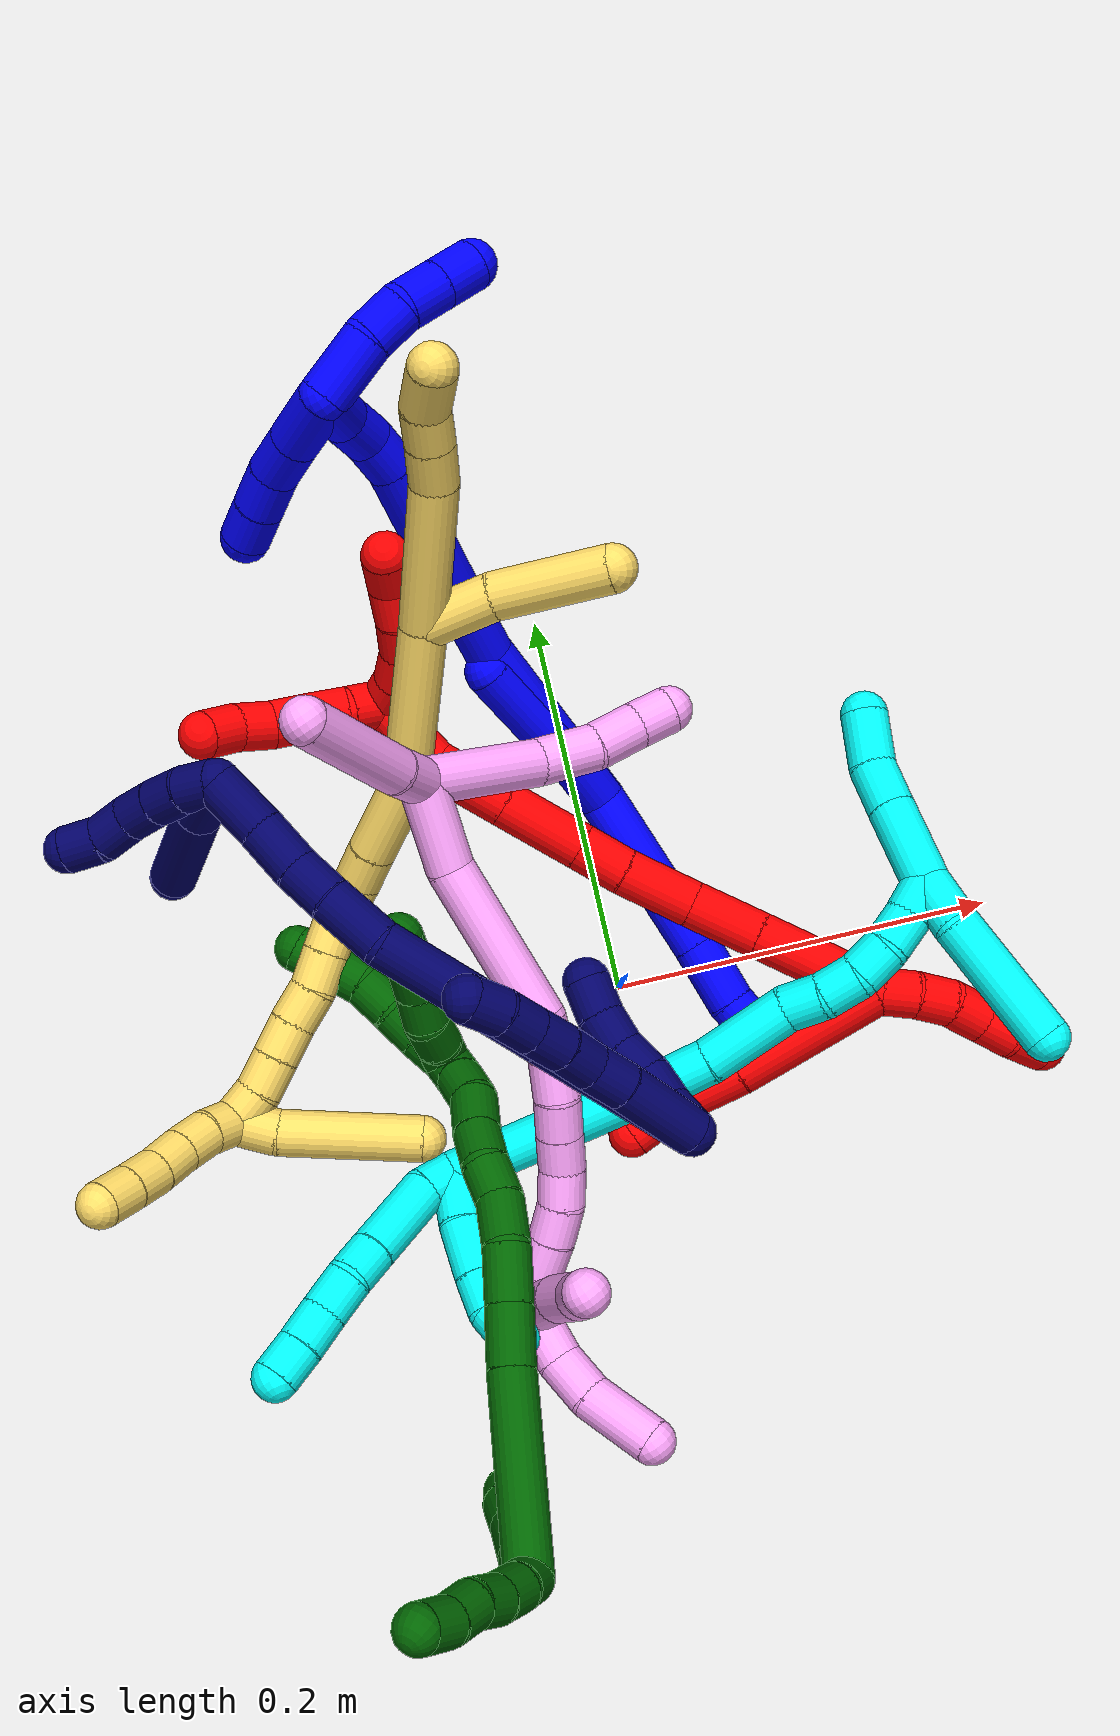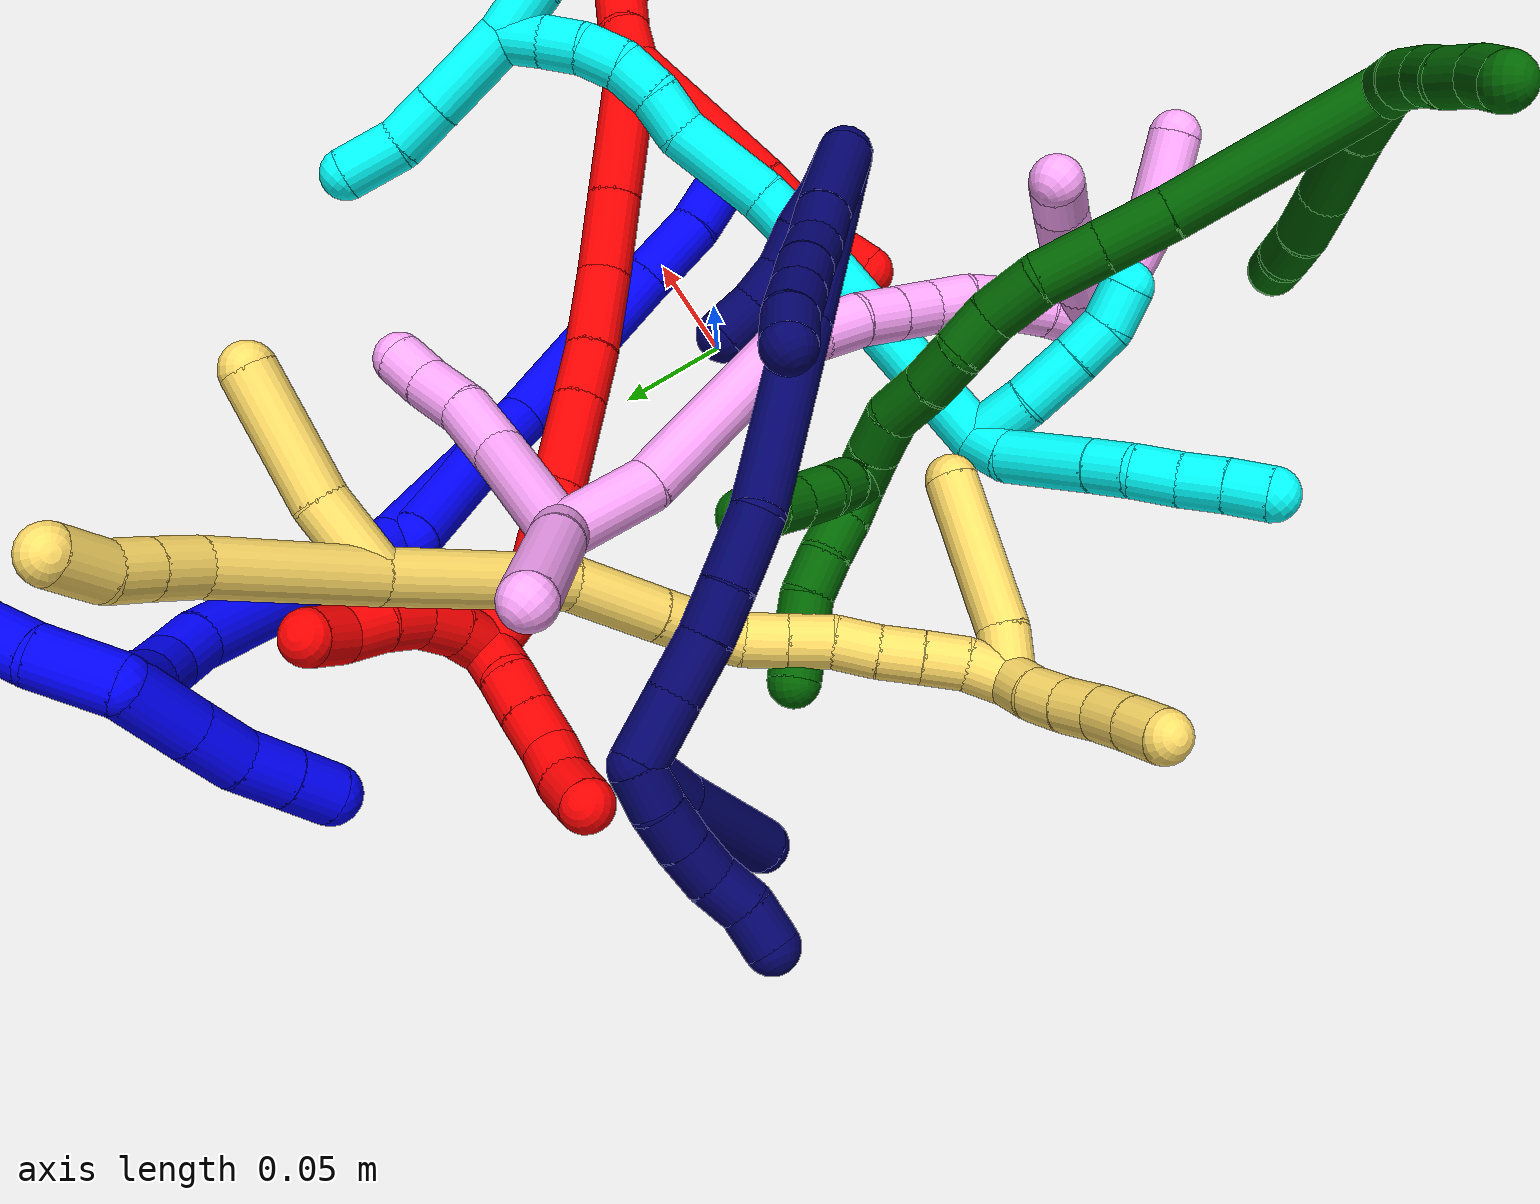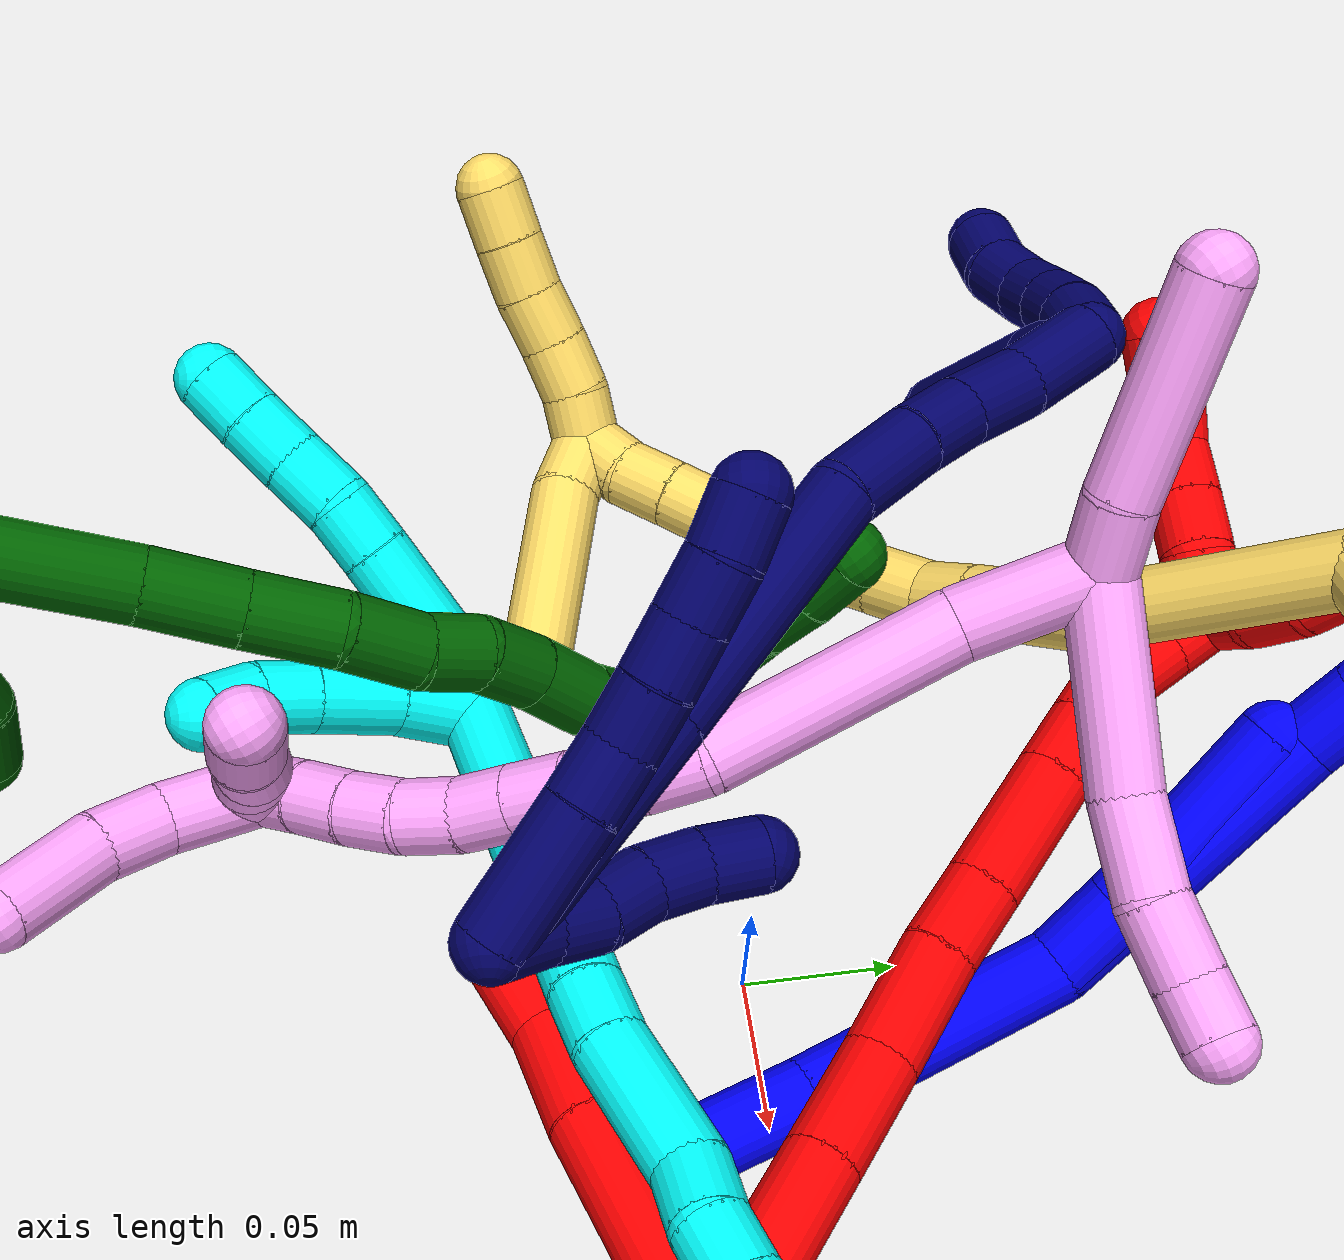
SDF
<sdf version="1.7">
 <world name="default">
  <plugin name="TubeGeneratorPlugin" filename="libtube_generator_plugin.so"/>
  <model name="photoneo_s_sensor">
   <static>1</static>
   <pose>0 0 2 1.57079 1.57079 3.14159</pose>
   <link name="link">
    <inertial><mass>0.1</mass></inertial>
    <sensor name="sensor" type="depth">
     <update_rate>30</update_rate>
     <camera>
      <horizontal_fov>1.22</horizontal_fov>
      <image><width>1920</width><height>1200</height><format>B8G8R8</format></image>
      <clip><near>0.1</near><far>4</far></clip>
      <depth_camera><output>points</output></depth_camera>
     </camera>
     <plugin name="camera_plugin" filename="libgazebo_ros_depth_camera.so">
      <baseline>0.2</baseline>
      <alwaysOn>1</alwaysOn>
      <updateRate>0.0</updateRate>
      <cameraName>camera_ir</cameraName>
      <imageTopicName>/camera/color/image_raw</imageTopicName>
      <cameraInfoTopicName>/camera/color/camera_info</cameraInfoTopicName>
      <depthImageTopicName>/camera/depth/image_raw</depthImageTopicName>
      <depthImageCameraInfoTopicName>/camera/depth/camera_info</depthImageCameraInfoTopicName>
      <pointCloudTopicName>/camera/depth/points</pointCloudTopicName>
      <frameName>fr_optical</frameName>
      <pointCloudCutoff>0.1</pointCloudCutoff>
      <pointCloudCutoffMax>2.0</pointCloudCutoffMax>
      <distortionK1>0</distortionK1>
      <distortionK2>0</distortionK2>
      <distortionK3>0</distortionK3>
      <distortionT1>0</distortionT1>
      <distortionT2>0</distortionT2>
      <CxPrime>0</CxPrime>
      <Cx>0</Cx>
      <Cy>0</Cy>
      <focalLength>0</focalLength>
      <hackBaseline>0</hackBaseline>
     </plugin>
    </sensor>
   </link>
  </model>
  <gravity>0 0 -9.8</gravity>
  <magnetic_field>6e-06 2.3e-05 -4.2e-05</magnetic_field>
  <atmosphere type="adiabatic"/>
  <physics name="default_physics" default="0" type="ode">
   <max_step_size>0.003</max_step_size>
   <real_time_factor>1</real_time_factor>
   <real_time_update_rate>1000</real_time_update_rate>
   <max_contacts>10000</max_contacts>
   <ode>
    <solver>
     <type>quick</type>
     <iters>100</iters>
     <sor>1.3</sor>
     <use_dynamic_moi_rescaling>0</use_dynamic_moi_rescaling>
    </solver>
    <constraints>
     <contact_max_correcting_vel>0</contact_max_correcting_vel>
     <contact_surface_layer>0.001</contact_surface_layer>
     <cfm>0</cfm>
     <erp>0.2</erp>
    </constraints>
   </ode>
  </physics>
  <scene><ambient>0.4 0.4 0.4 1</ambient><background>0.7 0.7 0.7 1</background><shadows>0</shadows></scene>
  <audio><device>default</device></audio>
  <spherical_coordinates>
   <surface_model>EARTH_WGS84</surface_model>
   <latitude_deg>0</latitude_deg>
   <longitude_deg>0</longitude_deg>
   <elevation>0</elevation>
   <heading_deg>0</heading_deg>
  </spherical_coordinates>
  <model name="bin">
   <static>1</static>
   <link name="bottom">
    <collision name="collision-bottom">
     <pose>0 0 -0.01 0 -0 0</pose>
     <geometry><box><size>0.8 0.6 0.02</size></box></geometry>
     <surface>
      <friction><ode><mu>100</mu><mu2>100</mu2></ode></friction>
      <contact><collide_bitmask>65535</collide_bitmask></contact>
     </surface>
    </collision>
   </link>
   <link name="west_wall">
    <collision name="collision-west_wall">
     <pose>-0.41 0 0.1 0 -0 0</pose>
     <geometry><box><size>0.02 0.6 0.2</size></box></geometry>
     <surface>
      <friction><ode><mu>100</mu><mu2>100</mu2></ode></friction>
      <contact><collide_bitmask>65535</collide_bitmask></contact>
     </surface>
    </collision>
   </link>
   <link name="east_wall">
    <collision name="collision-east_wall">
     <pose>0.41 0 0.1 0 -0 0</pose>
     <geometry><box><size>0.02 0.6 0.2</size></box></geometry>
     <surface>
      <friction><ode><mu>100</mu><mu2>100</mu2></ode></friction>
      <contact><collide_bitmask>65535</collide_bitmask></contact>
     </surface>
    </collision>
   </link>
   <link name="south_wall">
    <collision name="collision-south_wall">
     <pose>0 -0.31 0.1 0 -0 0</pose>
     <geometry><box><size>0.8 0.02 0.2</size></box></geometry>
     <surface>
      <friction><ode><mu>100</mu><mu2>100</mu2></ode></friction>
      <contact><collide_bitmask>65535</collide_bitmask></contact>
     </surface>
    </collision>
   </link>
   <link name="north_wall">
    <collision name="collision-north_wall">
     <pose>0 0.31 0.1 0 -0 0</pose>
     <geometry><box><size>0.8 0.02 0.2</size></box></geometry>
     <surface>
      <friction><ode><mu>100</mu><mu2>100</mu2></ode></friction>
      <contact><collide_bitmask>65535</collide_bitmask></contact>
     </surface>
    </collision>
   </link>
  </model>
  <model name="1">
   <static>0</static>
   <link name="1">
    <collision name="collision-cylinder-e_1_2_8">
     <pose>0.004625 -0.022606 -0.040108 2.62836 0.100126 0.377348</pose>
     <geometry><cylinder><radius>0.0125</radius><length>0.092543</length></cylinder></geometry>
     <surface>
      <friction><ode><mu>1.16</mu><mu2>1.16</mu2><slip1>0</slip1><slip2>0</slip2></ode></friction>
      <contact><ode><kp>1e+06</kp><kd>1</kd><max_vel>0</max_vel><min_depth>0.001</min_depth></ode></contact>
     </surface>
    </collision>
    <visual name="visual-cylinder-e_1_2_8">
     <pose>0.004625 -0.022606 -0.040108 2.62836 0.100126 0.377348</pose>
     <geometry><cylinder><radius>0.0125</radius><length>0.092543</length></cylinder></geometry>
     <material><ambient>0 0 1 1</ambient></material>
    </visual>
    <collision name="collision-cylinder-e_2_8_9">
     <pose>0.010567 -0.054177 -0.095316 2.60575 0.074831 0.271044</pose>
     <geometry><cylinder><radius>0.0125</radius><length>0.03522</length></cylinder></geometry>
     <surface>
      <friction><ode><mu>1.16</mu><mu2>1.16</mu2><slip1>0</slip1><slip2>0</slip2></ode></friction>
      <contact><ode><kp>1e+06</kp><kd>1</kd><max_vel>0</max_vel><min_depth>0.001</min_depth></ode></contact>
     </surface>
    </collision>
    <visual name="visual-cylinder-e_2_8_9">
     <pose>0.010567 -0.054177 -0.095316 2.60575 0.074831 0.271044</pose>
     <geometry><cylinder><radius>0.0125</radius><length>0.03522</length></cylinder></geometry>
     <material><ambient>0 0 1 1</ambient></material>
    </visual>
    <collision name="collision-cylinder-e_3_9_6">
     <pose>0.014564 -0.068342 -0.119871 2.63886 0.243463 0.889172</pose>
     <geometry><cylinder><radius>0.0125</radius><length>0.022236</length></cylinder></geometry>
     <surface>
      <friction><ode><mu>1.16</mu><mu2>1.16</mu2><slip1>0</slip1><slip2>0</slip2></ode></friction>
      <contact><ode><kp>1e+06</kp><kd>1</kd><max_vel>0</max_vel><min_depth>0.001</min_depth></ode></contact>
     </surface>
    </collision>
    <visual name="visual-cylinder-e_3_9_6">
     <pose>0.014564 -0.068342 -0.119871 2.63886 0.243463 0.889172</pose>
     <geometry><cylinder><radius>0.0125</radius><length>0.022236</length></cylinder></geometry>
     <material><ambient>0 0 1 1</ambient></material>
    </visual>
    <collision name="collision-cylinder-e_1_2_10">
     <pose>-0.000681 -0.000761 0.014425 0.052741 -0.047136 -0.001244</pose>
     <geometry><cylinder><radius>0.0125</radius><length>0.028921</length></cylinder></geometry>
     <surface>
      <friction><ode><mu>1.16</mu><mu2>1.16</mu2><slip1>0</slip1><slip2>0</slip2></ode></friction>
      <contact><ode><kp>1e+06</kp><kd>1</kd><max_vel>0</max_vel><min_depth>0.001</min_depth></ode></contact>
     </surface>
    </collision>
    <visual name="visual-cylinder-e_1_2_10">
     <pose>-0.000681 -0.000761 0.014425 0.052741 -0.047136 -0.001244</pose>
     <geometry><cylinder><radius>0.0125</radius><length>0.028921</length></cylinder></geometry>
     <material><ambient>0 0 1 1</ambient></material>
    </visual>
    <collision name="collision-cylinder-e_2_10_5">
     <pose>-0.0057 -0.00378 0.064051 0.064035 -0.122346 -0.003923</pose>
     <geometry><cylinder><radius>0.0125</radius><length>0.071079</length></cylinder></geometry>
     <surface>
      <friction><ode><mu>1.16</mu><mu2>1.16</mu2><slip1>0</slip1><slip2>0</slip2></ode></friction>
      <contact><ode><kp>1e+06</kp><kd>1</kd><max_vel>0</max_vel><min_depth>0.001</min_depth></ode></contact>
     </surface>
    </collision>
    <visual name="visual-cylinder-e_2_10_5">
     <pose>-0.0057 -0.00378 0.064051 0.064035 -0.122346 -0.003923</pose>
     <geometry><cylinder><radius>0.0125</radius><length>0.071079</length></cylinder></geometry>
     <material><ambient>0 0 1 1</ambient></material>
    </visual>
    <collision name="collision-cylinder-e_1_2_11">
     <pose>-0.002799 -0.000149 0.053019 0.002817 -0.052749 -7.4e-05</pose>
     <geometry><cylinder><radius>0.0125</radius><length>0.106186</length></cylinder></geometry>
     <surface>
      <friction><ode><mu>1.16</mu><mu2>1.16</mu2><slip1>0</slip1><slip2>0</slip2></ode></friction>
      <contact><ode><kp>1e+06</kp><kd>1</kd><max_vel>0</max_vel><min_depth>0.001</min_depth></ode></contact>
     </surface>
    </collision>
    <visual name="visual-cylinder-e_1_2_11">
     <pose>-0.002799 -0.000149 0.053019 0.002817 -0.052749 -7.4e-05</pose>
     <geometry><cylinder><radius>0.0125</radius><length>0.106186</length></cylinder></geometry>
     <material><ambient>0 0 1 1</ambient></material>
    </visual>
    <collision name="collision-cylinder-e_2_11_12">
     <pose>-0.004256 -0.001851 0.117496 0.134676 0.115601 0.007805</pose>
     <geometry><cylinder><radius>0.0125</radius><length>0.02328</length></cylinder></geometry>
     <surface>
      <friction><ode><mu>1.16</mu><mu2>1.16</mu2><slip1>0</slip1><slip2>0</slip2></ode></friction>
      <contact><ode><kp>1e+06</kp><kd>1</kd><max_vel>0</max_vel><min_depth>0.001</min_depth></ode></contact>
     </surface>
    </collision>
    <visual name="visual-cylinder-e_2_11_12">
     <pose>-0.004256 -0.001851 0.117496 0.134676 0.115601 0.007805</pose>
     <geometry><cylinder><radius>0.0125</radius><length>0.02328</length></cylinder></geometry>
     <material><ambient>0 0 1 1</ambient></material>
    </visual>
    <collision name="collision-cylinder-e_3_12_13">
     <pose>0.00464 -0.013002 0.177922 0.193551 0.150223 0.014611</pose>
     <geometry><cylinder><radius>0.0125</radius><length>0.100939</length></cylinder></geometry>
     <surface>
      <friction><ode><mu>1.16</mu><mu2>1.16</mu2><slip1>0</slip1><slip2>0</slip2></ode></friction>
      <contact><ode><kp>1e+06</kp><kd>1</kd><max_vel>0</max_vel><min_depth>0.001</min_depth></ode></contact>
     </surface>
    </collision>
    <visual name="visual-cylinder-e_3_12_13">
     <pose>0.00464 -0.013002 0.177922 0.193551 0.150223 0.014611</pose>
     <geometry><cylinder><radius>0.0125</radius><length>0.100939</length></cylinder></geometry>
     <material><ambient>0 0 1 1</ambient></material>
    </visual>
    <collision name="collision-cylinder-e_4_13_14">
     <pose>0.011891 -0.025098 0.237001 0.242231 -0.028981 -0.003528</pose>
     <geometry><cylinder><radius>0.0125</radius><length>0.020835</length></cylinder></geometry>
     <surface>
      <friction><ode><mu>1.16</mu><mu2>1.16</mu2><slip1>0</slip1><slip2>0</slip2></ode></friction>
      <contact><ode><kp>1e+06</kp><kd>1</kd><max_vel>0</max_vel><min_depth>0.001</min_depth></ode></contact>
     </surface>
    </collision>
    <visual name="visual-cylinder-e_4_13_14">
     <pose>0.011891 -0.025098 0.237001 0.242231 -0.028981 -0.003528</pose>
     <geometry><cylinder><radius>0.0125</radius><length>0.020835</length></cylinder></geometry>
     <material><ambient>0 0 1 1</ambient></material>
    </visual>
    <collision name="collision-cylinder-e_5_14_15">
     <pose>0.010929 -0.03372 0.256747 0.56617 -0.057754 -0.016805</pose>
     <geometry><cylinder><radius>0.0125</radius><length>0.022875</length></cylinder></geometry>
     <surface>
      <friction><ode><mu>1.16</mu><mu2>1.16</mu2><slip1>0</slip1><slip2>0</slip2></ode></friction>
      <contact><ode><kp>1e+06</kp><kd>1</kd><max_vel>0</max_vel><min_depth>0.001</min_depth></ode></contact>
     </surface>
    </collision>
    <visual name="visual-cylinder-e_5_14_15">
     <pose>0.010929 -0.03372 0.256747 0.56617 -0.057754 -0.016805</pose>
     <geometry><cylinder><radius>0.0125</radius><length>0.022875</length></cylinder></geometry>
     <material><ambient>0 0 1 1</ambient></material>
    </visual>
    <collision name="collision-cylinder-e_6_15_1">
     <pose>0.011356 -0.048717 0.275744 0.758635 0.08408 0.033533</pose>
     <geometry><cylinder><radius>0.0125</radius><length>0.025885</length></cylinder></geometry>
     <surface>
      <friction><ode><mu>1.16</mu><mu2>1.16</mu2><slip1>0</slip1><slip2>0</slip2></ode></friction>
      <contact><ode><kp>1e+06</kp><kd>1</kd><max_vel>0</max_vel><min_depth>0.001</min_depth></ode></contact>
     </surface>
    </collision>
    <visual name="visual-cylinder-e_6_15_1">
     <pose>0.011356 -0.048717 0.275744 0.758635 0.08408 0.033533</pose>
     <geometry><cylinder><radius>0.0125</radius><length>0.025885</length></cylinder></geometry>
     <material><ambient>0 0 1 1</ambient></material>
    </visual>
    <collision name="collision-cylinder-e_1_1_16">
     <pose>-0.000665 -0.051368 0.277703 -2.44259 -0.93529 1.89131</pose>
     <geometry><cylinder><radius>0.0125</radius><length>0.032576</length></cylinder></geometry>
     <surface>
      <friction><ode><mu>1.16</mu><mu2>1.16</mu2><slip1>0</slip1><slip2>0</slip2></ode></friction>
      <contact><ode><kp>1e+06</kp><kd>1</kd><max_vel>0</max_vel><min_depth>0.001</min_depth></ode></contact>
     </surface>
    </collision>
    <visual name="visual-cylinder-e_1_1_16">
     <pose>-0.000665 -0.051368 0.277703 -2.44259 -0.93529 1.89131</pose>
     <geometry><cylinder><radius>0.0125</radius><length>0.032576</length></cylinder></geometry>
     <material><ambient>0 0 1 1</ambient></material>
    </visual>
    <collision name="collision-cylinder-e_2_16_17">
     <pose>-0.023533 -0.040839 0.264746 -2.482 -0.946485 1.96307</pose>
     <geometry><cylinder><radius>0.0125</radius><length>0.024056</length></cylinder></geometry>
     <surface>
      <friction><ode><mu>1.16</mu><mu2>1.16</mu2><slip1>0</slip1><slip2>0</slip2></ode></friction>
      <contact><ode><kp>1e+06</kp><kd>1</kd><max_vel>0</max_vel><min_depth>0.001</min_depth></ode></contact>
     </surface>
    </collision>
    <visual name="visual-cylinder-e_2_16_17">
     <pose>-0.023533 -0.040839 0.264746 -2.482 -0.946485 1.96307</pose>
     <geometry><cylinder><radius>0.0125</radius><length>0.024056</length></cylinder></geometry>
     <material><ambient>0 0 1 1</ambient></material>
    </visual>
    <collision name="collision-cylinder-e_3_17_18">
     <pose>-0.042249 -0.034114 0.252677 -2.78633 -0.911145 2.43914</pose>
     <geometry><cylinder><radius>0.0125</radius><length>0.02267</length></cylinder></geometry>
     <surface>
      <friction><ode><mu>1.16</mu><mu2>1.16</mu2><slip1>0</slip1><slip2>0</slip2></ode></friction>
      <contact><ode><kp>1e+06</kp><kd>1</kd><max_vel>0</max_vel><min_depth>0.001</min_depth></ode></contact>
     </surface>
    </collision>
    <visual name="visual-cylinder-e_3_17_18">
     <pose>-0.042249 -0.034114 0.252677 -2.78633 -0.911145 2.43914</pose>
     <geometry><cylinder><radius>0.0125</radius><length>0.02267</length></cylinder></geometry>
     <material><ambient>0 0 1 1</ambient></material>
    </visual>
    <collision name="collision-cylinder-e_4_18_4">
     <pose>-0.059274 -0.029273 0.240153 -2.75813 -0.894012 2.37207</pose>
     <geometry><cylinder><radius>0.0125</radius><length>0.020698</length></cylinder></geometry>
     <surface>
      <friction><ode><mu>1.16</mu><mu2>1.16</mu2><slip1>0</slip1><slip2>0</slip2></ode></friction>
      <contact><ode><kp>1e+06</kp><kd>1</kd><max_vel>0</max_vel><min_depth>0.001</min_depth></ode></contact>
     </surface>
    </collision>
    <visual name="visual-cylinder-e_4_18_4">
     <pose>-0.059274 -0.029273 0.240153 -2.75813 -0.894012 2.37207</pose>
     <geometry><cylinder><radius>0.0125</radius><length>0.020698</length></cylinder></geometry>
     <material><ambient>0 0 1 1</ambient></material>
    </visual>
    <collision name="collision-cylinder-e_1_1_19">
     <pose>0.027537 -0.051234 0.289935 -0.920809 1.08428 -0.580586</pose>
     <geometry><cylinder><radius>0.0125</radius><length>0.034152</length></cylinder></geometry>
     <surface>
      <friction><ode><mu>1.16</mu><mu2>1.16</mu2><slip1>0</slip1><slip2>0</slip2></ode></friction>
      <contact><ode><kp>1e+06</kp><kd>1</kd><max_vel>0</max_vel><min_depth>0.001</min_depth></ode></contact>
     </surface>
    </collision>
    <visual name="visual-cylinder-e_1_1_19">
     <pose>0.027537 -0.051234 0.289935 -0.920809 1.08428 -0.580586</pose>
     <geometry><cylinder><radius>0.0125</radius><length>0.034152</length></cylinder></geometry>
     <material><ambient>0 0 1 1</ambient></material>
    </visual>
    <collision name="collision-cylinder-e_2_19_20">
     <pose>0.052166 -0.039588 0.295554 -1.42312 1.05963 -0.935265</pose>
     <geometry><cylinder><radius>0.0125</radius><length>0.021863</length></cylinder></geometry>
     <surface>
      <friction><ode><mu>1.16</mu><mu2>1.16</mu2><slip1>0</slip1><slip2>0</slip2></ode></friction>
      <contact><ode><kp>1e+06</kp><kd>1</kd><max_vel>0</max_vel><min_depth>0.001</min_depth></ode></contact>
     </surface>
    </collision>
    <visual name="visual-cylinder-e_2_19_20">
     <pose>0.052166 -0.039588 0.295554 -1.42312 1.05963 -0.935265</pose>
     <geometry><cylinder><radius>0.0125</radius><length>0.021863</length></cylinder></geometry>
     <material><ambient>0 0 1 1</ambient></material>
    </visual>
    <collision name="collision-cylinder-e_3_20_21">
     <pose>0.070327 -0.027195 0.294249 -1.85717 0.861429 -1.10173</pose>
     <geometry><cylinder><radius>0.0125</radius><length>0.02274</length></cylinder></geometry>
     <surface>
      <friction><ode><mu>1.16</mu><mu2>1.16</mu2><slip1>0</slip1><slip2>0</slip2></ode></friction>
      <contact><ode><kp>1e+06</kp><kd>1</kd><max_vel>0</max_vel><min_depth>0.001</min_depth></ode></contact>
     </surface>
    </collision>
    <visual name="visual-cylinder-e_3_20_21">
     <pose>0.070327 -0.027195 0.294249 -1.85717 0.861429 -1.10173</pose>
     <geometry><cylinder><radius>0.0125</radius><length>0.02274</length></cylinder></geometry>
     <material><ambient>0 0 1 1</ambient></material>
    </visual>
    <collision name="collision-cylinder-e_4_21_3">
     <pose>0.08706 -0.013515 0.290183 -1.86235 0.86808 -1.11439</pose>
     <geometry><cylinder><radius>0.0125</radius><length>0.021245</length></cylinder></geometry>
     <surface>
      <friction><ode><mu>1.16</mu><mu2>1.16</mu2><slip1>0</slip1><slip2>0</slip2></ode></friction>
      <contact><ode><kp>1e+06</kp><kd>1</kd><max_vel>0</max_vel><min_depth>0.001</min_depth></ode></contact>
     </surface>
    </collision>
    <visual name="visual-cylinder-e_4_21_3">
     <pose>0.08706 -0.013515 0.290183 -1.86235 0.86808 -1.11439</pose>
     <geometry><cylinder><radius>0.0125</radius><length>0.021245</length></cylinder></geometry>
     <material><ambient>0 0 1 1</ambient></material>
    </visual>
    <collision name="collision-sphere-3">
     <pose>0.095166 -0.006939 0.28821 0 -0 0</pose>
     <geometry><sphere><radius>0.0125</radius></sphere></geometry>
     <surface>
      <friction><ode><mu>1.16</mu><mu2>1.16</mu2><slip1>0</slip1><slip2>0</slip2></ode></friction>
      <contact><ode><kp>1e+06</kp><kd>1</kd><max_vel>0</max_vel><min_depth>0.001</min_depth></ode></contact>
     </surface>
    </collision>
    <visual name="visual-sphere-3">
     <pose>0.095166 -0.006939 0.28821 0 -0 0</pose>
     <geometry><sphere><radius>0.0125</radius></sphere></geometry>
     <material><ambient>0 0 1 1</ambient></material>
    </visual>
    <collision name="collision-sphere-21">
     <pose>0.078954 -0.02009 0.292157 0 -0 0</pose>
     <geometry><sphere><radius>0.0125</radius></sphere></geometry>
     <surface>
      <friction><ode><mu>1.16</mu><mu2>1.16</mu2><slip1>0</slip1><slip2>0</slip2></ode></friction>
      <contact><ode><kp>1e+06</kp><kd>1</kd><max_vel>0</max_vel><min_depth>0.001</min_depth></ode></contact>
     </surface>
    </collision>
    <visual name="visual-sphere-21">
     <pose>0.078954 -0.02009 0.292157 0 -0 0</pose>
     <geometry><sphere><radius>0.0125</radius></sphere></geometry>
     <material><ambient>0 0 1 1</ambient></material>
    </visual>
    <collision name="collision-sphere-20">
     <pose>0.0617 -0.034299 0.296341 0 -0 0</pose>
     <geometry><sphere><radius>0.0125</radius></sphere></geometry>
     <surface>
      <friction><ode><mu>1.16</mu><mu2>1.16</mu2><slip1>0</slip1><slip2>0</slip2></ode></friction>
      <contact><ode><kp>1e+06</kp><kd>1</kd><max_vel>0</max_vel><min_depth>0.001</min_depth></ode></contact>
     </surface>
    </collision>
    <visual name="visual-sphere-20">
     <pose>0.0617 -0.034299 0.296341 0 -0 0</pose>
     <geometry><sphere><radius>0.0125</radius></sphere></geometry>
     <material><ambient>0 0 1 1</ambient></material>
    </visual>
    <collision name="collision-sphere-19">
     <pose>0.042632 -0.044878 0.294767 0 -0 0</pose>
     <geometry><sphere><radius>0.0125</radius></sphere></geometry>
     <surface>
      <friction><ode><mu>1.16</mu><mu2>1.16</mu2><slip1>0</slip1><slip2>0</slip2></ode></friction>
      <contact><ode><kp>1e+06</kp><kd>1</kd><max_vel>0</max_vel><min_depth>0.001</min_depth></ode></contact>
     </surface>
    </collision>
    <visual name="visual-sphere-19">
     <pose>0.042632 -0.044878 0.294767 0 -0 0</pose>
     <geometry><sphere><radius>0.0125</radius></sphere></geometry>
     <material><ambient>0 0 1 1</ambient></material>
    </visual>
    <collision name="collision-sphere-5">
     <pose>-0.010037 -0.006037 0.099252 0 -0 0</pose>
     <geometry><sphere><radius>0.0125</radius></sphere></geometry>
     <surface>
      <friction><ode><mu>1.16</mu><mu2>1.16</mu2><slip1>0</slip1><slip2>0</slip2></ode></friction>
      <contact><ode><kp>1e+06</kp><kd>1</kd><max_vel>0</max_vel><min_depth>0.001</min_depth></ode></contact>
     </surface>
    </collision>
    <visual name="visual-sphere-5">
     <pose>-0.010037 -0.006037 0.099252 0 -0 0</pose>
     <geometry><sphere><radius>0.0125</radius></sphere></geometry>
     <material><ambient>0 0 1 1</ambient></material>
    </visual>
    <collision name="collision-sphere-10">
     <pose>-0.001363 -0.001523 0.028849 0 -0 0</pose>
     <geometry><sphere><radius>0.0125</radius></sphere></geometry>
     <surface>
      <friction><ode><mu>1.16</mu><mu2>1.16</mu2><slip1>0</slip1><slip2>0</slip2></ode></friction>
      <contact><ode><kp>1e+06</kp><kd>1</kd><max_vel>0</max_vel><min_depth>0.001</min_depth></ode></contact>
     </surface>
    </collision>
    <visual name="visual-sphere-10">
     <pose>-0.001363 -0.001523 0.028849 0 -0 0</pose>
     <geometry><sphere><radius>0.0125</radius></sphere></geometry>
     <material><ambient>0 0 1 1</ambient></material>
    </visual>
    <collision name="collision-sphere-6">
     <pose>0.017244 -0.073541 -0.129326 0 -0 0</pose>
     <geometry><sphere><radius>0.0125</radius></sphere></geometry>
     <surface>
      <friction><ode><mu>1.16</mu><mu2>1.16</mu2><slip1>0</slip1><slip2>0</slip2></ode></friction>
      <contact><ode><kp>1e+06</kp><kd>1</kd><max_vel>0</max_vel><min_depth>0.001</min_depth></ode></contact>
     </surface>
    </collision>
    <visual name="visual-sphere-6">
     <pose>0.017244 -0.073541 -0.129326 0 -0 0</pose>
     <geometry><sphere><radius>0.0125</radius></sphere></geometry>
     <material><ambient>0 0 1 1</ambient></material>
    </visual>
    <collision name="collision-sphere-9">
     <pose>0.011884 -0.063143 -0.110416 0 -0 0</pose>
     <geometry><sphere><radius>0.0125</radius></sphere></geometry>
     <surface>
      <friction><ode><mu>1.16</mu><mu2>1.16</mu2><slip1>0</slip1><slip2>0</slip2></ode></friction>
      <contact><ode><kp>1e+06</kp><kd>1</kd><max_vel>0</max_vel><min_depth>0.001</min_depth></ode></contact>
     </surface>
    </collision>
    <visual name="visual-sphere-9">
     <pose>0.011884 -0.063143 -0.110416 0 -0 0</pose>
     <geometry><sphere><radius>0.0125</radius></sphere></geometry>
     <material><ambient>0 0 1 1</ambient></material>
    </visual>
    <collision name="collision-sphere-2">
     <geometry><sphere><radius>0.0125</radius></sphere></geometry>
     <surface>
      <friction><ode><mu>1.16</mu><mu2>1.16</mu2><slip1>0</slip1><slip2>0</slip2></ode></friction>
      <contact><ode><kp>1e+06</kp><kd>1</kd><max_vel>0</max_vel><min_depth>0.001</min_depth></ode></contact>
     </surface>
    </collision>
    <visual name="visual-sphere-2">
     <geometry><sphere><radius>0.0125</radius></sphere></geometry>
     <material><ambient>0 0 1 1</ambient></material>
    </visual>
    <collision name="collision-sphere-8">
     <pose>0.00925 -0.045211 -0.080216 0 -0 0</pose>
     <geometry><sphere><radius>0.0125</radius></sphere></geometry>
     <surface>
      <friction><ode><mu>1.16</mu><mu2>1.16</mu2><slip1>0</slip1><slip2>0</slip2></ode></friction>
      <contact><ode><kp>1e+06</kp><kd>1</kd><max_vel>0</max_vel><min_depth>0.001</min_depth></ode></contact>
     </surface>
    </collision>
    <visual name="visual-sphere-8">
     <pose>0.00925 -0.045211 -0.080216 0 -0 0</pose>
     <geometry><sphere><radius>0.0125</radius></sphere></geometry>
     <material><ambient>0 0 1 1</ambient></material>
    </visual>
    <collision name="collision-sphere-11">
     <pose>-0.005599 -0.000299 0.106038 0 -0 0</pose>
     <geometry><sphere><radius>0.0125</radius></sphere></geometry>
     <surface>
      <friction><ode><mu>1.16</mu><mu2>1.16</mu2><slip1>0</slip1><slip2>0</slip2></ode></friction>
      <contact><ode><kp>1e+06</kp><kd>1</kd><max_vel>0</max_vel><min_depth>0.001</min_depth></ode></contact>
     </surface>
    </collision>
    <visual name="visual-sphere-11">
     <pose>-0.005599 -0.000299 0.106038 0 -0 0</pose>
     <geometry><sphere><radius>0.0125</radius></sphere></geometry>
     <material><ambient>0 0 1 1</ambient></material>
    </visual>
    <collision name="collision-sphere-12">
     <pose>-0.002913 -0.003404 0.128953 0 -0 0</pose>
     <geometry><sphere><radius>0.0125</radius></sphere></geometry>
     <surface>
      <friction><ode><mu>1.16</mu><mu2>1.16</mu2><slip1>0</slip1><slip2>0</slip2></ode></friction>
      <contact><ode><kp>1e+06</kp><kd>1</kd><max_vel>0</max_vel><min_depth>0.001</min_depth></ode></contact>
     </surface>
    </collision>
    <visual name="visual-sphere-12">
     <pose>-0.002913 -0.003404 0.128953 0 -0 0</pose>
     <geometry><sphere><radius>0.0125</radius></sphere></geometry>
     <material><ambient>0 0 1 1</ambient></material>
    </visual>
    <collision name="collision-sphere-13">
     <pose>0.012193 -0.0226 0.226892 0 -0 0</pose>
     <geometry><sphere><radius>0.0125</radius></sphere></geometry>
     <surface>
      <friction><ode><mu>1.16</mu><mu2>1.16</mu2><slip1>0</slip1><slip2>0</slip2></ode></friction>
      <contact><ode><kp>1e+06</kp><kd>1</kd><max_vel>0</max_vel><min_depth>0.001</min_depth></ode></contact>
     </surface>
    </collision>
    <visual name="visual-sphere-13">
     <pose>0.012193 -0.0226 0.226892 0 -0 0</pose>
     <geometry><sphere><radius>0.0125</radius></sphere></geometry>
     <material><ambient>0 0 1 1</ambient></material>
    </visual>
    <collision name="collision-sphere-14">
     <pose>0.011589 -0.027596 0.24711 0 -0 0</pose>
     <geometry><sphere><radius>0.0125</radius></sphere></geometry>
     <surface>
      <friction><ode><mu>1.16</mu><mu2>1.16</mu2><slip1>0</slip1><slip2>0</slip2></ode></friction>
      <contact><ode><kp>1e+06</kp><kd>1</kd><max_vel>0</max_vel><min_depth>0.001</min_depth></ode></contact>
     </surface>
    </collision>
    <visual name="visual-sphere-14">
     <pose>0.011589 -0.027596 0.24711 0 -0 0</pose>
     <geometry><sphere><radius>0.0125</radius></sphere></geometry>
     <material><ambient>0 0 1 1</ambient></material>
    </visual>
    <collision name="collision-sphere-15">
     <pose>0.010269 -0.039845 0.266384 0 -0 0</pose>
     <geometry><sphere><radius>0.0125</radius></sphere></geometry>
     <surface>
      <friction><ode><mu>1.16</mu><mu2>1.16</mu2><slip1>0</slip1><slip2>0</slip2></ode></friction>
      <contact><ode><kp>1e+06</kp><kd>1</kd><max_vel>0</max_vel><min_depth>0.001</min_depth></ode></contact>
     </surface>
    </collision>
    <visual name="visual-sphere-15">
     <pose>0.010269 -0.039845 0.266384 0 -0 0</pose>
     <geometry><sphere><radius>0.0125</radius></sphere></geometry>
     <material><ambient>0 0 1 1</ambient></material>
    </visual>
    <collision name="collision-sphere-1">
     <pose>0.012443 -0.057589 0.285104 0 -0 0</pose>
     <geometry><sphere><radius>0.0125</radius></sphere></geometry>
     <surface>
      <friction><ode><mu>1.16</mu><mu2>1.16</mu2><slip1>0</slip1><slip2>0</slip2></ode></friction>
      <contact><ode><kp>1e+06</kp><kd>1</kd><max_vel>0</max_vel><min_depth>0.001</min_depth></ode></contact>
     </surface>
    </collision>
    <visual name="visual-sphere-1">
     <pose>0.012443 -0.057589 0.285104 0 -0 0</pose>
     <geometry><sphere><radius>0.0125</radius></sphere></geometry>
     <material><ambient>0 0 1 1</ambient></material>
    </visual>
    <collision name="collision-sphere-18">
     <pose>-0.051206 -0.031698 0.246164 0 -0 0</pose>
     <geometry><sphere><radius>0.0125</radius></sphere></geometry>
     <surface>
      <friction><ode><mu>1.16</mu><mu2>1.16</mu2><slip1>0</slip1><slip2>0</slip2></ode></friction>
      <contact><ode><kp>1e+06</kp><kd>1</kd><max_vel>0</max_vel><min_depth>0.001</min_depth></ode></contact>
     </surface>
    </collision>
    <visual name="visual-sphere-18">
     <pose>-0.051206 -0.031698 0.246164 0 -0 0</pose>
     <geometry><sphere><radius>0.0125</radius></sphere></geometry>
     <material><ambient>0 0 1 1</ambient></material>
    </visual>
    <collision name="collision-sphere-16">
     <pose>-0.013773 -0.045147 0.270302 0 -0 0</pose>
     <geometry><sphere><radius>0.0125</radius></sphere></geometry>
     <surface>
      <friction><ode><mu>1.16</mu><mu2>1.16</mu2><slip1>0</slip1><slip2>0</slip2></ode></friction>
      <contact><ode><kp>1e+06</kp><kd>1</kd><max_vel>0</max_vel><min_depth>0.001</min_depth></ode></contact>
     </surface>
    </collision>
    <visual name="visual-sphere-16">
     <pose>-0.013773 -0.045147 0.270302 0 -0 0</pose>
     <geometry><sphere><radius>0.0125</radius></sphere></geometry>
     <material><ambient>0 0 1 1</ambient></material>
    </visual>
    <collision name="collision-sphere-17">
     <pose>-0.033292 -0.03653 0.25919 0 -0 0</pose>
     <geometry><sphere><radius>0.0125</radius></sphere></geometry>
     <surface>
      <friction><ode><mu>1.16</mu><mu2>1.16</mu2><slip1>0</slip1><slip2>0</slip2></ode></friction>
      <contact><ode><kp>1e+06</kp><kd>1</kd><max_vel>0</max_vel><min_depth>0.001</min_depth></ode></contact>
     </surface>
    </collision>
    <visual name="visual-sphere-17">
     <pose>-0.033292 -0.03653 0.25919 0 -0 0</pose>
     <geometry><sphere><radius>0.0125</radius></sphere></geometry>
     <material><ambient>0 0 1 1</ambient></material>
    </visual>
    <collision name="collision-sphere-4">
     <pose>-0.067342 -0.026848 0.234143 0 -0 0</pose>
     <geometry><sphere><radius>0.0125</radius></sphere></geometry>
     <surface>
      <friction><ode><mu>1.16</mu><mu2>1.16</mu2><slip1>0</slip1><slip2>0</slip2></ode></friction>
      <contact><ode><kp>1e+06</kp><kd>1</kd><max_vel>0</max_vel><min_depth>0.001</min_depth></ode></contact>
     </surface>
    </collision>
    <visual name="visual-sphere-4">
     <pose>-0.067342 -0.026848 0.234143 0 -0 0</pose>
     <geometry><sphere><radius>0.0125</radius></sphere></geometry>
     <material><ambient>0 0 1 1</ambient></material>
    </visual>
    <inertial>
     <pose>0.00576 -0.023057 0.126457 0 -0 0</pose>
     <mass>0.75</mass>
     <inertia>
      <ixx>0.000339</ixx>
      <ixy>0</ixy>
      <ixz>0</ixz>
      <iyy>0.000216</iyy>
      <iyz>0</iyz>
      <izz>5.6e-05</izz>
     </inertia>
    </inertial>
   </link>
   <pose>0.013368 0.099004 0.01476 -0.995426 -0.277791 0.234021</pose>
  </model>
  <model name="2">
   <static>0</static>
   <link name="2">
    <collision name="collision-cylinder-e_1_2_8">
     <pose>-0.039684 0.00148 -0.012324 -3.02206 -1.26765 2.97913</pose>
     <geometry><cylinder><radius>0.0125</radius><length>0.083159</length></cylinder></geometry>
     <surface>
      <friction><ode><mu>1.16</mu><mu2>1.16</mu2><slip1>0</slip1><slip2>0</slip2></ode></friction>
      <contact><ode><kp>1e+06</kp><kd>1</kd><max_vel>0</max_vel><min_depth>0.001</min_depth></ode></contact>
     </surface>
    </collision>
    <visual name="visual-cylinder-e_1_2_8">
     <pose>-0.039684 0.00148 -0.012324 -3.02206 -1.26765 2.97913</pose>
     <geometry><cylinder><radius>0.0125</radius><length>0.083159</length></cylinder></geometry>
     <material><ambient>1 0 0 1</ambient></material>
    </visual>
    <collision name="collision-cylinder-e_2_8_9">
     <pose>-0.097128 0.005251 -0.03007 -2.74191 -1.25076 2.59463</pose>
     <geometry><cylinder><radius>0.0125</radius><length>0.037421</length></cylinder></geometry>
     <surface>
      <friction><ode><mu>1.16</mu><mu2>1.16</mu2><slip1>0</slip1><slip2>0</slip2></ode></friction>
      <contact><ode><kp>1e+06</kp><kd>1</kd><max_vel>0</max_vel><min_depth>0.001</min_depth></ode></contact>
     </surface>
    </collision>
    <visual name="visual-cylinder-e_2_8_9">
     <pose>-0.097128 0.005251 -0.03007 -2.74191 -1.25076 2.59463</pose>
     <geometry><cylinder><radius>0.0125</radius><length>0.037421</length></cylinder></geometry>
     <material><ambient>1 0 0 1</ambient></material>
    </visual>
    <collision name="collision-cylinder-e_3_9_6">
     <pose>-0.129378 0.006103 -0.037583 2.53883 -1.39744 -2.43281</pose>
     <geometry><cylinder><radius>0.0125</radius><length>0.02942</length></cylinder></geometry>
     <surface>
      <friction><ode><mu>1.16</mu><mu2>1.16</mu2><slip1>0</slip1><slip2>0</slip2></ode></friction>
      <contact><ode><kp>1e+06</kp><kd>1</kd><max_vel>0</max_vel><min_depth>0.001</min_depth></ode></contact>
     </surface>
    </collision>
    <visual name="visual-cylinder-e_3_9_6">
     <pose>-0.129378 0.006103 -0.037583 2.53883 -1.39744 -2.43281</pose>
     <geometry><cylinder><radius>0.0125</radius><length>0.02942</length></cylinder></geometry>
     <material><ambient>1 0 0 1</ambient></material>
    </visual>
    <collision name="collision-cylinder-e_1_2_10">
     <pose>0.008243 -0.00534 -0.001877 1.90886 0.969049 1.27803</pose>
     <geometry><cylinder><radius>0.0125</radius><length>0.02</length></cylinder></geometry>
     <surface>
      <friction><ode><mu>1.16</mu><mu2>1.16</mu2><slip1>0</slip1><slip2>0</slip2></ode></friction>
      <contact><ode><kp>1e+06</kp><kd>1</kd><max_vel>0</max_vel><min_depth>0.001</min_depth></ode></contact>
     </surface>
    </collision>
    <visual name="visual-cylinder-e_1_2_10">
     <pose>0.008243 -0.00534 -0.001877 1.90886 0.969049 1.27803</pose>
     <geometry><cylinder><radius>0.0125</radius><length>0.02</length></cylinder></geometry>
     <material><ambient>1 0 0 1</ambient></material>
    </visual>
    <collision name="collision-cylinder-e_2_10_11">
     <pose>0.023958 -0.016468 -0.007025 2.08507 0.843723 1.31117</pose>
     <geometry><cylinder><radius>0.0125</radius><length>0.02</length></cylinder></geometry>
     <surface>
      <friction><ode><mu>1.16</mu><mu2>1.16</mu2><slip1>0</slip1><slip2>0</slip2></ode></friction>
      <contact><ode><kp>1e+06</kp><kd>1</kd><max_vel>0</max_vel><min_depth>0.001</min_depth></ode></contact>
     </surface>
    </collision>
    <visual name="visual-cylinder-e_2_10_11">
     <pose>0.023958 -0.016468 -0.007025 2.08507 0.843723 1.31117</pose>
     <geometry><cylinder><radius>0.0125</radius><length>0.02</length></cylinder></geometry>
     <material><ambient>1 0 0 1</ambient></material>
    </visual>
    <collision name="collision-cylinder-e_3_11_12">
     <pose>0.037094 -0.028981 -0.015056 2.18685 0.602244 1.08142</pose>
     <geometry><cylinder><radius>0.0125</radius><length>0.02</length></cylinder></geometry>
     <surface>
      <friction><ode><mu>1.16</mu><mu2>1.16</mu2><slip1>0</slip1><slip2>0</slip2></ode></friction>
      <contact><ode><kp>1e+06</kp><kd>1</kd><max_vel>0</max_vel><min_depth>0.001</min_depth></ode></contact>
     </surface>
    </collision>
    <visual name="visual-cylinder-e_3_11_12">
     <pose>0.037094 -0.028981 -0.015056 2.18685 0.602244 1.08142</pose>
     <geometry><cylinder><radius>0.0125</radius><length>0.02</length></cylinder></geometry>
     <material><ambient>1 0 0 1</ambient></material>
    </visual>
    <collision name="collision-cylinder-e_4_12_13">
     <pose>0.048545 -0.042922 -0.023621 2.05592 0.616978 0.971916</pose>
     <geometry><cylinder><radius>0.0125</radius><length>0.02</length></cylinder></geometry>
     <surface>
      <friction><ode><mu>1.16</mu><mu2>1.16</mu2><slip1>0</slip1><slip2>0</slip2></ode></friction>
      <contact><ode><kp>1e+06</kp><kd>1</kd><max_vel>0</max_vel><min_depth>0.001</min_depth></ode></contact>
     </surface>
    </collision>
    <visual name="visual-cylinder-e_4_12_13">
     <pose>0.048545 -0.042922 -0.023621 2.05592 0.616978 0.971916</pose>
     <geometry><cylinder><radius>0.0125</radius><length>0.02</length></cylinder></geometry>
     <material><ambient>1 0 0 1</ambient></material>
    </visual>
    <collision name="collision-cylinder-e_5_13_5">
     <pose>0.060533 -0.056026 -0.032606 2.29235 0.669078 1.31087</pose>
     <geometry><cylinder><radius>0.0125</radius><length>0.02</length></cylinder></geometry>
     <surface>
      <friction><ode><mu>1.16</mu><mu2>1.16</mu2><slip1>0</slip1><slip2>0</slip2></ode></friction>
      <contact><ode><kp>1e+06</kp><kd>1</kd><max_vel>0</max_vel><min_depth>0.001</min_depth></ode></contact>
     </surface>
    </collision>
    <visual name="visual-cylinder-e_5_13_5">
     <pose>0.060533 -0.056026 -0.032606 2.29235 0.669078 1.31087</pose>
     <geometry><cylinder><radius>0.0125</radius><length>0.02</length></cylinder></geometry>
     <material><ambient>1 0 0 1</ambient></material>
    </visual>
    <collision name="collision-cylinder-e_1_2_14">
     <pose>-0.019134 0.027648 0.001197 -1.52752 -0.604947 0.580765</pose>
     <geometry><cylinder><radius>0.0125</radius><length>0.067288</length></cylinder></geometry>
     <surface>
      <friction><ode><mu>1.16</mu><mu2>1.16</mu2><slip1>0</slip1><slip2>0</slip2></ode></friction>
      <contact><ode><kp>1e+06</kp><kd>1</kd><max_vel>0</max_vel><min_depth>0.001</min_depth></ode></contact>
     </surface>
    </collision>
    <visual name="visual-cylinder-e_1_2_14">
     <pose>-0.019134 0.027648 0.001197 -1.52752 -0.604947 0.580765</pose>
     <geometry><cylinder><radius>0.0125</radius><length>0.067288</length></cylinder></geometry>
     <material><ambient>1 0 0 1</ambient></material>
    </visual>
    <collision name="collision-cylinder-e_2_14_15">
     <pose>-0.049393 0.071291 0.002984 -1.53393 -0.607392 0.586666</pose>
     <geometry><cylinder><radius>0.0125</radius><length>0.038986</length></cylinder></geometry>
     <surface>
      <friction><ode><mu>1.16</mu><mu2>1.16</mu2><slip1>0</slip1><slip2>0</slip2></ode></friction>
      <contact><ode><kp>1e+06</kp><kd>1</kd><max_vel>0</max_vel><min_depth>0.001</min_depth></ode></contact>
     </surface>
    </collision>
    <visual name="visual-cylinder-e_2_14_15">
     <pose>-0.049393 0.071291 0.002984 -1.53393 -0.607392 0.586666</pose>
     <geometry><cylinder><radius>0.0125</radius><length>0.038986</length></cylinder></geometry>
     <material><ambient>1 0 0 1</ambient></material>
    </visual>
    <collision name="collision-cylinder-e_3_15_16">
     <pose>-0.072124 0.102686 0.007791 -1.3035 -0.628532 0.48618</pose>
     <geometry><cylinder><radius>0.0125</radius><length>0.039479</length></cylinder></geometry>
     <surface>
      <friction><ode><mu>1.16</mu><mu2>1.16</mu2><slip1>0</slip1><slip2>0</slip2></ode></friction>
      <contact><ode><kp>1e+06</kp><kd>1</kd><max_vel>0</max_vel><min_depth>0.001</min_depth></ode></contact>
     </surface>
    </collision>
    <visual name="visual-cylinder-e_3_15_16">
     <pose>-0.072124 0.102686 0.007791 -1.3035 -0.628532 0.48618</pose>
     <geometry><cylinder><radius>0.0125</radius><length>0.039479</length></cylinder></geometry>
     <material><ambient>1 0 0 1</ambient></material>
    </visual>
    <collision name="collision-cylinder-e_4_16_17">
     <pose>-0.090752 0.129027 0.014929 -1.30993 -0.555037 0.430807</pose>
     <geometry><cylinder><radius>0.0125</radius><length>0.026648</length></cylinder></geometry>
     <surface>
      <friction><ode><mu>1.16</mu><mu2>1.16</mu2><slip1>0</slip1><slip2>0</slip2></ode></friction>
      <contact><ode><kp>1e+06</kp><kd>1</kd><max_vel>0</max_vel><min_depth>0.001</min_depth></ode></contact>
     </surface>
    </collision>
    <visual name="visual-cylinder-e_4_16_17">
     <pose>-0.090752 0.129027 0.014929 -1.30993 -0.555037 0.430807</pose>
     <geometry><cylinder><radius>0.0125</radius><length>0.026648</length></cylinder></geometry>
     <material><ambient>1 0 0 1</ambient></material>
    </visual>
    <collision name="collision-cylinder-e_5_17_18">
     <pose>-0.109784 0.158217 0.023472 -1.27196 -0.561456 0.419512</pose>
     <geometry><cylinder><radius>0.0125</radius><length>0.04512</length></cylinder></geometry>
     <surface>
      <friction><ode><mu>1.16</mu><mu2>1.16</mu2><slip1>0</slip1><slip2>0</slip2></ode></friction>
      <contact><ode><kp>1e+06</kp><kd>1</kd><max_vel>0</max_vel><min_depth>0.001</min_depth></ode></contact>
     </surface>
    </collision>
    <visual name="visual-cylinder-e_5_17_18">
     <pose>-0.109784 0.158217 0.023472 -1.27196 -0.561456 0.419512</pose>
     <geometry><cylinder><radius>0.0125</radius><length>0.04512</length></cylinder></geometry>
     <material><ambient>1 0 0 1</ambient></material>
    </visual>
    <collision name="collision-cylinder-e_6_18_19">
     <pose>-0.127547 0.18526 0.031784 -1.27395 -0.558974 0.418458</pose>
     <geometry><cylinder><radius>0.0125</radius><length>0.021692</length></cylinder></geometry>
     <surface>
      <friction><ode><mu>1.16</mu><mu2>1.16</mu2><slip1>0</slip1><slip2>0</slip2></ode></friction>
      <contact><ode><kp>1e+06</kp><kd>1</kd><max_vel>0</max_vel><min_depth>0.001</min_depth></ode></contact>
     </surface>
    </collision>
    <visual name="visual-cylinder-e_6_18_19">
     <pose>-0.127547 0.18526 0.031784 -1.27395 -0.558974 0.418458</pose>
     <geometry><cylinder><radius>0.0125</radius><length>0.021692</length></cylinder></geometry>
     <material><ambient>1 0 0 1</ambient></material>
    </visual>
    <collision name="collision-cylinder-e_7_19_20">
     <pose>-0.138592 0.202258 0.036968 -1.27559 -0.552939 0.414527</pose>
     <geometry><cylinder><radius>0.0125</radius><length>0.020155</length></cylinder></geometry>
     <surface>
      <friction><ode><mu>1.16</mu><mu2>1.16</mu2><slip1>0</slip1><slip2>0</slip2></ode></friction>
      <contact><ode><kp>1e+06</kp><kd>1</kd><max_vel>0</max_vel><min_depth>0.001</min_depth></ode></contact>
     </surface>
    </collision>
    <visual name="visual-cylinder-e_7_19_20">
     <pose>-0.138592 0.202258 0.036968 -1.27559 -0.552939 0.414527</pose>
     <geometry><cylinder><radius>0.0125</radius><length>0.020155</length></cylinder></geometry>
     <material><ambient>1 0 0 1</ambient></material>
    </visual>
    <collision name="collision-cylinder-e_8_20_21">
     <pose>-0.146284 0.220074 0.041777 -1.33459 -0.238109 0.187934</pose>
     <geometry><cylinder><radius>0.0125</radius><length>0.020345</length></cylinder></geometry>
     <surface>
      <friction><ode><mu>1.16</mu><mu2>1.16</mu2><slip1>0</slip1><slip2>0</slip2></ode></friction>
      <contact><ode><kp>1e+06</kp><kd>1</kd><max_vel>0</max_vel><min_depth>0.001</min_depth></ode></contact>
     </surface>
    </collision>
    <visual name="visual-cylinder-e_8_20_21">
     <pose>-0.146284 0.220074 0.041777 -1.33459 -0.238109 0.187934</pose>
     <geometry><cylinder><radius>0.0125</radius><length>0.020345</length></cylinder></geometry>
     <material><ambient>1 0 0 1</ambient></material>
    </visual>
    <collision name="collision-cylinder-e_9_21_1">
     <pose>-0.150723 0.239014 0.047513 -1.21911 -0.202508 0.141651</pose>
     <geometry><cylinder><radius>0.0125</radius><length>0.020288</length></cylinder></geometry>
     <surface>
      <friction><ode><mu>1.16</mu><mu2>1.16</mu2><slip1>0</slip1><slip2>0</slip2></ode></friction>
      <contact><ode><kp>1e+06</kp><kd>1</kd><max_vel>0</max_vel><min_depth>0.001</min_depth></ode></contact>
     </surface>
    </collision>
    <visual name="visual-cylinder-e_9_21_1">
     <pose>-0.150723 0.239014 0.047513 -1.21911 -0.202508 0.141651</pose>
     <geometry><cylinder><radius>0.0125</radius><length>0.020288</length></cylinder></geometry>
     <material><ambient>1 0 0 1</ambient></material>
    </visual>
    <collision name="collision-cylinder-e_1_1_22">
     <pose>-0.14737 0.248992 0.059332 -0.077223 0.569662 -0.02262</pose>
     <geometry><cylinder><radius>0.0125</radius><length>0.02</length></cylinder></geometry>
     <surface>
      <friction><ode><mu>1.16</mu><mu2>1.16</mu2><slip1>0</slip1><slip2>0</slip2></ode></friction>
      <contact><ode><kp>1e+06</kp><kd>1</kd><max_vel>0</max_vel><min_depth>0.001</min_depth></ode></contact>
     </surface>
    </collision>
    <visual name="visual-cylinder-e_1_1_22">
     <pose>-0.14737 0.248992 0.059332 -0.077223 0.569662 -0.02262</pose>
     <geometry><cylinder><radius>0.0125</radius><length>0.02</length></cylinder></geometry>
     <material><ambient>1 0 0 1</ambient></material>
    </visual>
    <collision name="collision-cylinder-e_2_22_23">
     <pose>-0.13778 0.252379 0.076382 -0.306372 0.433094 -0.067907</pose>
     <geometry><cylinder><radius>0.0125</radius><length>0.02</length></cylinder></geometry>
     <surface>
      <friction><ode><mu>1.16</mu><mu2>1.16</mu2><slip1>0</slip1><slip2>0</slip2></ode></friction>
      <contact><ode><kp>1e+06</kp><kd>1</kd><max_vel>0</max_vel><min_depth>0.001</min_depth></ode></contact>
     </surface>
    </collision>
    <visual name="visual-cylinder-e_2_22_23">
     <pose>-0.13778 0.252379 0.076382 -0.306372 0.433094 -0.067907</pose>
     <geometry><cylinder><radius>0.0125</radius><length>0.02</length></cylinder></geometry>
     <material><ambient>1 0 0 1</ambient></material>
    </visual>
    <collision name="collision-cylinder-e_3_23_24">
     <pose>-0.131538 0.259724 0.093672 -0.490138 0.205951 -0.051679</pose>
     <geometry><cylinder><radius>0.0125</radius><length>0.02</length></cylinder></geometry>
     <surface>
      <friction><ode><mu>1.16</mu><mu2>1.16</mu2><slip1>0</slip1><slip2>0</slip2></ode></friction>
      <contact><ode><kp>1e+06</kp><kd>1</kd><max_vel>0</max_vel><min_depth>0.001</min_depth></ode></contact>
     </surface>
    </collision>
    <visual name="visual-cylinder-e_3_23_24">
     <pose>-0.131538 0.259724 0.093672 -0.490138 0.205951 -0.051679</pose>
     <geometry><cylinder><radius>0.0125</radius><length>0.02</length></cylinder></geometry>
     <material><ambient>1 0 0 1</ambient></material>
    </visual>
    <collision name="collision-cylinder-e_4_24_25">
     <pose>-0.127622 0.270473 0.109975 -0.675281 0.188241 -0.06626</pose>
     <geometry><cylinder><radius>0.0125</radius><length>0.02</length></cylinder></geometry>
     <surface>
      <friction><ode><mu>1.16</mu><mu2>1.16</mu2><slip1>0</slip1><slip2>0</slip2></ode></friction>
      <contact><ode><kp>1e+06</kp><kd>1</kd><max_vel>0</max_vel><min_depth>0.001</min_depth></ode></contact>
     </surface>
    </collision>
    <visual name="visual-cylinder-e_4_24_25">
     <pose>-0.127622 0.270473 0.109975 -0.675281 0.188241 -0.06626</pose>
     <geometry><cylinder><radius>0.0125</radius><length>0.02</length></cylinder></geometry>
     <material><ambient>1 0 0 1</ambient></material>
    </visual>
    <collision name="collision-cylinder-e_5_25_4">
     <pose>-0.124718 0.280247 0.126902 -0.373914 0.103386 -0.019574</pose>
     <geometry><cylinder><radius>0.0125</radius><length>0.02</length></cylinder></geometry>
     <surface>
      <friction><ode><mu>1.16</mu><mu2>1.16</mu2><slip1>0</slip1><slip2>0</slip2></ode></friction>
      <contact><ode><kp>1e+06</kp><kd>1</kd><max_vel>0</max_vel><min_depth>0.001</min_depth></ode></contact>
     </surface>
    </collision>
    <visual name="visual-cylinder-e_5_25_4">
     <pose>-0.124718 0.280247 0.126902 -0.373914 0.103386 -0.019574</pose>
     <geometry><cylinder><radius>0.0125</radius><length>0.02</length></cylinder></geometry>
     <material><ambient>1 0 0 1</ambient></material>
    </visual>
    <collision name="collision-cylinder-e_1_1_26">
     <pose>-0.161883 0.249821 0.054763 -0.368762 -1.14809 0.240056</pose>
     <geometry><cylinder><radius>0.0125</radius><length>0.02</length></cylinder></geometry>
     <surface>
      <friction><ode><mu>1.16</mu><mu2>1.16</mu2><slip1>0</slip1><slip2>0</slip2></ode></friction>
      <contact><ode><kp>1e+06</kp><kd>1</kd><max_vel>0</max_vel><min_depth>0.001</min_depth></ode></contact>
     </surface>
    </collision>
    <visual name="visual-cylinder-e_1_1_26">
     <pose>-0.161883 0.249821 0.054763 -0.368762 -1.14809 0.240056</pose>
     <geometry><cylinder><radius>0.0125</radius><length>0.02</length></cylinder></geometry>
     <material><ambient>1 0 0 1</ambient></material>
    </visual>
    <collision name="collision-cylinder-e_2_26_27">
     <pose>-0.180526 0.254024 0.059962 -1.10404 -1.26076 0.844724</pose>
     <geometry><cylinder><radius>0.0125</radius><length>0.02</length></cylinder></geometry>
     <surface>
      <friction><ode><mu>1.16</mu><mu2>1.16</mu2><slip1>0</slip1><slip2>0</slip2></ode></friction>
      <contact><ode><kp>1e+06</kp><kd>1</kd><max_vel>0</max_vel><min_depth>0.001</min_depth></ode></contact>
     </surface>
    </collision>
    <visual name="visual-cylinder-e_2_26_27">
     <pose>-0.180526 0.254024 0.059962 -1.10404 -1.26076 0.844724</pose>
     <geometry><cylinder><radius>0.0125</radius><length>0.02</length></cylinder></geometry>
     <material><ambient>1 0 0 1</ambient></material>
    </visual>
    <collision name="collision-cylinder-e_3_27_28">
     <pose>-0.199639 0.259189 0.062778 -1.0369 -1.28333 0.805843</pose>
     <geometry><cylinder><radius>0.0125</radius><length>0.02</length></cylinder></geometry>
     <surface>
      <friction><ode><mu>1.16</mu><mu2>1.16</mu2><slip1>0</slip1><slip2>0</slip2></ode></friction>
      <contact><ode><kp>1e+06</kp><kd>1</kd><max_vel>0</max_vel><min_depth>0.001</min_depth></ode></contact>
     </surface>
    </collision>
    <visual name="visual-cylinder-e_3_27_28">
     <pose>-0.199639 0.259189 0.062778 -1.0369 -1.28333 0.805843</pose>
     <geometry><cylinder><radius>0.0125</radius><length>0.02</length></cylinder></geometry>
     <material><ambient>1 0 0 1</ambient></material>
    </visual>
    <collision name="collision-cylinder-e_4_28_29">
     <pose>-0.217877 0.263865 0.068716 -0.461511 -1.04486 0.268923</pose>
     <geometry><cylinder><radius>0.0125</radius><length>0.02</length></cylinder></geometry>
     <surface>
      <friction><ode><mu>1.16</mu><mu2>1.16</mu2><slip1>0</slip1><slip2>0</slip2></ode></friction>
      <contact><ode><kp>1e+06</kp><kd>1</kd><max_vel>0</max_vel><min_depth>0.001</min_depth></ode></contact>
     </surface>
    </collision>
    <visual name="visual-cylinder-e_4_28_29">
     <pose>-0.217877 0.263865 0.068716 -0.461511 -1.04486 0.268923</pose>
     <geometry><cylinder><radius>0.0125</radius><length>0.02</length></cylinder></geometry>
     <material><ambient>1 0 0 1</ambient></material>
    </visual>
    <collision name="collision-cylinder-e_5_29_3">
     <pose>-0.234754 0.266092 0.078893 0.001538 -0.966381 -0.000807</pose>
     <geometry><cylinder><radius>0.0125</radius><length>0.02</length></cylinder></geometry>
     <surface>
      <friction><ode><mu>1.16</mu><mu2>1.16</mu2><slip1>0</slip1><slip2>0</slip2></ode></friction>
      <contact><ode><kp>1e+06</kp><kd>1</kd><max_vel>0</max_vel><min_depth>0.001</min_depth></ode></contact>
     </surface>
    </collision>
    <visual name="visual-cylinder-e_5_29_3">
     <pose>-0.234754 0.266092 0.078893 0.001538 -0.966381 -0.000807</pose>
     <geometry><cylinder><radius>0.0125</radius><length>0.02</length></cylinder></geometry>
     <material><ambient>1 0 0 1</ambient></material>
    </visual>
    <collision name="collision-sphere-3">
     <pose>-0.242983 0.266083 0.084576 0 -0 0</pose>
     <geometry><sphere><radius>0.0125</radius></sphere></geometry>
     <surface>
      <friction><ode><mu>1.16</mu><mu2>1.16</mu2><slip1>0</slip1><slip2>0</slip2></ode></friction>
      <contact><ode><kp>1e+06</kp><kd>1</kd><max_vel>0</max_vel><min_depth>0.001</min_depth></ode></contact>
     </surface>
    </collision>
    <visual name="visual-sphere-3">
     <pose>-0.242983 0.266083 0.084576 0 -0 0</pose>
     <geometry><sphere><radius>0.0125</radius></sphere></geometry>
     <material><ambient>1 0 0 1</ambient></material>
    </visual>
    <collision name="collision-sphere-29">
     <pose>-0.226526 0.266101 0.07321 0 -0 0</pose>
     <geometry><sphere><radius>0.0125</radius></sphere></geometry>
     <surface>
      <friction><ode><mu>1.16</mu><mu2>1.16</mu2><slip1>0</slip1><slip2>0</slip2></ode></friction>
      <contact><ode><kp>1e+06</kp><kd>1</kd><max_vel>0</max_vel><min_depth>0.001</min_depth></ode></contact>
     </surface>
    </collision>
    <visual name="visual-sphere-29">
     <pose>-0.226526 0.266101 0.07321 0 -0 0</pose>
     <geometry><sphere><radius>0.0125</radius></sphere></geometry>
     <material><ambient>1 0 0 1</ambient></material>
    </visual>
    <collision name="collision-sphere-28">
     <pose>-0.209229 0.26163 0.064221 0 -0 0</pose>
     <geometry><sphere><radius>0.0125</radius></sphere></geometry>
     <surface>
      <friction><ode><mu>1.16</mu><mu2>1.16</mu2><slip1>0</slip1><slip2>0</slip2></ode></friction>
      <contact><ode><kp>1e+06</kp><kd>1</kd><max_vel>0</max_vel><min_depth>0.001</min_depth></ode></contact>
     </surface>
    </collision>
    <visual name="visual-sphere-28">
     <pose>-0.209229 0.26163 0.064221 0 -0 0</pose>
     <geometry><sphere><radius>0.0125</radius></sphere></geometry>
     <material><ambient>1 0 0 1</ambient></material>
    </visual>
    <collision name="collision-sphere-27">
     <pose>-0.19005 0.256749 0.061335 0 -0 0</pose>
     <geometry><sphere><radius>0.0125</radius></sphere></geometry>
     <surface>
      <friction><ode><mu>1.16</mu><mu2>1.16</mu2><slip1>0</slip1><slip2>0</slip2></ode></friction>
      <contact><ode><kp>1e+06</kp><kd>1</kd><max_vel>0</max_vel><min_depth>0.001</min_depth></ode></contact>
     </surface>
    </collision>
    <visual name="visual-sphere-27">
     <pose>-0.19005 0.256749 0.061335 0 -0 0</pose>
     <geometry><sphere><radius>0.0125</radius></sphere></geometry>
     <material><ambient>1 0 0 1</ambient></material>
    </visual>
    <collision name="collision-sphere-26">
     <pose>-0.171003 0.251299 0.058589 0 -0 0</pose>
     <geometry><sphere><radius>0.0125</radius></sphere></geometry>
     <surface>
      <friction><ode><mu>1.16</mu><mu2>1.16</mu2><slip1>0</slip1><slip2>0</slip2></ode></friction>
      <contact><ode><kp>1e+06</kp><kd>1</kd><max_vel>0</max_vel><min_depth>0.001</min_depth></ode></contact>
     </surface>
    </collision>
    <visual name="visual-sphere-26">
     <pose>-0.171003 0.251299 0.058589 0 -0 0</pose>
     <geometry><sphere><radius>0.0125</radius></sphere></geometry>
     <material><ambient>1 0 0 1</ambient></material>
    </visual>
    <collision name="collision-sphere-4">
     <pose>-0.123686 0.28388 0.136162 0 -0 0</pose>
     <geometry><sphere><radius>0.0125</radius></sphere></geometry>
     <surface>
      <friction><ode><mu>1.16</mu><mu2>1.16</mu2><slip1>0</slip1><slip2>0</slip2></ode></friction>
      <contact><ode><kp>1e+06</kp><kd>1</kd><max_vel>0</max_vel><min_depth>0.001</min_depth></ode></contact>
     </surface>
    </collision>
    <visual name="visual-sphere-4">
     <pose>-0.123686 0.28388 0.136162 0 -0 0</pose>
     <geometry><sphere><radius>0.0125</radius></sphere></geometry>
     <material><ambient>1 0 0 1</ambient></material>
    </visual>
    <collision name="collision-sphere-25">
     <pose>-0.12575 0.276614 0.117643 0 -0 0</pose>
     <geometry><sphere><radius>0.0125</radius></sphere></geometry>
     <surface>
      <friction><ode><mu>1.16</mu><mu2>1.16</mu2><slip1>0</slip1><slip2>0</slip2></ode></friction>
      <contact><ode><kp>1e+06</kp><kd>1</kd><max_vel>0</max_vel><min_depth>0.001</min_depth></ode></contact>
     </surface>
    </collision>
    <visual name="visual-sphere-25">
     <pose>-0.12575 0.276614 0.117643 0 -0 0</pose>
     <geometry><sphere><radius>0.0125</radius></sphere></geometry>
     <material><ambient>1 0 0 1</ambient></material>
    </visual>
    <collision name="collision-sphere-24">
     <pose>-0.129493 0.264332 0.102308 0 -0 0</pose>
     <geometry><sphere><radius>0.0125</radius></sphere></geometry>
     <surface>
      <friction><ode><mu>1.16</mu><mu2>1.16</mu2><slip1>0</slip1><slip2>0</slip2></ode></friction>
      <contact><ode><kp>1e+06</kp><kd>1</kd><max_vel>0</max_vel><min_depth>0.001</min_depth></ode></contact>
     </surface>
    </collision>
    <visual name="visual-sphere-24">
     <pose>-0.129493 0.264332 0.102308 0 -0 0</pose>
     <geometry><sphere><radius>0.0125</radius></sphere></geometry>
     <material><ambient>1 0 0 1</ambient></material>
    </visual>
    <collision name="collision-sphere-23">
     <pose>-0.133583 0.255116 0.085036 0 -0 0</pose>
     <geometry><sphere><radius>0.0125</radius></sphere></geometry>
     <surface>
      <friction><ode><mu>1.16</mu><mu2>1.16</mu2><slip1>0</slip1><slip2>0</slip2></ode></friction>
      <contact><ode><kp>1e+06</kp><kd>1</kd><max_vel>0</max_vel><min_depth>0.001</min_depth></ode></contact>
     </surface>
    </collision>
    <visual name="visual-sphere-23">
     <pose>-0.133583 0.255116 0.085036 0 -0 0</pose>
     <geometry><sphere><radius>0.0125</radius></sphere></geometry>
     <material><ambient>1 0 0 1</ambient></material>
    </visual>
    <collision name="collision-sphere-22">
     <pose>-0.141976 0.249641 0.067727 0 -0 0</pose>
     <geometry><sphere><radius>0.0125</radius></sphere></geometry>
     <surface>
      <friction><ode><mu>1.16</mu><mu2>1.16</mu2><slip1>0</slip1><slip2>0</slip2></ode></friction>
      <contact><ode><kp>1e+06</kp><kd>1</kd><max_vel>0</max_vel><min_depth>0.001</min_depth></ode></contact>
     </surface>
    </collision>
    <visual name="visual-sphere-22">
     <pose>-0.141976 0.249641 0.067727 0 -0 0</pose>
     <geometry><sphere><radius>0.0125</radius></sphere></geometry>
     <material><ambient>1 0 0 1</ambient></material>
    </visual>
    <collision name="collision-sphere-1">
     <pose>-0.152763 0.248342 0.050936 0 -0 0</pose>
     <geometry><sphere><radius>0.0125</radius></sphere></geometry>
     <surface>
      <friction><ode><mu>1.16</mu><mu2>1.16</mu2><slip1>0</slip1><slip2>0</slip2></ode></friction>
      <contact><ode><kp>1e+06</kp><kd>1</kd><max_vel>0</max_vel><min_depth>0.001</min_depth></ode></contact>
     </surface>
    </collision>
    <visual name="visual-sphere-1">
     <pose>-0.152763 0.248342 0.050936 0 -0 0</pose>
     <geometry><sphere><radius>0.0125</radius></sphere></geometry>
     <material><ambient>1 0 0 1</ambient></material>
    </visual>
    <collision name="collision-sphere-21">
     <pose>-0.148683 0.229685 0.04409 0 -0 0</pose>
     <geometry><sphere><radius>0.0125</radius></sphere></geometry>
     <surface>
      <friction><ode><mu>1.16</mu><mu2>1.16</mu2><slip1>0</slip1><slip2>0</slip2></ode></friction>
      <contact><ode><kp>1e+06</kp><kd>1</kd><max_vel>0</max_vel><min_depth>0.001</min_depth></ode></contact>
     </surface>
    </collision>
    <visual name="visual-sphere-21">
     <pose>-0.148683 0.229685 0.04409 0 -0 0</pose>
     <geometry><sphere><radius>0.0125</radius></sphere></geometry>
     <material><ambient>1 0 0 1</ambient></material>
    </visual>
    <collision name="collision-sphere-11">
     <pose>0.031429 -0.022255 -0.010294 0 -0 0</pose>
     <geometry><sphere><radius>0.0125</radius></sphere></geometry>
     <surface>
      <friction><ode><mu>1.16</mu><mu2>1.16</mu2><slip1>0</slip1><slip2>0</slip2></ode></friction>
      <contact><ode><kp>1e+06</kp><kd>1</kd><max_vel>0</max_vel><min_depth>0.001</min_depth></ode></contact>
     </surface>
    </collision>
    <visual name="visual-sphere-11">
     <pose>0.031429 -0.022255 -0.010294 0 -0 0</pose>
     <geometry><sphere><radius>0.0125</radius></sphere></geometry>
     <material><ambient>1 0 0 1</ambient></material>
    </visual>
    <collision name="collision-sphere-10">
     <pose>0.016487 -0.010681 -0.003755 0 -0 0</pose>
     <geometry><sphere><radius>0.0125</radius></sphere></geometry>
     <surface>
      <friction><ode><mu>1.16</mu><mu2>1.16</mu2><slip1>0</slip1><slip2>0</slip2></ode></friction>
      <contact><ode><kp>1e+06</kp><kd>1</kd><max_vel>0</max_vel><min_depth>0.001</min_depth></ode></contact>
     </surface>
    </collision>
    <visual name="visual-sphere-10">
     <pose>0.016487 -0.010681 -0.003755 0 -0 0</pose>
     <geometry><sphere><radius>0.0125</radius></sphere></geometry>
     <material><ambient>1 0 0 1</ambient></material>
    </visual>
    <collision name="collision-sphere-6">
     <pose>-0.143867 0.004664 -0.039673 0 -0 0</pose>
     <geometry><sphere><radius>0.0125</radius></sphere></geometry>
     <surface>
      <friction><ode><mu>1.16</mu><mu2>1.16</mu2><slip1>0</slip1><slip2>0</slip2></ode></friction>
      <contact><ode><kp>1e+06</kp><kd>1</kd><max_vel>0</max_vel><min_depth>0.001</min_depth></ode></contact>
     </surface>
    </collision>
    <visual name="visual-sphere-6">
     <pose>-0.143867 0.004664 -0.039673 0 -0 0</pose>
     <geometry><sphere><radius>0.0125</radius></sphere></geometry>
     <material><ambient>1 0 0 1</ambient></material>
    </visual>
    <collision name="collision-sphere-9">
     <pose>-0.114888 0.007541 -0.035492 0 -0 0</pose>
     <geometry><sphere><radius>0.0125</radius></sphere></geometry>
     <surface>
      <friction><ode><mu>1.16</mu><mu2>1.16</mu2><slip1>0</slip1><slip2>0</slip2></ode></friction>
      <contact><ode><kp>1e+06</kp><kd>1</kd><max_vel>0</max_vel><min_depth>0.001</min_depth></ode></contact>
     </surface>
    </collision>
    <visual name="visual-sphere-9">
     <pose>-0.114888 0.007541 -0.035492 0 -0 0</pose>
     <geometry><sphere><radius>0.0125</radius></sphere></geometry>
     <material><ambient>1 0 0 1</ambient></material>
    </visual>
    <collision name="collision-sphere-2">
     <geometry><sphere><radius>0.0125</radius></sphere></geometry>
     <surface>
      <friction><ode><mu>1.16</mu><mu2>1.16</mu2><slip1>0</slip1><slip2>0</slip2></ode></friction>
      <contact><ode><kp>1e+06</kp><kd>1</kd><max_vel>0</max_vel><min_depth>0.001</min_depth></ode></contact>
     </surface>
    </collision>
    <visual name="visual-sphere-2">
     <geometry><sphere><radius>0.0125</radius></sphere></geometry>
     <material><ambient>1 0 0 1</ambient></material>
    </visual>
    <collision name="collision-sphere-19">
     <pose>-0.133299 0.194054 0.034474 0 -0 0</pose>
     <geometry><sphere><radius>0.0125</radius></sphere></geometry>
     <surface>
      <friction><ode><mu>1.16</mu><mu2>1.16</mu2><slip1>0</slip1><slip2>0</slip2></ode></friction>
      <contact><ode><kp>1e+06</kp><kd>1</kd><max_vel>0</max_vel><min_depth>0.001</min_depth></ode></contact>
     </surface>
    </collision>
    <visual name="visual-sphere-19">
     <pose>-0.133299 0.194054 0.034474 0 -0 0</pose>
     <geometry><sphere><radius>0.0125</radius></sphere></geometry>
     <material><ambient>1 0 0 1</ambient></material>
    </visual>
    <collision name="collision-sphere-8">
     <pose>-0.079367 0.00296 -0.024648 0 -0 0</pose>
     <geometry><sphere><radius>0.0125</radius></sphere></geometry>
     <surface>
      <friction><ode><mu>1.16</mu><mu2>1.16</mu2><slip1>0</slip1><slip2>0</slip2></ode></friction>
      <contact><ode><kp>1e+06</kp><kd>1</kd><max_vel>0</max_vel><min_depth>0.001</min_depth></ode></contact>
     </surface>
    </collision>
    <visual name="visual-sphere-8">
     <pose>-0.079367 0.00296 -0.024648 0 -0 0</pose>
     <geometry><sphere><radius>0.0125</radius></sphere></geometry>
     <material><ambient>1 0 0 1</ambient></material>
    </visual>
    <collision name="collision-sphere-12">
     <pose>0.042759 -0.035706 -0.019818 0 -0 0</pose>
     <geometry><sphere><radius>0.0125</radius></sphere></geometry>
     <surface>
      <friction><ode><mu>1.16</mu><mu2>1.16</mu2><slip1>0</slip1><slip2>0</slip2></ode></friction>
      <contact><ode><kp>1e+06</kp><kd>1</kd><max_vel>0</max_vel><min_depth>0.001</min_depth></ode></contact>
     </surface>
    </collision>
    <visual name="visual-sphere-12">
     <pose>0.042759 -0.035706 -0.019818 0 -0 0</pose>
     <geometry><sphere><radius>0.0125</radius></sphere></geometry>
     <material><ambient>1 0 0 1</ambient></material>
    </visual>
    <collision name="collision-sphere-13">
     <pose>0.054331 -0.050137 -0.027424 0 -0 0</pose>
     <geometry><sphere><radius>0.0125</radius></sphere></geometry>
     <surface>
      <friction><ode><mu>1.16</mu><mu2>1.16</mu2><slip1>0</slip1><slip2>0</slip2></ode></friction>
      <contact><ode><kp>1e+06</kp><kd>1</kd><max_vel>0</max_vel><min_depth>0.001</min_depth></ode></contact>
     </surface>
    </collision>
    <visual name="visual-sphere-13">
     <pose>0.054331 -0.050137 -0.027424 0 -0 0</pose>
     <geometry><sphere><radius>0.0125</radius></sphere></geometry>
     <material><ambient>1 0 0 1</ambient></material>
    </visual>
    <collision name="collision-sphere-5">
     <pose>0.066736 -0.061915 -0.037787 0 -0 0</pose>
     <geometry><sphere><radius>0.0125</radius></sphere></geometry>
     <surface>
      <friction><ode><mu>1.16</mu><mu2>1.16</mu2><slip1>0</slip1><slip2>0</slip2></ode></friction>
      <contact><ode><kp>1e+06</kp><kd>1</kd><max_vel>0</max_vel><min_depth>0.001</min_depth></ode></contact>
     </surface>
    </collision>
    <visual name="visual-sphere-5">
     <pose>0.066736 -0.061915 -0.037787 0 -0 0</pose>
     <geometry><sphere><radius>0.0125</radius></sphere></geometry>
     <material><ambient>1 0 0 1</ambient></material>
    </visual>
    <collision name="collision-sphere-14">
     <pose>-0.038268 0.055295 0.002394 0 -0 0</pose>
     <geometry><sphere><radius>0.0125</radius></sphere></geometry>
     <surface>
      <friction><ode><mu>1.16</mu><mu2>1.16</mu2><slip1>0</slip1><slip2>0</slip2></ode></friction>
      <contact><ode><kp>1e+06</kp><kd>1</kd><max_vel>0</max_vel><min_depth>0.001</min_depth></ode></contact>
     </surface>
    </collision>
    <visual name="visual-sphere-14">
     <pose>-0.038268 0.055295 0.002394 0 -0 0</pose>
     <geometry><sphere><radius>0.0125</radius></sphere></geometry>
     <material><ambient>1 0 0 1</ambient></material>
    </visual>
    <collision name="collision-sphere-15">
     <pose>-0.060518 0.087286 0.003574 0 -0 0</pose>
     <geometry><sphere><radius>0.0125</radius></sphere></geometry>
     <surface>
      <friction><ode><mu>1.16</mu><mu2>1.16</mu2><slip1>0</slip1><slip2>0</slip2></ode></friction>
      <contact><ode><kp>1e+06</kp><kd>1</kd><max_vel>0</max_vel><min_depth>0.001</min_depth></ode></contact>
     </surface>
    </collision>
    <visual name="visual-sphere-15">
     <pose>-0.060518 0.087286 0.003574 0 -0 0</pose>
     <geometry><sphere><radius>0.0125</radius></sphere></geometry>
     <material><ambient>1 0 0 1</ambient></material>
    </visual>
    <collision name="collision-sphere-16">
     <pose>-0.08373 0.118086 0.012009 0 -0 0</pose>
     <geometry><sphere><radius>0.0125</radius></sphere></geometry>
     <surface>
      <friction><ode><mu>1.16</mu><mu2>1.16</mu2><slip1>0</slip1><slip2>0</slip2></ode></friction>
      <contact><ode><kp>1e+06</kp><kd>1</kd><max_vel>0</max_vel><min_depth>0.001</min_depth></ode></contact>
     </surface>
    </collision>
    <visual name="visual-sphere-16">
     <pose>-0.08373 0.118086 0.012009 0 -0 0</pose>
     <geometry><sphere><radius>0.0125</radius></sphere></geometry>
     <material><ambient>1 0 0 1</ambient></material>
    </visual>
    <collision name="collision-sphere-17">
     <pose>-0.097773 0.139967 0.01785 0 -0 0</pose>
     <geometry><sphere><radius>0.0125</radius></sphere></geometry>
     <surface>
      <friction><ode><mu>1.16</mu><mu2>1.16</mu2><slip1>0</slip1><slip2>0</slip2></ode></friction>
      <contact><ode><kp>1e+06</kp><kd>1</kd><max_vel>0</max_vel><min_depth>0.001</min_depth></ode></contact>
     </surface>
    </collision>
    <visual name="visual-sphere-17">
     <pose>-0.097773 0.139967 0.01785 0 -0 0</pose>
     <geometry><sphere><radius>0.0125</radius></sphere></geometry>
     <material><ambient>1 0 0 1</ambient></material>
    </visual>
    <collision name="collision-sphere-18">
     <pose>-0.121796 0.176467 0.029094 0 -0 0</pose>
     <geometry><sphere><radius>0.0125</radius></sphere></geometry>
     <surface>
      <friction><ode><mu>1.16</mu><mu2>1.16</mu2><slip1>0</slip1><slip2>0</slip2></ode></friction>
      <contact><ode><kp>1e+06</kp><kd>1</kd><max_vel>0</max_vel><min_depth>0.001</min_depth></ode></contact>
     </surface>
    </collision>
    <visual name="visual-sphere-18">
     <pose>-0.121796 0.176467 0.029094 0 -0 0</pose>
     <geometry><sphere><radius>0.0125</radius></sphere></geometry>
     <material><ambient>1 0 0 1</ambient></material>
    </visual>
    <collision name="collision-sphere-20">
     <pose>-0.143884 0.210463 0.039463 0 -0 0</pose>
     <geometry><sphere><radius>0.0125</radius></sphere></geometry>
     <surface>
      <friction><ode><mu>1.16</mu><mu2>1.16</mu2><slip1>0</slip1><slip2>0</slip2></ode></friction>
      <contact><ode><kp>1e+06</kp><kd>1</kd><max_vel>0</max_vel><min_depth>0.001</min_depth></ode></contact>
     </surface>
    </collision>
    <visual name="visual-sphere-20">
     <pose>-0.143884 0.210463 0.039463 0 -0 0</pose>
     <geometry><sphere><radius>0.0125</radius></sphere></geometry>
     <material><ambient>1 0 0 1</ambient></material>
    </visual>
    <inertial>
     <pose>-0.087299 0.115057 0.02157 0 -0 0</pose>
     <mass>0.75</mass>
     <inertia><ixx>4.7e-05</ixx><ixy>0</ixy><ixz>0</ixz><iyy>0.000151</iyy><iyz>0</iyz><izz>4.6e-05</izz></inertia>
    </inertial>
   </link>
   <pose>0.129028 -0.033227 0.045979 -0.213492 0.088119 0.278264</pose>
  </model>
  <model name="3">
   <static>0</static>
   <link name="3">
    <collision name="collision-cylinder-e_1_2_8">
     <pose>-0.009497 0.002555 0.002246 -0.84968 -1.22678 0.616632</pose>
     <geometry><cylinder><radius>0.0125</radius><length>0.020176</length></cylinder></geometry>
     <surface>
      <friction><ode><mu>1.16</mu><mu2>1.16</mu2><slip1>0</slip1><slip2>0</slip2></ode></friction>
      <contact><ode><kp>1e+06</kp><kd>1</kd><max_vel>0</max_vel><min_depth>0.001</min_depth></ode></contact>
     </surface>
    </collision>
    <visual name="visual-cylinder-e_1_2_8">
     <pose>-0.009497 0.002555 0.002246 -0.84968 -1.22678 0.616632</pose>
     <geometry><cylinder><radius>0.0125</radius><length>0.020176</length></cylinder></geometry>
     <material><ambient>0.003922 1 0.996078 1</ambient></material>
    </visual>
    <collision name="collision-cylinder-e_2_8_9">
     <pose>-0.037769 0.011627 0.016655 -0.491841 -0.93705 0.252715</pose>
     <geometry><cylinder><radius>0.0125</radius><length>0.046601</length></cylinder></geometry>
     <surface>
      <friction><ode><mu>1.16</mu><mu2>1.16</mu2><slip1>0</slip1><slip2>0</slip2></ode></friction>
      <contact><ode><kp>1e+06</kp><kd>1</kd><max_vel>0</max_vel><min_depth>0.001</min_depth></ode></contact>
     </surface>
    </collision>
    <visual name="visual-cylinder-e_2_8_9">
     <pose>-0.037769 0.011627 0.016655 -0.491841 -0.93705 0.252715</pose>
     <geometry><cylinder><radius>0.0125</radius><length>0.046601</length></cylinder></geometry>
     <material><ambient>0.003922 1 0.996078 1</ambient></material>
    </visual>
    <collision name="collision-cylinder-e_3_9_10">
     <pose>-0.064732 0.020508 0.034068 -0.423231 -0.957745 0.222154</pose>
     <geometry><cylinder><radius>0.0125</radius><length>0.02002</length></cylinder></geometry>
     <surface>
      <friction><ode><mu>1.16</mu><mu2>1.16</mu2><slip1>0</slip1><slip2>0</slip2></ode></friction>
      <contact><ode><kp>1e+06</kp><kd>1</kd><max_vel>0</max_vel><min_depth>0.001</min_depth></ode></contact>
     </surface>
    </collision>
    <visual name="visual-cylinder-e_3_9_10">
     <pose>-0.064732 0.020508 0.034068 -0.423231 -0.957745 0.222154</pose>
     <geometry><cylinder><radius>0.0125</radius><length>0.02002</length></cylinder></geometry>
     <material><ambient>0.003922 1 0.996078 1</ambient></material>
    </visual>
    <collision name="collision-cylinder-e_4_10_11">
     <pose>-0.082156 0.02249 0.045315 0.063866 -0.994089 -0.034654</pose>
     <geometry><cylinder><radius>0.0125</radius><length>0.022037</length></cylinder></geometry>
     <surface>
      <friction><ode><mu>1.16</mu><mu2>1.16</mu2><slip1>0</slip1><slip2>0</slip2></ode></friction>
      <contact><ode><kp>1e+06</kp><kd>1</kd><max_vel>0</max_vel><min_depth>0.001</min_depth></ode></contact>
     </surface>
    </collision>
    <visual name="visual-cylinder-e_4_10_11">
     <pose>-0.082156 0.02249 0.045315 0.063866 -0.994089 -0.034654</pose>
     <geometry><cylinder><radius>0.0125</radius><length>0.022037</length></cylinder></geometry>
     <material><ambient>0.003922 1 0.996078 1</ambient></material>
    </visual>
    <collision name="collision-cylinder-e_5_11_12">
     <pose>-0.099985 0.022523 0.057339 -0.068882 -0.957984 0.035783</pose>
     <geometry><cylinder><radius>0.0125</radius><length>0.021009</length></cylinder></geometry>
     <surface>
      <friction><ode><mu>1.16</mu><mu2>1.16</mu2><slip1>0</slip1><slip2>0</slip2></ode></friction>
      <contact><ode><kp>1e+06</kp><kd>1</kd><max_vel>0</max_vel><min_depth>0.001</min_depth></ode></contact>
     </surface>
    </collision>
    <visual name="visual-cylinder-e_5_11_12">
     <pose>-0.099985 0.022523 0.057339 -0.068882 -0.957984 0.035783</pose>
     <geometry><cylinder><radius>0.0125</radius><length>0.021009</length></cylinder></geometry>
     <material><ambient>0.003922 1 0.996078 1</ambient></material>
    </visual>
    <collision name="collision-cylinder-e_6_12_6">
     <pose>-0.117107 0.023104 0.068735 -0.030817 -1.00875 0.017012</pose>
     <geometry><cylinder><radius>0.0125</radius><length>0.020158</length></cylinder></geometry>
     <surface>
      <friction><ode><mu>1.16</mu><mu2>1.16</mu2><slip1>0</slip1><slip2>0</slip2></ode></friction>
      <contact><ode><kp>1e+06</kp><kd>1</kd><max_vel>0</max_vel><min_depth>0.001</min_depth></ode></contact>
     </surface>
    </collision>
    <visual name="visual-cylinder-e_6_12_6">
     <pose>-0.117107 0.023104 0.068735 -0.030817 -1.00875 0.017012</pose>
     <geometry><cylinder><radius>0.0125</radius><length>0.020158</length></cylinder></geometry>
     <material><ambient>0.003922 1 0.996078 1</ambient></material>
    </visual>
    <collision name="collision-cylinder-e_1_2_13">
     <pose>-0.003284 0.002134 0.014459 -0.146528 -0.221019 0.016288</pose>
     <geometry><cylinder><radius>0.0125</radius><length>0.02996</length></cylinder></geometry>
     <surface>
      <friction><ode><mu>1.16</mu><mu2>1.16</mu2><slip1>0</slip1><slip2>0</slip2></ode></friction>
      <contact><ode><kp>1e+06</kp><kd>1</kd><max_vel>0</max_vel><min_depth>0.001</min_depth></ode></contact>
     </surface>
    </collision>
    <visual name="visual-cylinder-e_1_2_13">
     <pose>-0.003284 0.002134 0.014459 -0.146528 -0.221019 0.016288</pose>
     <geometry><cylinder><radius>0.0125</radius><length>0.02996</length></cylinder></geometry>
     <material><ambient>0.003922 1 0.996078 1</ambient></material>
    </visual>
    <collision name="collision-cylinder-e_2_13_14">
     <pose>-0.008012 0.005271 0.043764 -0.067498 -0.096736 0.003269</pose>
     <geometry><cylinder><radius>0.0125</radius><length>0.0299</length></cylinder></geometry>
     <surface>
      <friction><ode><mu>1.16</mu><mu2>1.16</mu2><slip1>0</slip1><slip2>0</slip2></ode></friction>
      <contact><ode><kp>1e+06</kp><kd>1</kd><max_vel>0</max_vel><min_depth>0.001</min_depth></ode></contact>
     </surface>
    </collision>
    <visual name="visual-cylinder-e_2_13_14">
     <pose>-0.008012 0.005271 0.043764 -0.067498 -0.096736 0.003269</pose>
     <geometry><cylinder><radius>0.0125</radius><length>0.0299</length></cylinder></geometry>
     <material><ambient>0.003922 1 0.996078 1</ambient></material>
    </visual>
    <collision name="collision-cylinder-e_3_14_15">
     <pose>-0.009822 0.006829 0.068658 -0.055046 -0.036408 0.001002</pose>
     <geometry><cylinder><radius>0.0125</radius><length>0.020139</length></cylinder></geometry>
     <surface>
      <friction><ode><mu>1.16</mu><mu2>1.16</mu2><slip1>0</slip1><slip2>0</slip2></ode></friction>
      <contact><ode><kp>1e+06</kp><kd>1</kd><max_vel>0</max_vel><min_depth>0.001</min_depth></ode></contact>
     </surface>
    </collision>
    <visual name="visual-cylinder-e_3_14_15">
     <pose>-0.009822 0.006829 0.068658 -0.055046 -0.036408 0.001002</pose>
     <geometry><cylinder><radius>0.0125</radius><length>0.020139</length></cylinder></geometry>
     <material><ambient>0.003922 1 0.996078 1</ambient></material>
    </visual>
    <collision name="collision-cylinder-e_4_15_5">
     <pose>-0.00742 0.00903 0.088173 -0.172345 0.280569 -0.024396</pose>
     <geometry><cylinder><radius>0.0125</radius><length>0.020001</length></cylinder></geometry>
     <surface>
      <friction><ode><mu>1.16</mu><mu2>1.16</mu2><slip1>0</slip1><slip2>0</slip2></ode></friction>
      <contact><ode><kp>1e+06</kp><kd>1</kd><max_vel>0</max_vel><min_depth>0.001</min_depth></ode></contact>
     </surface>
    </collision>
    <visual name="visual-cylinder-e_4_15_5">
     <pose>-0.00742 0.00903 0.088173 -0.172345 0.280569 -0.024396</pose>
     <geometry><cylinder><radius>0.0125</radius><length>0.020001</length></cylinder></geometry>
     <material><ambient>0.003922 1 0.996078 1</ambient></material>
    </visual>
    <collision name="collision-cylinder-e_1_2_16">
     <pose>0.058891 0.025031 0.005067 -1.37108 1.16161 -0.98527</pose>
     <geometry><cylinder><radius>0.0125</radius><length>0.12838</length></cylinder></geometry>
     <surface>
      <friction><ode><mu>1.16</mu><mu2>1.16</mu2><slip1>0</slip1><slip2>0</slip2></ode></friction>
      <contact><ode><kp>1e+06</kp><kd>1</kd><max_vel>0</max_vel><min_depth>0.001</min_depth></ode></contact>
     </surface>
    </collision>
    <visual name="visual-cylinder-e_1_2_16">
     <pose>0.058891 0.025031 0.005067 -1.37108 1.16161 -0.98527</pose>
     <geometry><cylinder><radius>0.0125</radius><length>0.12838</length></cylinder></geometry>
     <material><ambient>0.003922 1 0.996078 1</ambient></material>
    </visual>
    <collision name="collision-cylinder-e_2_16_17">
     <pose>0.127927 0.053965 0.010422 -1.49714 1.20272 -1.13489</pose>
     <geometry><cylinder><radius>0.0125</radius><length>0.021748</length></cylinder></geometry>
     <surface>
      <friction><ode><mu>1.16</mu><mu2>1.16</mu2><slip1>0</slip1><slip2>0</slip2></ode></friction>
      <contact><ode><kp>1e+06</kp><kd>1</kd><max_vel>0</max_vel><min_depth>0.001</min_depth></ode></contact>
     </surface>
    </collision>
    <visual name="visual-cylinder-e_2_16_17">
     <pose>0.127927 0.053965 0.010422 -1.49714 1.20272 -1.13489</pose>
     <geometry><cylinder><radius>0.0125</radius><length>0.021748</length></cylinder></geometry>
     <material><ambient>0.003922 1 0.996078 1</ambient></material>
    </visual>
    <collision name="collision-cylinder-e_3_17_18">
     <pose>0.160202 0.06718 0.007963 -1.85754 1.15734 -1.4362</pose>
     <geometry><cylinder><radius>0.0125</radius><length>0.048331</length></cylinder></geometry>
     <surface>
      <friction><ode><mu>1.16</mu><mu2>1.16</mu2><slip1>0</slip1><slip2>0</slip2></ode></friction>
      <contact><ode><kp>1e+06</kp><kd>1</kd><max_vel>0</max_vel><min_depth>0.001</min_depth></ode></contact>
     </surface>
    </collision>
    <visual name="visual-cylinder-e_3_17_18">
     <pose>0.160202 0.06718 0.007963 -1.85754 1.15734 -1.4362</pose>
     <geometry><cylinder><radius>0.0125</radius><length>0.048331</length></cylinder></geometry>
     <material><ambient>0.003922 1 0.996078 1</ambient></material>
    </visual>
    <collision name="collision-cylinder-e_4_18_19">
     <pose>0.191516 0.081395 0.007129 -1.19907 1.05049 -0.754268</pose>
     <geometry><cylinder><radius>0.0125</radius><length>0.021171</length></cylinder></geometry>
     <surface>
      <friction><ode><mu>1.16</mu><mu2>1.16</mu2><slip1>0</slip1><slip2>0</slip2></ode></friction>
      <contact><ode><kp>1e+06</kp><kd>1</kd><max_vel>0</max_vel><min_depth>0.001</min_depth></ode></contact>
     </surface>
    </collision>
    <visual name="visual-cylinder-e_4_18_19">
     <pose>0.191516 0.081395 0.007129 -1.19907 1.05049 -0.754268</pose>
     <geometry><cylinder><radius>0.0125</radius><length>0.021171</length></cylinder></geometry>
     <material><ambient>0.003922 1 0.996078 1</ambient></material>
    </visual>
    <collision name="collision-cylinder-e_5_19_20">
     <pose>0.210041 0.090246 0.008513 -1.70357 1.16778 -1.2932</pose>
     <geometry><cylinder><radius>0.0125</radius><length>0.020309</length></cylinder></geometry>
     <surface>
      <friction><ode><mu>1.16</mu><mu2>1.16</mu2><slip1>0</slip1><slip2>0</slip2></ode></friction>
      <contact><ode><kp>1e+06</kp><kd>1</kd><max_vel>0</max_vel><min_depth>0.001</min_depth></ode></contact>
     </surface>
    </collision>
    <visual name="visual-cylinder-e_5_19_20">
     <pose>0.210041 0.090246 0.008513 -1.70357 1.16778 -1.2932</pose>
     <geometry><cylinder><radius>0.0125</radius><length>0.020309</length></cylinder></geometry>
     <material><ambient>0.003922 1 0.996078 1</ambient></material>
    </visual>
    <collision name="collision-cylinder-e_6_20_21">
     <pose>0.228346 0.09709 0.004605 -2.43311 1.10982 -2.06571</pose>
     <geometry><cylinder><radius>0.0125</radius><length>0.020018</length></cylinder></geometry>
     <surface>
      <friction><ode><mu>1.16</mu><mu2>1.16</mu2><slip1>0</slip1><slip2>0</slip2></ode></friction>
      <contact><ode><kp>1e+06</kp><kd>1</kd><max_vel>0</max_vel><min_depth>0.001</min_depth></ode></contact>
     </surface>
    </collision>
    <visual name="visual-cylinder-e_6_20_21">
     <pose>0.228346 0.09709 0.004605 -2.43311 1.10982 -2.06571</pose>
     <geometry><cylinder><radius>0.0125</radius><length>0.020018</length></cylinder></geometry>
     <material><ambient>0.003922 1 0.996078 1</ambient></material>
    </visual>
    <collision name="collision-cylinder-e_7_21_22">
     <pose>0.245701 0.101302 -0.004073 -2.89837 0.994032 -2.69838</pose>
     <geometry><cylinder><radius>0.0125</radius><length>0.020019</length></cylinder></geometry>
     <surface>
      <friction><ode><mu>1.16</mu><mu2>1.16</mu2><slip1>0</slip1><slip2>0</slip2></ode></friction>
      <contact><ode><kp>1e+06</kp><kd>1</kd><max_vel>0</max_vel><min_depth>0.001</min_depth></ode></contact>
     </surface>
    </collision>
    <visual name="visual-cylinder-e_7_21_22">
     <pose>0.245701 0.101302 -0.004073 -2.89837 0.994032 -2.69838</pose>
     <geometry><cylinder><radius>0.0125</radius><length>0.020019</length></cylinder></geometry>
     <material><ambient>0.003922 1 0.996078 1</ambient></material>
    </visual>
    <collision name="collision-cylinder-e_8_22_1">
     <pose>0.261897 0.104817 -0.015242 -2.78293 0.894083 -2.41857</pose>
     <geometry><cylinder><radius>0.0125</radius><length>0.020024</length></cylinder></geometry>
     <surface>
      <friction><ode><mu>1.16</mu><mu2>1.16</mu2><slip1>0</slip1><slip2>0</slip2></ode></friction>
      <contact><ode><kp>1e+06</kp><kd>1</kd><max_vel>0</max_vel><min_depth>0.001</min_depth></ode></contact>
     </surface>
    </collision>
    <visual name="visual-cylinder-e_8_22_1">
     <pose>0.261897 0.104817 -0.015242 -2.78293 0.894083 -2.41857</pose>
     <geometry><cylinder><radius>0.0125</radius><length>0.020024</length></cylinder></geometry>
     <material><ambient>0.003922 1 0.996078 1</ambient></material>
    </visual>
    <collision name="collision-cylinder-e_1_1_23">
     <pose>0.270317 0.106765 -0.043713 3.1304 0.027162 2.35992</pose>
     <geometry><cylinder><radius>0.0125</radius><length>0.04522</length></cylinder></geometry>
     <surface>
      <friction><ode><mu>1.16</mu><mu2>1.16</mu2><slip1>0</slip1><slip2>0</slip2></ode></friction>
      <contact><ode><kp>1e+06</kp><kd>1</kd><max_vel>0</max_vel><min_depth>0.001</min_depth></ode></contact>
     </surface>
    </collision>
    <visual name="visual-cylinder-e_1_1_23">
     <pose>0.270317 0.106765 -0.043713 3.1304 0.027162 2.35992</pose>
     <geometry><cylinder><radius>0.0125</radius><length>0.04522</length></cylinder></geometry>
     <material><ambient>0.003922 1 0.996078 1</ambient></material>
    </visual>
    <collision name="collision-cylinder-e_2_23_24">
     <pose>0.271478 0.106419 -0.079012 3.13426 0.043054 2.80424</pose>
     <geometry><cylinder><radius>0.0125</radius><length>0.025422</length></cylinder></geometry>
     <surface>
      <friction><ode><mu>1.16</mu><mu2>1.16</mu2><slip1>0</slip1><slip2>0</slip2></ode></friction>
      <contact><ode><kp>1e+06</kp><kd>1</kd><max_vel>0</max_vel><min_depth>0.001</min_depth></ode></contact>
     </surface>
    </collision>
    <visual name="visual-cylinder-e_2_23_24">
     <pose>0.271478 0.106419 -0.079012 3.13426 0.043054 2.80424</pose>
     <geometry><cylinder><radius>0.0125</radius><length>0.025422</length></cylinder></geometry>
     <material><ambient>0.003922 1 0.996078 1</ambient></material>
    </visual>
    <collision name="collision-cylinder-e_3_24_4">
     <pose>0.275776 0.108569 -0.105724 -2.98289 0.258414 -2.04318</pose>
     <geometry><cylinder><radius>0.0125</radius><length>0.029359</length></cylinder></geometry>
     <surface>
      <friction><ode><mu>1.16</mu><mu2>1.16</mu2><slip1>0</slip1><slip2>0</slip2></ode></friction>
      <contact><ode><kp>1e+06</kp><kd>1</kd><max_vel>0</max_vel><min_depth>0.001</min_depth></ode></contact>
     </surface>
    </collision>
    <visual name="visual-cylinder-e_3_24_4">
     <pose>0.275776 0.108569 -0.105724 -2.98289 0.258414 -2.04318</pose>
     <geometry><cylinder><radius>0.0125</radius><length>0.029359</length></cylinder></geometry>
     <material><ambient>0.003922 1 0.996078 1</ambient></material>
    </visual>
    <collision name="collision-cylinder-e_1_1_25">
     <pose>0.271483 0.10778 -0.00755 -0.056077 0.130309 -0.00366</pose>
     <geometry><cylinder><radius>0.0125</radius><length>0.0274</length></cylinder></geometry>
     <surface>
      <friction><ode><mu>1.16</mu><mu2>1.16</mu2><slip1>0</slip1><slip2>0</slip2></ode></friction>
      <contact><ode><kp>1e+06</kp><kd>1</kd><max_vel>0</max_vel><min_depth>0.001</min_depth></ode></contact>
     </surface>
    </collision>
    <visual name="visual-cylinder-e_1_1_25">
     <pose>0.271483 0.10778 -0.00755 -0.056077 0.130309 -0.00366</pose>
     <geometry><cylinder><radius>0.0125</radius><length>0.0274</length></cylinder></geometry>
     <material><ambient>0.003922 1 0.996078 1</ambient></material>
    </visual>
    <collision name="collision-cylinder-e_2_25_3">
     <pose>0.282517 0.103746 0.040784 0.137027 0.257754 0.017785</pose>
     <geometry><cylinder><radius>0.0125</radius><length>0.0726</length></cylinder></geometry>
     <surface>
      <friction><ode><mu>1.16</mu><mu2>1.16</mu2><slip1>0</slip1><slip2>0</slip2></ode></friction>
      <contact><ode><kp>1e+06</kp><kd>1</kd><max_vel>0</max_vel><min_depth>0.001</min_depth></ode></contact>
     </surface>
    </collision>
    <visual name="visual-cylinder-e_2_25_3">
     <pose>0.282517 0.103746 0.040784 0.137027 0.257754 0.017785</pose>
     <geometry><cylinder><radius>0.0125</radius><length>0.0726</length></cylinder></geometry>
     <material><ambient>0.003922 1 0.996078 1</ambient></material>
    </visual>
    <collision name="collision-sphere-3">
     <pose>0.29177 0.098951 0.075556 0 -0 0</pose>
     <geometry><sphere><radius>0.0125</radius></sphere></geometry>
     <surface>
      <friction><ode><mu>1.16</mu><mu2>1.16</mu2><slip1>0</slip1><slip2>0</slip2></ode></friction>
      <contact><ode><kp>1e+06</kp><kd>1</kd><max_vel>0</max_vel><min_depth>0.001</min_depth></ode></contact>
     </surface>
    </collision>
    <visual name="visual-sphere-3">
     <pose>0.29177 0.098951 0.075556 0 -0 0</pose>
     <geometry><sphere><radius>0.0125</radius></sphere></geometry>
     <material><ambient>0.003922 1 0.996078 1</ambient></material>
    </visual>
    <collision name="collision-sphere-25">
     <pose>0.273263 0.108541 0.006012 0 -0 0</pose>
     <geometry><sphere><radius>0.0125</radius></sphere></geometry>
     <surface>
      <friction><ode><mu>1.16</mu><mu2>1.16</mu2><slip1>0</slip1><slip2>0</slip2></ode></friction>
      <contact><ode><kp>1e+06</kp><kd>1</kd><max_vel>0</max_vel><min_depth>0.001</min_depth></ode></contact>
     </surface>
    </collision>
    <visual name="visual-sphere-25">
     <pose>0.273263 0.108541 0.006012 0 -0 0</pose>
     <geometry><sphere><radius>0.0125</radius></sphere></geometry>
     <material><ambient>0.003922 1 0.996078 1</ambient></material>
    </visual>
    <collision name="collision-sphere-4">
     <pose>0.279528 0.110812 -0.119738 0 -0 0</pose>
     <geometry><sphere><radius>0.0125</radius></sphere></geometry>
     <surface>
      <friction><ode><mu>1.16</mu><mu2>1.16</mu2><slip1>0</slip1><slip2>0</slip2></ode></friction>
      <contact><ode><kp>1e+06</kp><kd>1</kd><max_vel>0</max_vel><min_depth>0.001</min_depth></ode></contact>
     </surface>
    </collision>
    <visual name="visual-sphere-4">
     <pose>0.279528 0.110812 -0.119738 0 -0 0</pose>
     <geometry><sphere><radius>0.0125</radius></sphere></geometry>
     <material><ambient>0.003922 1 0.996078 1</ambient></material>
    </visual>
    <collision name="collision-sphere-24">
     <pose>0.272025 0.106326 -0.09171 0 -0 0</pose>
     <geometry><sphere><radius>0.0125</radius></sphere></geometry>
     <surface>
      <friction><ode><mu>1.16</mu><mu2>1.16</mu2><slip1>0</slip1><slip2>0</slip2></ode></friction>
      <contact><ode><kp>1e+06</kp><kd>1</kd><max_vel>0</max_vel><min_depth>0.001</min_depth></ode></contact>
     </surface>
    </collision>
    <visual name="visual-sphere-24">
     <pose>0.272025 0.106326 -0.09171 0 -0 0</pose>
     <geometry><sphere><radius>0.0125</radius></sphere></geometry>
     <material><ambient>0.003922 1 0.996078 1</ambient></material>
    </visual>
    <collision name="collision-sphere-23">
     <pose>0.270931 0.106512 -0.066313 0 -0 0</pose>
     <geometry><sphere><radius>0.0125</radius></sphere></geometry>
     <surface>
      <friction><ode><mu>1.16</mu><mu2>1.16</mu2><slip1>0</slip1><slip2>0</slip2></ode></friction>
      <contact><ode><kp>1e+06</kp><kd>1</kd><max_vel>0</max_vel><min_depth>0.001</min_depth></ode></contact>
     </surface>
    </collision>
    <visual name="visual-sphere-23">
     <pose>0.270931 0.106512 -0.066313 0 -0 0</pose>
     <geometry><sphere><radius>0.0125</radius></sphere></geometry>
     <material><ambient>0.003922 1 0.996078 1</ambient></material>
    </visual>
    <collision name="collision-sphere-1">
     <pose>0.269703 0.107018 -0.021113 0 -0 0</pose>
     <geometry><sphere><radius>0.0125</radius></sphere></geometry>
     <surface>
      <friction><ode><mu>1.16</mu><mu2>1.16</mu2><slip1>0</slip1><slip2>0</slip2></ode></friction>
      <contact><ode><kp>1e+06</kp><kd>1</kd><max_vel>0</max_vel><min_depth>0.001</min_depth></ode></contact>
     </surface>
    </collision>
    <visual name="visual-sphere-1">
     <pose>0.269703 0.107018 -0.021113 0 -0 0</pose>
     <geometry><sphere><radius>0.0125</radius></sphere></geometry>
     <material><ambient>0.003922 1 0.996078 1</ambient></material>
    </visual>
    <collision name="collision-sphere-22">
     <pose>0.254091 0.102616 -0.009371 0 -0 0</pose>
     <geometry><sphere><radius>0.0125</radius></sphere></geometry>
     <surface>
      <friction><ode><mu>1.16</mu><mu2>1.16</mu2><slip1>0</slip1><slip2>0</slip2></ode></friction>
      <contact><ode><kp>1e+06</kp><kd>1</kd><max_vel>0</max_vel><min_depth>0.001</min_depth></ode></contact>
     </surface>
    </collision>
    <visual name="visual-sphere-22">
     <pose>0.254091 0.102616 -0.009371 0 -0 0</pose>
     <geometry><sphere><radius>0.0125</radius></sphere></geometry>
     <material><ambient>0.003922 1 0.996078 1</ambient></material>
    </visual>
    <collision name="collision-sphere-21">
     <pose>0.237311 0.099987 0.001225 0 -0 0</pose>
     <geometry><sphere><radius>0.0125</radius></sphere></geometry>
     <surface>
      <friction><ode><mu>1.16</mu><mu2>1.16</mu2><slip1>0</slip1><slip2>0</slip2></ode></friction>
      <contact><ode><kp>1e+06</kp><kd>1</kd><max_vel>0</max_vel><min_depth>0.001</min_depth></ode></contact>
     </surface>
    </collision>
    <visual name="visual-sphere-21">
     <pose>0.237311 0.099987 0.001225 0 -0 0</pose>
     <geometry><sphere><radius>0.0125</radius></sphere></geometry>
     <material><ambient>0.003922 1 0.996078 1</ambient></material>
    </visual>
    <collision name="collision-sphere-12">
     <pose>-0.108578 0.022938 0.063366 0 -0 0</pose>
     <geometry><sphere><radius>0.0125</radius></sphere></geometry>
     <surface>
      <friction><ode><mu>1.16</mu><mu2>1.16</mu2><slip1>0</slip1><slip2>0</slip2></ode></friction>
      <contact><ode><kp>1e+06</kp><kd>1</kd><max_vel>0</max_vel><min_depth>0.001</min_depth></ode></contact>
     </surface>
    </collision>
    <visual name="visual-sphere-12">
     <pose>-0.108578 0.022938 0.063366 0 -0 0</pose>
     <geometry><sphere><radius>0.0125</radius></sphere></geometry>
     <material><ambient>0.003922 1 0.996078 1</ambient></material>
    </visual>
    <collision name="collision-sphere-11">
     <pose>-0.091392 0.022107 0.051311 0 -0 0</pose>
     <geometry><sphere><radius>0.0125</radius></sphere></geometry>
     <surface>
      <friction><ode><mu>1.16</mu><mu2>1.16</mu2><slip1>0</slip1><slip2>0</slip2></ode></friction>
      <contact><ode><kp>1e+06</kp><kd>1</kd><max_vel>0</max_vel><min_depth>0.001</min_depth></ode></contact>
     </surface>
    </collision>
    <visual name="visual-sphere-11">
     <pose>-0.091392 0.022107 0.051311 0 -0 0</pose>
     <geometry><sphere><radius>0.0125</radius></sphere></geometry>
     <material><ambient>0.003922 1 0.996078 1</ambient></material>
    </visual>
    <collision name="collision-sphere-10">
     <pose>-0.07292 0.022874 0.03932 0 -0 0</pose>
     <geometry><sphere><radius>0.0125</radius></sphere></geometry>
     <surface>
      <friction><ode><mu>1.16</mu><mu2>1.16</mu2><slip1>0</slip1><slip2>0</slip2></ode></friction>
      <contact><ode><kp>1e+06</kp><kd>1</kd><max_vel>0</max_vel><min_depth>0.001</min_depth></ode></contact>
     </surface>
    </collision>
    <visual name="visual-sphere-10">
     <pose>-0.07292 0.022874 0.03932 0 -0 0</pose>
     <geometry><sphere><radius>0.0125</radius></sphere></geometry>
     <material><ambient>0.003922 1 0.996078 1</ambient></material>
    </visual>
    <collision name="collision-sphere-9">
     <pose>-0.056545 0.018143 0.028817 0 -0 0</pose>
     <geometry><sphere><radius>0.0125</radius></sphere></geometry>
     <surface>
      <friction><ode><mu>1.16</mu><mu2>1.16</mu2><slip1>0</slip1><slip2>0</slip2></ode></friction>
      <contact><ode><kp>1e+06</kp><kd>1</kd><max_vel>0</max_vel><min_depth>0.001</min_depth></ode></contact>
     </surface>
    </collision>
    <visual name="visual-sphere-9">
     <pose>-0.056545 0.018143 0.028817 0 -0 0</pose>
     <geometry><sphere><radius>0.0125</radius></sphere></geometry>
     <material><ambient>0.003922 1 0.996078 1</ambient></material>
    </visual>
    <collision name="collision-sphere-2">
     <geometry><sphere><radius>0.0125</radius></sphere></geometry>
     <surface>
      <friction><ode><mu>1.16</mu><mu2>1.16</mu2><slip1>0</slip1><slip2>0</slip2></ode></friction>
      <contact><ode><kp>1e+06</kp><kd>1</kd><max_vel>0</max_vel><min_depth>0.001</min_depth></ode></contact>
     </surface>
    </collision>
    <visual name="visual-sphere-2">
     <geometry><sphere><radius>0.0125</radius></sphere></geometry>
     <material><ambient>0.003922 1 0.996078 1</ambient></material>
    </visual>
    <collision name="collision-sphere-19">
     <pose>0.2007 0.086298 0.00904 0 -0 0</pose>
     <geometry><sphere><radius>0.0125</radius></sphere></geometry>
     <surface>
      <friction><ode><mu>1.16</mu><mu2>1.16</mu2><slip1>0</slip1><slip2>0</slip2></ode></friction>
      <contact><ode><kp>1e+06</kp><kd>1</kd><max_vel>0</max_vel><min_depth>0.001</min_depth></ode></contact>
     </surface>
    </collision>
    <visual name="visual-sphere-19">
     <pose>0.2007 0.086298 0.00904 0 -0 0</pose>
     <geometry><sphere><radius>0.0125</radius></sphere></geometry>
     <material><ambient>0.003922 1 0.996078 1</ambient></material>
    </visual>
    <collision name="collision-sphere-8">
     <pose>-0.018994 0.005111 0.004493 0 -0 0</pose>
     <geometry><sphere><radius>0.0125</radius></sphere></geometry>
     <surface>
      <friction><ode><mu>1.16</mu><mu2>1.16</mu2><slip1>0</slip1><slip2>0</slip2></ode></friction>
      <contact><ode><kp>1e+06</kp><kd>1</kd><max_vel>0</max_vel><min_depth>0.001</min_depth></ode></contact>
     </surface>
    </collision>
    <visual name="visual-sphere-8">
     <pose>-0.018994 0.005111 0.004493 0 -0 0</pose>
     <geometry><sphere><radius>0.0125</radius></sphere></geometry>
     <material><ambient>0.003922 1 0.996078 1</ambient></material>
    </visual>
    <collision name="collision-sphere-6">
     <pose>-0.125635 0.023269 0.074103 0 -0 0</pose>
     <geometry><sphere><radius>0.0125</radius></sphere></geometry>
     <surface>
      <friction><ode><mu>1.16</mu><mu2>1.16</mu2><slip1>0</slip1><slip2>0</slip2></ode></friction>
      <contact><ode><kp>1e+06</kp><kd>1</kd><max_vel>0</max_vel><min_depth>0.001</min_depth></ode></contact>
     </surface>
    </collision>
    <visual name="visual-sphere-6">
     <pose>-0.125635 0.023269 0.074103 0 -0 0</pose>
     <geometry><sphere><radius>0.0125</radius></sphere></geometry>
     <material><ambient>0.003922 1 0.996078 1</ambient></material>
    </visual>
    <collision name="collision-sphere-13">
     <pose>-0.006568 0.004268 0.028918 0 -0 0</pose>
     <geometry><sphere><radius>0.0125</radius></sphere></geometry>
     <surface>
      <friction><ode><mu>1.16</mu><mu2>1.16</mu2><slip1>0</slip1><slip2>0</slip2></ode></friction>
      <contact><ode><kp>1e+06</kp><kd>1</kd><max_vel>0</max_vel><min_depth>0.001</min_depth></ode></contact>
     </surface>
    </collision>
    <visual name="visual-sphere-13">
     <pose>-0.006568 0.004268 0.028918 0 -0 0</pose>
     <geometry><sphere><radius>0.0125</radius></sphere></geometry>
     <material><ambient>0.003922 1 0.996078 1</ambient></material>
    </visual>
    <collision name="collision-sphere-14">
     <pose>-0.009456 0.006275 0.058611 0 -0 0</pose>
     <geometry><sphere><radius>0.0125</radius></sphere></geometry>
     <surface>
      <friction><ode><mu>1.16</mu><mu2>1.16</mu2><slip1>0</slip1><slip2>0</slip2></ode></friction>
      <contact><ode><kp>1e+06</kp><kd>1</kd><max_vel>0</max_vel><min_depth>0.001</min_depth></ode></contact>
     </surface>
    </collision>
    <visual name="visual-sphere-14">
     <pose>-0.009456 0.006275 0.058611 0 -0 0</pose>
     <geometry><sphere><radius>0.0125</radius></sphere></geometry>
     <material><ambient>0.003922 1 0.996078 1</ambient></material>
    </visual>
    <collision name="collision-sphere-15">
     <pose>-0.010189 0.007382 0.078706 0 -0 0</pose>
     <geometry><sphere><radius>0.0125</radius></sphere></geometry>
     <surface>
      <friction><ode><mu>1.16</mu><mu2>1.16</mu2><slip1>0</slip1><slip2>0</slip2></ode></friction>
      <contact><ode><kp>1e+06</kp><kd>1</kd><max_vel>0</max_vel><min_depth>0.001</min_depth></ode></contact>
     </surface>
    </collision>
    <visual name="visual-sphere-15">
     <pose>-0.010189 0.007382 0.078706 0 -0 0</pose>
     <geometry><sphere><radius>0.0125</radius></sphere></geometry>
     <material><ambient>0.003922 1 0.996078 1</ambient></material>
    </visual>
    <collision name="collision-sphere-5">
     <pose>-0.004651 0.010678 0.09764 0 -0 0</pose>
     <geometry><sphere><radius>0.0125</radius></sphere></geometry>
     <surface>
      <friction><ode><mu>1.16</mu><mu2>1.16</mu2><slip1>0</slip1><slip2>0</slip2></ode></friction>
      <contact><ode><kp>1e+06</kp><kd>1</kd><max_vel>0</max_vel><min_depth>0.001</min_depth></ode></contact>
     </surface>
    </collision>
    <visual name="visual-sphere-5">
     <pose>-0.004651 0.010678 0.09764 0 -0 0</pose>
     <geometry><sphere><radius>0.0125</radius></sphere></geometry>
     <material><ambient>0.003922 1 0.996078 1</ambient></material>
    </visual>
    <collision name="collision-sphere-16">
     <pose>0.117782 0.050063 0.010134 0 -0 0</pose>
     <geometry><sphere><radius>0.0125</radius></sphere></geometry>
     <surface>
      <friction><ode><mu>1.16</mu><mu2>1.16</mu2><slip1>0</slip1><slip2>0</slip2></ode></friction>
      <contact><ode><kp>1e+06</kp><kd>1</kd><max_vel>0</max_vel><min_depth>0.001</min_depth></ode></contact>
     </surface>
    </collision>
    <visual name="visual-sphere-16">
     <pose>0.117782 0.050063 0.010134 0 -0 0</pose>
     <geometry><sphere><radius>0.0125</radius></sphere></geometry>
     <material><ambient>0.003922 1 0.996078 1</ambient></material>
    </visual>
    <collision name="collision-sphere-17">
     <pose>0.138073 0.057867 0.010709 0 -0 0</pose>
     <geometry><sphere><radius>0.0125</radius></sphere></geometry>
     <surface>
      <friction><ode><mu>1.16</mu><mu2>1.16</mu2><slip1>0</slip1><slip2>0</slip2></ode></friction>
      <contact><ode><kp>1e+06</kp><kd>1</kd><max_vel>0</max_vel><min_depth>0.001</min_depth></ode></contact>
     </surface>
    </collision>
    <visual name="visual-sphere-17">
     <pose>0.138073 0.057867 0.010709 0 -0 0</pose>
     <geometry><sphere><radius>0.0125</radius></sphere></geometry>
     <material><ambient>0.003922 1 0.996078 1</ambient></material>
    </visual>
    <collision name="collision-sphere-18">
     <pose>0.182331 0.076492 0.005217 0 -0 0</pose>
     <geometry><sphere><radius>0.0125</radius></sphere></geometry>
     <surface>
      <friction><ode><mu>1.16</mu><mu2>1.16</mu2><slip1>0</slip1><slip2>0</slip2></ode></friction>
      <contact><ode><kp>1e+06</kp><kd>1</kd><max_vel>0</max_vel><min_depth>0.001</min_depth></ode></contact>
     </surface>
    </collision>
    <visual name="visual-sphere-18">
     <pose>0.182331 0.076492 0.005217 0 -0 0</pose>
     <geometry><sphere><radius>0.0125</radius></sphere></geometry>
     <material><ambient>0.003922 1 0.996078 1</ambient></material>
    </visual>
    <collision name="collision-sphere-20">
     <pose>0.219382 0.094193 0.007986 0 -0 0</pose>
     <geometry><sphere><radius>0.0125</radius></sphere></geometry>
     <surface>
      <friction><ode><mu>1.16</mu><mu2>1.16</mu2><slip1>0</slip1><slip2>0</slip2></ode></friction>
      <contact><ode><kp>1e+06</kp><kd>1</kd><max_vel>0</max_vel><min_depth>0.001</min_depth></ode></contact>
     </surface>
    </collision>
    <visual name="visual-sphere-20">
     <pose>0.219382 0.094193 0.007986 0 -0 0</pose>
     <geometry><sphere><radius>0.0125</radius></sphere></geometry>
     <material><ambient>0.003922 1 0.996078 1</ambient></material>
    </visual>
    <inertial>
     <pose>0.114809 0.055259 0.009248 0 -0 0</pose>
     <mass>0.75</mass>
     <inertia>
      <ixx>3.8e-05</ixx>
      <ixy>0</ixy>
      <ixz>0</ixz>
      <iyy>0.000198</iyy>
      <iyz>0</iyz>
      <izz>-0.000246</izz>
     </inertia>
    </inertial>
   </link>
   <pose>-0.107275 -0.076604 0.012435 1.2476 0.155324 0.135119</pose>
  </model>
  <model name="4">
   <static>0</static>
   <link name="4">
    <collision name="collision-cylinder-e_1_2_8">
     <pose>-0.007603 0.031212 -0.014438 -2.00407 -0.217587 0.338474</pose>
     <geometry><cylinder><radius>0.0125</radius><length>0.070441</length></cylinder></geometry>
     <surface>
      <friction><ode><mu>1.16</mu><mu2>1.16</mu2><slip1>0</slip1><slip2>0</slip2></ode></friction>
      <contact><ode><kp>1e+06</kp><kd>1</kd><max_vel>0</max_vel><min_depth>0.001</min_depth></ode></contact>
     </surface>
    </collision>
    <visual name="visual-cylinder-e_1_2_8">
     <pose>-0.007603 0.031212 -0.014438 -2.00407 -0.217587 0.338474</pose>
     <geometry><cylinder><radius>0.0125</radius><length>0.070441</length></cylinder></geometry>
     <material><ambient>1 0.65098 0.996078 1</ambient></material>
    </visual>
    <collision name="collision-cylinder-e_2_8_9">
     <pose>-0.014588 0.077792 -0.034529 -1.92327 0.03773 -0.054074</pose>
     <geometry><cylinder><radius>0.0125</radius><length>0.032772</length></cylinder></geometry>
     <surface>
      <friction><ode><mu>1.16</mu><mu2>1.16</mu2><slip1>0</slip1><slip2>0</slip2></ode></friction>
      <contact><ode><kp>1e+06</kp><kd>1</kd><max_vel>0</max_vel><min_depth>0.001</min_depth></ode></contact>
     </surface>
    </collision>
    <visual name="visual-cylinder-e_2_8_9">
     <pose>-0.014588 0.077792 -0.034529 -1.92327 0.03773 -0.054074</pose>
     <geometry><cylinder><radius>0.0125</radius><length>0.032772</length></cylinder></geometry>
     <material><ambient>1 0.65098 0.996078 1</ambient></material>
    </visual>
    <collision name="collision-cylinder-e_3_9_10">
     <pose>-0.014344 0.106396 -0.042171 -1.71997 -0.027903 0.032409</pose>
     <geometry><cylinder><radius>0.0125</radius><length>0.026779</length></cylinder></geometry>
     <surface>
      <friction><ode><mu>1.16</mu><mu2>1.16</mu2><slip1>0</slip1><slip2>0</slip2></ode></friction>
      <contact><ode><kp>1e+06</kp><kd>1</kd><max_vel>0</max_vel><min_depth>0.001</min_depth></ode></contact>
     </surface>
    </collision>
    <visual name="visual-cylinder-e_3_9_10">
     <pose>-0.014344 0.106396 -0.042171 -1.71997 -0.027903 0.032409</pose>
     <geometry><cylinder><radius>0.0125</radius><length>0.026779</length></cylinder></geometry>
     <material><ambient>1 0.65098 0.996078 1</ambient></material>
    </visual>
    <collision name="collision-cylinder-e_4_10_6">
     <pose>-0.013127 0.129372 -0.045796 -1.73712 0.159593 -0.188459</pose>
     <geometry><cylinder><radius>0.0125</radius><length>0.020008</length></cylinder></geometry>
     <surface>
      <friction><ode><mu>1.16</mu><mu2>1.16</mu2><slip1>0</slip1><slip2>0</slip2></ode></friction>
      <contact><ode><kp>1e+06</kp><kd>1</kd><max_vel>0</max_vel><min_depth>0.001</min_depth></ode></contact>
     </surface>
    </collision>
    <visual name="visual-cylinder-e_4_10_6">
     <pose>-0.013127 0.129372 -0.045796 -1.73712 0.159593 -0.188459</pose>
     <geometry><cylinder><radius>0.0125</radius><length>0.020008</length></cylinder></geometry>
     <material><ambient>1 0.65098 0.996078 1</ambient></material>
    </visual>
    <collision name="collision-cylinder-e_1_2_11">
     <pose>0.008746 -0.007014 0.007058 0.782242 0.721088 0.308474</pose>
     <geometry><cylinder><radius>0.0125</radius><length>0.026496</length></cylinder></geometry>
     <surface>
      <friction><ode><mu>1.16</mu><mu2>1.16</mu2><slip1>0</slip1><slip2>0</slip2></ode></friction>
      <contact><ode><kp>1e+06</kp><kd>1</kd><max_vel>0</max_vel><min_depth>0.001</min_depth></ode></contact>
     </surface>
    </collision>
    <visual name="visual-cylinder-e_1_2_11">
     <pose>0.008746 -0.007014 0.007058 0.782242 0.721088 0.308474</pose>
     <geometry><cylinder><radius>0.0125</radius><length>0.026496</length></cylinder></geometry>
     <material><ambient>1 0.65098 0.996078 1</ambient></material>
    </visual>
    <collision name="collision-cylinder-e_2_11_5">
     <pose>0.03788 -0.032635 0.038383 0.654169 0.588024 0.204735</pose>
     <geometry><cylinder><radius>0.0125</radius><length>0.073504</length></cylinder></geometry>
     <surface>
      <friction><ode><mu>1.16</mu><mu2>1.16</mu2><slip1>0</slip1><slip2>0</slip2></ode></friction>
      <contact><ode><kp>1e+06</kp><kd>1</kd><max_vel>0</max_vel><min_depth>0.001</min_depth></ode></contact>
     </surface>
    </collision>
    <visual name="visual-cylinder-e_2_11_5">
     <pose>0.03788 -0.032635 0.038383 0.654169 0.588024 0.204735</pose>
     <geometry><cylinder><radius>0.0125</radius><length>0.073504</length></cylinder></geometry>
     <material><ambient>1 0.65098 0.996078 1</ambient></material>
    </visual>
    <collision name="collision-cylinder-e_1_2_12">
     <pose>-0.004466 -0.005064 -0.022501 2.92021 -0.191271 -1.42409</pose>
     <geometry><cylinder><radius>0.0125</radius><length>0.046984</length></cylinder></geometry>
     <surface>
      <friction><ode><mu>1.16</mu><mu2>1.16</mu2><slip1>0</slip1><slip2>0</slip2></ode></friction>
      <contact><ode><kp>1e+06</kp><kd>1</kd><max_vel>0</max_vel><min_depth>0.001</min_depth></ode></contact>
     </surface>
    </collision>
    <visual name="visual-cylinder-e_1_2_12">
     <pose>-0.004466 -0.005064 -0.022501 2.92021 -0.191271 -1.42409</pose>
     <geometry><cylinder><radius>0.0125</radius><length>0.046984</length></cylinder></geometry>
     <material><ambient>1 0.65098 0.996078 1</ambient></material>
    </visual>
    <collision name="collision-cylinder-e_2_12_13">
     <pose>-0.007124 -0.012822 -0.08949 3.08112 0.040537 1.18086</pose>
     <geometry><cylinder><radius>0.0125</radius><length>0.089214</length></cylinder></geometry>
     <surface>
      <friction><ode><mu>1.16</mu><mu2>1.16</mu2><slip1>0</slip1><slip2>0</slip2></ode></friction>
      <contact><ode><kp>1e+06</kp><kd>1</kd><max_vel>0</max_vel><min_depth>0.001</min_depth></ode></contact>
     </surface>
    </collision>
    <visual name="visual-cylinder-e_2_12_13">
     <pose>-0.007124 -0.012822 -0.08949 3.08112 0.040537 1.18086</pose>
     <geometry><cylinder><radius>0.0125</radius><length>0.089214</length></cylinder></geometry>
     <material><ambient>1 0.65098 0.996078 1</ambient></material>
    </visual>
    <collision name="collision-cylinder-e_3_13_14">
     <pose>-0.007287 -0.018525 -0.144054 2.85143 -0.185281 -1.13277</pose>
     <geometry><cylinder><radius>0.0125</radius><length>0.021396</length></cylinder></geometry>
     <surface>
      <friction><ode><mu>1.16</mu><mu2>1.16</mu2><slip1>0</slip1><slip2>0</slip2></ode></friction>
      <contact><ode><kp>1e+06</kp><kd>1</kd><max_vel>0</max_vel><min_depth>0.001</min_depth></ode></contact>
     </surface>
    </collision>
    <visual name="visual-cylinder-e_3_13_14">
     <pose>-0.007287 -0.018525 -0.144054 2.85143 -0.185281 -1.13277</pose>
     <geometry><cylinder><radius>0.0125</radius><length>0.021396</length></cylinder></geometry>
     <material><ambient>1 0.65098 0.996078 1</ambient></material>
    </visual>
    <collision name="collision-cylinder-e_4_14_15">
     <pose>-0.011701 -0.025633 -0.163959 2.74641 -0.225483 -1.02938</pose>
     <geometry><cylinder><radius>0.0125</radius><length>0.021854</length></cylinder></geometry>
     <surface>
      <friction><ode><mu>1.16</mu><mu2>1.16</mu2><slip1>0</slip1><slip2>0</slip2></ode></friction>
      <contact><ode><kp>1e+06</kp><kd>1</kd><max_vel>0</max_vel><min_depth>0.001</min_depth></ode></contact>
     </surface>
    </collision>
    <visual name="visual-cylinder-e_4_14_15">
     <pose>-0.011701 -0.025633 -0.163959 2.74641 -0.225483 -1.02938</pose>
     <geometry><cylinder><radius>0.0125</radius><length>0.021854</length></cylinder></geometry>
     <material><ambient>1 0.65098 0.996078 1</ambient></material>
    </visual>
    <collision name="collision-cylinder-e_5_15_16">
     <pose>-0.018165 -0.033317 -0.182505 2.75154 -0.403296 -1.60508</pose>
     <geometry><cylinder><radius>0.0125</radius><length>0.020492</length></cylinder></geometry>
     <surface>
      <friction><ode><mu>1.16</mu><mu2>1.16</mu2><slip1>0</slip1><slip2>0</slip2></ode></friction>
      <contact><ode><kp>1e+06</kp><kd>1</kd><max_vel>0</max_vel><min_depth>0.001</min_depth></ode></contact>
     </surface>
    </collision>
    <visual name="visual-cylinder-e_5_15_16">
     <pose>-0.018165 -0.033317 -0.182505 2.75154 -0.403296 -1.60508</pose>
     <geometry><cylinder><radius>0.0125</radius><length>0.020492</length></cylinder></geometry>
     <material><ambient>1 0.65098 0.996078 1</ambient></material>
    </visual>
    <collision name="collision-cylinder-e_6_16_17">
     <pose>-0.026104 -0.040276 -0.199798 2.76659 -0.401866 -1.64168</pose>
     <geometry><cylinder><radius>0.0125</radius><length>0.02003</length></cylinder></geometry>
     <surface>
      <friction><ode><mu>1.16</mu><mu2>1.16</mu2><slip1>0</slip1><slip2>0</slip2></ode></friction>
      <contact><ode><kp>1e+06</kp><kd>1</kd><max_vel>0</max_vel><min_depth>0.001</min_depth></ode></contact>
     </surface>
    </collision>
    <visual name="visual-cylinder-e_6_16_17">
     <pose>-0.026104 -0.040276 -0.199798 2.76659 -0.401866 -1.64168</pose>
     <geometry><cylinder><radius>0.0125</radius><length>0.02003</length></cylinder></geometry>
     <material><ambient>1 0.65098 0.996078 1</ambient></material>
    </visual>
    <collision name="collision-cylinder-e_7_17_18">
     <pose>-0.032625 -0.048673 -0.216639 2.59565 -0.263063 -0.882903</pose>
     <geometry><cylinder><radius>0.0125</radius><length>0.020029</length></cylinder></geometry>
     <surface>
      <friction><ode><mu>1.16</mu><mu2>1.16</mu2><slip1>0</slip1><slip2>0</slip2></ode></friction>
      <contact><ode><kp>1e+06</kp><kd>1</kd><max_vel>0</max_vel><min_depth>0.001</min_depth></ode></contact>
     </surface>
    </collision>
    <visual name="visual-cylinder-e_7_17_18">
     <pose>-0.032625 -0.048673 -0.216639 2.59565 -0.263063 -0.882903</pose>
     <geometry><cylinder><radius>0.0125</radius><length>0.020029</length></cylinder></geometry>
     <material><ambient>1 0.65098 0.996078 1</ambient></material>
    </visual>
    <collision name="collision-cylinder-e_8_18_19">
     <pose>-0.039064 -0.059993 -0.231657 2.39096 -0.393548 -0.936846</pose>
     <geometry><cylinder><radius>0.0125</radius><length>0.020001</length></cylinder></geometry>
     <surface>
      <friction><ode><mu>1.16</mu><mu2>1.16</mu2><slip1>0</slip1><slip2>0</slip2></ode></friction>
      <contact><ode><kp>1e+06</kp><kd>1</kd><max_vel>0</max_vel><min_depth>0.001</min_depth></ode></contact>
     </surface>
    </collision>
    <visual name="visual-cylinder-e_8_18_19">
     <pose>-0.039064 -0.059993 -0.231657 2.39096 -0.393548 -0.936846</pose>
     <geometry><cylinder><radius>0.0125</radius><length>0.020001</length></cylinder></geometry>
     <material><ambient>1 0.65098 0.996078 1</ambient></material>
    </visual>
    <collision name="collision-cylinder-e_9_19_20">
     <pose>-0.047311 -0.072887 -0.244498 2.31632 -0.456913 -0.97649</pose>
     <geometry><cylinder><radius>0.0125</radius><length>0.02</length></cylinder></geometry>
     <surface>
      <friction><ode><mu>1.16</mu><mu2>1.16</mu2><slip1>0</slip1><slip2>0</slip2></ode></friction>
      <contact><ode><kp>1e+06</kp><kd>1</kd><max_vel>0</max_vel><min_depth>0.001</min_depth></ode></contact>
     </surface>
    </collision>
    <visual name="visual-cylinder-e_9_19_20">
     <pose>-0.047311 -0.072887 -0.244498 2.31632 -0.456913 -0.97649</pose>
     <geometry><cylinder><radius>0.0125</radius><length>0.02</length></cylinder></geometry>
     <material><ambient>1 0.65098 0.996078 1</ambient></material>
    </visual>
    <collision name="collision-cylinder-e_10_20_1">
     <pose>-0.057152 -0.085514 -0.256427 2.33997 -0.573977 -1.21673</pose>
     <geometry><cylinder><radius>0.0125</radius><length>0.02</length></cylinder></geometry>
     <surface>
      <friction><ode><mu>1.16</mu><mu2>1.16</mu2><slip1>0</slip1><slip2>0</slip2></ode></friction>
      <contact><ode><kp>1e+06</kp><kd>1</kd><max_vel>0</max_vel><min_depth>0.001</min_depth></ode></contact>
     </surface>
    </collision>
    <visual name="visual-cylinder-e_10_20_1">
     <pose>-0.057152 -0.085514 -0.256427 2.33997 -0.573977 -1.21673</pose>
     <geometry><cylinder><radius>0.0125</radius><length>0.02</length></cylinder></geometry>
     <material><ambient>1 0.65098 0.996078 1</ambient></material>
    </visual>
    <collision name="collision-cylinder-e_1_1_21">
     <pose>-0.051266 -0.09204 -0.261941 0.985369 1.51861 0.942484</pose>
     <geometry><cylinder><radius>0.0125</radius><length>0.022664</length></cylinder></geometry>
     <surface>
      <friction><ode><mu>1.16</mu><mu2>1.16</mu2><slip1>0</slip1><slip2>0</slip2></ode></friction>
      <contact><ode><kp>1e+06</kp><kd>1</kd><max_vel>0</max_vel><min_depth>0.001</min_depth></ode></contact>
     </surface>
    </collision>
    <visual name="visual-cylinder-e_1_1_21">
     <pose>-0.051266 -0.09204 -0.261941 0.985369 1.51861 0.942484</pose>
     <geometry><cylinder><radius>0.0125</radius><length>0.022664</length></cylinder></geometry>
     <material><ambient>1 0.65098 0.996078 1</ambient></material>
    </visual>
    <collision name="collision-cylinder-e_2_21_22">
     <pose>-0.027863 -0.090975 -0.259206 -0.574081 1.33777 -0.458462</pose>
     <geometry><cylinder><radius>0.0125</radius><length>0.024843</length></cylinder></geometry>
     <surface>
      <friction><ode><mu>1.16</mu><mu2>1.16</mu2><slip1>0</slip1><slip2>0</slip2></ode></friction>
      <contact><ode><kp>1e+06</kp><kd>1</kd><max_vel>0</max_vel><min_depth>0.001</min_depth></ode></contact>
     </surface>
    </collision>
    <visual name="visual-cylinder-e_2_21_22">
     <pose>-0.027863 -0.090975 -0.259206 -0.574081 1.33777 -0.458462</pose>
     <geometry><cylinder><radius>0.0125</radius><length>0.024843</length></cylinder></geometry>
     <material><ambient>1 0.65098 0.996078 1</ambient></material>
    </visual>
    <collision name="collision-cylinder-e_3_22_23">
     <pose>-0.000605 -0.088568 -0.255105 -0.465176 1.44662 -0.412351</pose>
     <geometry><cylinder><radius>0.0125</radius><length>0.03058</length></cylinder></geometry>
     <surface>
      <friction><ode><mu>1.16</mu><mu2>1.16</mu2><slip1>0</slip1><slip2>0</slip2></ode></friction>
      <contact><ode><kp>1e+06</kp><kd>1</kd><max_vel>0</max_vel><min_depth>0.001</min_depth></ode></contact>
     </surface>
    </collision>
    <visual name="visual-cylinder-e_3_22_23">
     <pose>-0.000605 -0.088568 -0.255105 -0.465176 1.44662 -0.412351</pose>
     <geometry><cylinder><radius>0.0125</radius><length>0.03058</length></cylinder></geometry>
     <material><ambient>1 0.65098 0.996078 1</ambient></material>
    </visual>
    <collision name="collision-cylinder-e_4_23_4">
     <pose>0.025112 -0.088784 -0.250636 0.366481 1.2959 0.278744</pose>
     <geometry><cylinder><radius>0.0125</radius><length>0.021913</length></cylinder></geometry>
     <surface>
      <friction><ode><mu>1.16</mu><mu2>1.16</mu2><slip1>0</slip1><slip2>0</slip2></ode></friction>
      <contact><ode><kp>1e+06</kp><kd>1</kd><max_vel>0</max_vel><min_depth>0.001</min_depth></ode></contact>
     </surface>
    </collision>
    <visual name="visual-cylinder-e_4_23_4">
     <pose>0.025112 -0.088784 -0.250636 0.366481 1.2959 0.278744</pose>
     <geometry><cylinder><radius>0.0125</radius><length>0.021913</length></cylinder></geometry>
     <material><ambient>1 0.65098 0.996078 1</ambient></material>
    </visual>
    <collision name="collision-cylinder-e_1_1_24">
     <pose>-0.056689 -0.094685 -0.278465 2.95028 0.343055 2.12995</pose>
     <geometry><cylinder><radius>0.0125</radius><length>0.035039</length></cylinder></geometry>
     <surface>
      <friction><ode><mu>1.16</mu><mu2>1.16</mu2><slip1>0</slip1><slip2>0</slip2></ode></friction>
      <contact><ode><kp>1e+06</kp><kd>1</kd><max_vel>0</max_vel><min_depth>0.001</min_depth></ode></contact>
     </surface>
    </collision>
    <visual name="visual-cylinder-e_1_1_24">
     <pose>-0.056689 -0.094685 -0.278465 2.95028 0.343055 2.12995</pose>
     <geometry><cylinder><radius>0.0125</radius><length>0.035039</length></cylinder></geometry>
     <material><ambient>1 0.65098 0.996078 1</ambient></material>
    </visual>
    <collision name="collision-cylinder-e_2_24_25">
     <pose>-0.044556 -0.098194 -0.305324 3.10671 0.529284 3.01305</pose>
     <geometry><cylinder><radius>0.0125</radius><length>0.024717</length></cylinder></geometry>
     <surface>
      <friction><ode><mu>1.16</mu><mu2>1.16</mu2><slip1>0</slip1><slip2>0</slip2></ode></friction>
      <contact><ode><kp>1e+06</kp><kd>1</kd><max_vel>0</max_vel><min_depth>0.001</min_depth></ode></contact>
     </surface>
    </collision>
    <visual name="visual-cylinder-e_2_24_25">
     <pose>-0.044556 -0.098194 -0.305324 3.10671 0.529284 3.01305</pose>
     <geometry><cylinder><radius>0.0125</radius><length>0.024717</length></cylinder></geometry>
     <material><ambient>1 0.65098 0.996078 1</ambient></material>
    </visual>
    <collision name="collision-cylinder-e_3_25_3">
     <pose>-0.026884 -0.094848 -0.332121 -2.91514 0.604269 -2.44192</pose>
     <geometry><cylinder><radius>0.0125</radius><length>0.040245</length></cylinder></geometry>
     <surface>
      <friction><ode><mu>1.16</mu><mu2>1.16</mu2><slip1>0</slip1><slip2>0</slip2></ode></friction>
      <contact><ode><kp>1e+06</kp><kd>1</kd><max_vel>0</max_vel><min_depth>0.001</min_depth></ode></contact>
     </surface>
    </collision>
    <visual name="visual-cylinder-e_3_25_3">
     <pose>-0.026884 -0.094848 -0.332121 -2.91514 0.604269 -2.44192</pose>
     <geometry><cylinder><radius>0.0125</radius><length>0.040245</length></cylinder></geometry>
     <material><ambient>1 0.65098 0.996078 1</ambient></material>
    </visual>
    <collision name="collision-sphere-3">
     <pose>-0.015451 -0.09113 -0.348257 0 -0 0</pose>
     <geometry><sphere><radius>0.0125</radius></sphere></geometry>
     <surface>
      <friction><ode><mu>1.16</mu><mu2>1.16</mu2><slip1>0</slip1><slip2>0</slip2></ode></friction>
      <contact><ode><kp>1e+06</kp><kd>1</kd><max_vel>0</max_vel><min_depth>0.001</min_depth></ode></contact>
     </surface>
    </collision>
    <visual name="visual-sphere-3">
     <pose>-0.015451 -0.09113 -0.348257 0 -0 0</pose>
     <geometry><sphere><radius>0.0125</radius></sphere></geometry>
     <material><ambient>1 0.65098 0.996078 1</ambient></material>
    </visual>
    <collision name="collision-sphere-25">
     <pose>-0.038317 -0.098566 -0.315984 0 -0 0</pose>
     <geometry><sphere><radius>0.0125</radius></sphere></geometry>
     <surface>
      <friction><ode><mu>1.16</mu><mu2>1.16</mu2><slip1>0</slip1><slip2>0</slip2></ode></friction>
      <contact><ode><kp>1e+06</kp><kd>1</kd><max_vel>0</max_vel><min_depth>0.001</min_depth></ode></contact>
     </surface>
    </collision>
    <visual name="visual-sphere-25">
     <pose>-0.038317 -0.098566 -0.315984 0 -0 0</pose>
     <geometry><sphere><radius>0.0125</radius></sphere></geometry>
     <material><ambient>1 0.65098 0.996078 1</ambient></material>
    </visual>
    <collision name="collision-sphere-24">
     <pose>-0.050796 -0.097822 -0.294663 0 -0 0</pose>
     <geometry><sphere><radius>0.0125</radius></sphere></geometry>
     <surface>
      <friction><ode><mu>1.16</mu><mu2>1.16</mu2><slip1>0</slip1><slip2>0</slip2></ode></friction>
      <contact><ode><kp>1e+06</kp><kd>1</kd><max_vel>0</max_vel><min_depth>0.001</min_depth></ode></contact>
     </surface>
    </collision>
    <visual name="visual-sphere-24">
     <pose>-0.050796 -0.097822 -0.294663 0 -0 0</pose>
     <geometry><sphere><radius>0.0125</radius></sphere></geometry>
     <material><ambient>1 0.65098 0.996078 1</ambient></material>
    </visual>
    <collision name="collision-sphere-4">
     <pose>0.035657 -0.08985 -0.247859 0 -0 0</pose>
     <geometry><sphere><radius>0.0125</radius></sphere></geometry>
     <surface>
      <friction><ode><mu>1.16</mu><mu2>1.16</mu2><slip1>0</slip1><slip2>0</slip2></ode></friction>
      <contact><ode><kp>1e+06</kp><kd>1</kd><max_vel>0</max_vel><min_depth>0.001</min_depth></ode></contact>
     </surface>
    </collision>
    <visual name="visual-sphere-4">
     <pose>0.035657 -0.08985 -0.247859 0 -0 0</pose>
     <geometry><sphere><radius>0.0125</radius></sphere></geometry>
     <material><ambient>1 0.65098 0.996078 1</ambient></material>
    </visual>
    <collision name="collision-sphere-23">
     <pose>0.014567 -0.087719 -0.253412 0 -0 0</pose>
     <geometry><sphere><radius>0.0125</radius></sphere></geometry>
     <surface>
      <friction><ode><mu>1.16</mu><mu2>1.16</mu2><slip1>0</slip1><slip2>0</slip2></ode></friction>
      <contact><ode><kp>1e+06</kp><kd>1</kd><max_vel>0</max_vel><min_depth>0.001</min_depth></ode></contact>
     </surface>
    </collision>
    <visual name="visual-sphere-23">
     <pose>0.014567 -0.087719 -0.253412 0 -0 0</pose>
     <geometry><sphere><radius>0.0125</radius></sphere></geometry>
     <material><ambient>1 0.65098 0.996078 1</ambient></material>
    </visual>
    <collision name="collision-sphere-22">
     <pose>-0.015778 -0.089418 -0.256797 0 -0 0</pose>
     <geometry><sphere><radius>0.0125</radius></sphere></geometry>
     <surface>
      <friction><ode><mu>1.16</mu><mu2>1.16</mu2><slip1>0</slip1><slip2>0</slip2></ode></friction>
      <contact><ode><kp>1e+06</kp><kd>1</kd><max_vel>0</max_vel><min_depth>0.001</min_depth></ode></contact>
     </surface>
    </collision>
    <visual name="visual-sphere-22">
     <pose>-0.015778 -0.089418 -0.256797 0 -0 0</pose>
     <geometry><sphere><radius>0.0125</radius></sphere></geometry>
     <material><ambient>1 0.65098 0.996078 1</ambient></material>
    </visual>
    <collision name="collision-sphere-21">
     <pose>-0.039949 -0.092533 -0.261615 0 -0 0</pose>
     <geometry><sphere><radius>0.0125</radius></sphere></geometry>
     <surface>
      <friction><ode><mu>1.16</mu><mu2>1.16</mu2><slip1>0</slip1><slip2>0</slip2></ode></friction>
      <contact><ode><kp>1e+06</kp><kd>1</kd><max_vel>0</max_vel><min_depth>0.001</min_depth></ode></contact>
     </surface>
    </collision>
    <visual name="visual-sphere-21">
     <pose>-0.039949 -0.092533 -0.261615 0 -0 0</pose>
     <geometry><sphere><radius>0.0125</radius></sphere></geometry>
     <material><ambient>1 0.65098 0.996078 1</ambient></material>
    </visual>
    <collision name="collision-sphere-1">
     <pose>-0.062582 -0.091548 -0.262268 0 -0 0</pose>
     <geometry><sphere><radius>0.0125</radius></sphere></geometry>
     <surface>
      <friction><ode><mu>1.16</mu><mu2>1.16</mu2><slip1>0</slip1><slip2>0</slip2></ode></friction>
      <contact><ode><kp>1e+06</kp><kd>1</kd><max_vel>0</max_vel><min_depth>0.001</min_depth></ode></contact>
     </surface>
    </collision>
    <visual name="visual-sphere-1">
     <pose>-0.062582 -0.091548 -0.262268 0 -0 0</pose>
     <geometry><sphere><radius>0.0125</radius></sphere></geometry>
     <material><ambient>1 0.65098 0.996078 1</ambient></material>
    </visual>
    <collision name="collision-sphere-11">
     <pose>0.017493 -0.014028 0.014117 0 -0 0</pose>
     <geometry><sphere><radius>0.0125</radius></sphere></geometry>
     <surface>
      <friction><ode><mu>1.16</mu><mu2>1.16</mu2><slip1>0</slip1><slip2>0</slip2></ode></friction>
      <contact><ode><kp>1e+06</kp><kd>1</kd><max_vel>0</max_vel><min_depth>0.001</min_depth></ode></contact>
     </surface>
    </collision>
    <visual name="visual-sphere-11">
     <pose>0.017493 -0.014028 0.014117 0 -0 0</pose>
     <geometry><sphere><radius>0.0125</radius></sphere></geometry>
     <material><ambient>1 0.65098 0.996078 1</ambient></material>
    </visual>
    <collision name="collision-sphere-6">
     <pose>-0.011538 0.139112 -0.047431 0 -0 0</pose>
     <geometry><sphere><radius>0.0125</radius></sphere></geometry>
     <surface>
      <friction><ode><mu>1.16</mu><mu2>1.16</mu2><slip1>0</slip1><slip2>0</slip2></ode></friction>
      <contact><ode><kp>1e+06</kp><kd>1</kd><max_vel>0</max_vel><min_depth>0.001</min_depth></ode></contact>
     </surface>
    </collision>
    <visual name="visual-sphere-6">
     <pose>-0.011538 0.139112 -0.047431 0 -0 0</pose>
     <geometry><sphere><radius>0.0125</radius></sphere></geometry>
     <material><ambient>1 0.65098 0.996078 1</ambient></material>
    </visual>
    <collision name="collision-sphere-10">
     <pose>-0.014717 0.119631 -0.044161 0 -0 0</pose>
     <geometry><sphere><radius>0.0125</radius></sphere></geometry>
     <surface>
      <friction><ode><mu>1.16</mu><mu2>1.16</mu2><slip1>0</slip1><slip2>0</slip2></ode></friction>
      <contact><ode><kp>1e+06</kp><kd>1</kd><max_vel>0</max_vel><min_depth>0.001</min_depth></ode></contact>
     </surface>
    </collision>
    <visual name="visual-sphere-10">
     <pose>-0.014717 0.119631 -0.044161 0 -0 0</pose>
     <geometry><sphere><radius>0.0125</radius></sphere></geometry>
     <material><ambient>1 0.65098 0.996078 1</ambient></material>
    </visual>
    <collision name="collision-sphere-9">
     <pose>-0.01397 0.09316 -0.040182 0 -0 0</pose>
     <geometry><sphere><radius>0.0125</radius></sphere></geometry>
     <surface>
      <friction><ode><mu>1.16</mu><mu2>1.16</mu2><slip1>0</slip1><slip2>0</slip2></ode></friction>
      <contact><ode><kp>1e+06</kp><kd>1</kd><max_vel>0</max_vel><min_depth>0.001</min_depth></ode></contact>
     </surface>
    </collision>
    <visual name="visual-sphere-9">
     <pose>-0.01397 0.09316 -0.040182 0 -0 0</pose>
     <geometry><sphere><radius>0.0125</radius></sphere></geometry>
     <material><ambient>1 0.65098 0.996078 1</ambient></material>
    </visual>
    <collision name="collision-sphere-2">
     <geometry><sphere><radius>0.0125</radius></sphere></geometry>
     <surface>
      <friction><ode><mu>1.16</mu><mu2>1.16</mu2><slip1>0</slip1><slip2>0</slip2></ode></friction>
      <contact><ode><kp>1e+06</kp><kd>1</kd><max_vel>0</max_vel><min_depth>0.001</min_depth></ode></contact>
     </surface>
    </collision>
    <visual name="visual-sphere-2">
     <geometry><sphere><radius>0.0125</radius></sphere></geometry>
     <material><ambient>1 0.65098 0.996078 1</ambient></material>
    </visual>
    <collision name="collision-sphere-19">
     <pose>-0.042899 -0.066293 -0.238411 0 -0 0</pose>
     <geometry><sphere><radius>0.0125</radius></sphere></geometry>
     <surface>
      <friction><ode><mu>1.16</mu><mu2>1.16</mu2><slip1>0</slip1><slip2>0</slip2></ode></friction>
      <contact><ode><kp>1e+06</kp><kd>1</kd><max_vel>0</max_vel><min_depth>0.001</min_depth></ode></contact>
     </surface>
    </collision>
    <visual name="visual-sphere-19">
     <pose>-0.042899 -0.066293 -0.238411 0 -0 0</pose>
     <geometry><sphere><radius>0.0125</radius></sphere></geometry>
     <material><ambient>1 0.65098 0.996078 1</ambient></material>
    </visual>
    <collision name="collision-sphere-8">
     <pose>-0.015206 0.062424 -0.028877 0 -0 0</pose>
     <geometry><sphere><radius>0.0125</radius></sphere></geometry>
     <surface>
      <friction><ode><mu>1.16</mu><mu2>1.16</mu2><slip1>0</slip1><slip2>0</slip2></ode></friction>
      <contact><ode><kp>1e+06</kp><kd>1</kd><max_vel>0</max_vel><min_depth>0.001</min_depth></ode></contact>
     </surface>
    </collision>
    <visual name="visual-sphere-8">
     <pose>-0.015206 0.062424 -0.028877 0 -0 0</pose>
     <geometry><sphere><radius>0.0125</radius></sphere></geometry>
     <material><ambient>1 0.65098 0.996078 1</ambient></material>
    </visual>
    <collision name="collision-sphere-5">
     <pose>0.058267 -0.051242 0.062649 0 -0 0</pose>
     <geometry><sphere><radius>0.0125</radius></sphere></geometry>
     <surface>
      <friction><ode><mu>1.16</mu><mu2>1.16</mu2><slip1>0</slip1><slip2>0</slip2></ode></friction>
      <contact><ode><kp>1e+06</kp><kd>1</kd><max_vel>0</max_vel><min_depth>0.001</min_depth></ode></contact>
     </surface>
    </collision>
    <visual name="visual-sphere-5">
     <pose>0.058267 -0.051242 0.062649 0 -0 0</pose>
     <geometry><sphere><radius>0.0125</radius></sphere></geometry>
     <material><ambient>1 0.65098 0.996078 1</ambient></material>
    </visual>
    <collision name="collision-sphere-12">
     <pose>-0.008932 -0.010129 -0.045002 0 -0 0</pose>
     <geometry><sphere><radius>0.0125</radius></sphere></geometry>
     <surface>
      <friction><ode><mu>1.16</mu><mu2>1.16</mu2><slip1>0</slip1><slip2>0</slip2></ode></friction>
      <contact><ode><kp>1e+06</kp><kd>1</kd><max_vel>0</max_vel><min_depth>0.001</min_depth></ode></contact>
     </surface>
    </collision>
    <visual name="visual-sphere-12">
     <pose>-0.008932 -0.010129 -0.045002 0 -0 0</pose>
     <geometry><sphere><radius>0.0125</radius></sphere></geometry>
     <material><ambient>1 0.65098 0.996078 1</ambient></material>
    </visual>
    <collision name="collision-sphere-13">
     <pose>-0.005317 -0.015516 -0.133979 0 -0 0</pose>
     <geometry><sphere><radius>0.0125</radius></sphere></geometry>
     <surface>
      <friction><ode><mu>1.16</mu><mu2>1.16</mu2><slip1>0</slip1><slip2>0</slip2></ode></friction>
      <contact><ode><kp>1e+06</kp><kd>1</kd><max_vel>0</max_vel><min_depth>0.001</min_depth></ode></contact>
     </surface>
    </collision>
    <visual name="visual-sphere-13">
     <pose>-0.005317 -0.015516 -0.133979 0 -0 0</pose>
     <geometry><sphere><radius>0.0125</radius></sphere></geometry>
     <material><ambient>1 0.65098 0.996078 1</ambient></material>
    </visual>
    <collision name="collision-sphere-14">
     <pose>-0.009258 -0.021533 -0.15413 0 -0 0</pose>
     <geometry><sphere><radius>0.0125</radius></sphere></geometry>
     <surface>
      <friction><ode><mu>1.16</mu><mu2>1.16</mu2><slip1>0</slip1><slip2>0</slip2></ode></friction>
      <contact><ode><kp>1e+06</kp><kd>1</kd><max_vel>0</max_vel><min_depth>0.001</min_depth></ode></contact>
     </surface>
    </collision>
    <visual name="visual-sphere-14">
     <pose>-0.009258 -0.021533 -0.15413 0 -0 0</pose>
     <geometry><sphere><radius>0.0125</radius></sphere></geometry>
     <material><ambient>1 0.65098 0.996078 1</ambient></material>
    </visual>
    <collision name="collision-sphere-15">
     <pose>-0.014144 -0.029733 -0.173789 0 -0 0</pose>
     <geometry><sphere><radius>0.0125</radius></sphere></geometry>
     <surface>
      <friction><ode><mu>1.16</mu><mu2>1.16</mu2><slip1>0</slip1><slip2>0</slip2></ode></friction>
      <contact><ode><kp>1e+06</kp><kd>1</kd><max_vel>0</max_vel><min_depth>0.001</min_depth></ode></contact>
     </surface>
    </collision>
    <visual name="visual-sphere-15">
     <pose>-0.014144 -0.029733 -0.173789 0 -0 0</pose>
     <geometry><sphere><radius>0.0125</radius></sphere></geometry>
     <material><ambient>1 0.65098 0.996078 1</ambient></material>
    </visual>
    <collision name="collision-sphere-16">
     <pose>-0.022186 -0.0369 -0.191221 0 -0 0</pose>
     <geometry><sphere><radius>0.0125</radius></sphere></geometry>
     <surface>
      <friction><ode><mu>1.16</mu><mu2>1.16</mu2><slip1>0</slip1><slip2>0</slip2></ode></friction>
      <contact><ode><kp>1e+06</kp><kd>1</kd><max_vel>0</max_vel><min_depth>0.001</min_depth></ode></contact>
     </surface>
    </collision>
    <visual name="visual-sphere-16">
     <pose>-0.022186 -0.0369 -0.191221 0 -0 0</pose>
     <geometry><sphere><radius>0.0125</radius></sphere></geometry>
     <material><ambient>1 0.65098 0.996078 1</ambient></material>
    </visual>
    <collision name="collision-sphere-17">
     <pose>-0.030021 -0.043652 -0.208374 0 -0 0</pose>
     <geometry><sphere><radius>0.0125</radius></sphere></geometry>
     <surface>
      <friction><ode><mu>1.16</mu><mu2>1.16</mu2><slip1>0</slip1><slip2>0</slip2></ode></friction>
      <contact><ode><kp>1e+06</kp><kd>1</kd><max_vel>0</max_vel><min_depth>0.001</min_depth></ode></contact>
     </surface>
    </collision>
    <visual name="visual-sphere-17">
     <pose>-0.030021 -0.043652 -0.208374 0 -0 0</pose>
     <geometry><sphere><radius>0.0125</radius></sphere></geometry>
     <material><ambient>1 0.65098 0.996078 1</ambient></material>
    </visual>
    <collision name="collision-sphere-18">
     <pose>-0.035229 -0.053694 -0.224903 0 -0 0</pose>
     <geometry><sphere><radius>0.0125</radius></sphere></geometry>
     <surface>
      <friction><ode><mu>1.16</mu><mu2>1.16</mu2><slip1>0</slip1><slip2>0</slip2></ode></friction>
      <contact><ode><kp>1e+06</kp><kd>1</kd><max_vel>0</max_vel><min_depth>0.001</min_depth></ode></contact>
     </surface>
    </collision>
    <visual name="visual-sphere-18">
     <pose>-0.035229 -0.053694 -0.224903 0 -0 0</pose>
     <geometry><sphere><radius>0.0125</radius></sphere></geometry>
     <material><ambient>1 0.65098 0.996078 1</ambient></material>
    </visual>
    <collision name="collision-sphere-20">
     <pose>-0.051722 -0.079481 -0.250586 0 -0 0</pose>
     <geometry><sphere><radius>0.0125</radius></sphere></geometry>
     <surface>
      <friction><ode><mu>1.16</mu><mu2>1.16</mu2><slip1>0</slip1><slip2>0</slip2></ode></friction>
      <contact><ode><kp>1e+06</kp><kd>1</kd><max_vel>0</max_vel><min_depth>0.001</min_depth></ode></contact>
     </surface>
    </collision>
    <visual name="visual-sphere-20">
     <pose>-0.051722 -0.079481 -0.250586 0 -0 0</pose>
     <geometry><sphere><radius>0.0125</radius></sphere></geometry>
     <material><ambient>1 0.65098 0.996078 1</ambient></material>
    </visual>
    <inertial>
     <pose>-0.013083 -0.026842 -0.133286 0 -0 0</pose>
     <mass>0.75</mass>
     <inertia>
      <ixx>0.000156</ixx>
      <ixy>0</ixy>
      <ixz>0</ixz>
      <iyy>6.8e-05</iyy>
      <iyz>0</iyz>
      <izz>-5.8e-05</izz>
     </inertia>
    </inertial>
   </link>
   <pose>-0.075415 0.119103 0.106807 -0.918329 -1.18412 -0.246254</pose>
  </model>
  <model name="5">
   <static>0</static>
   <link name="5">
    <collision name="collision-cylinder-e_1_2_8">
     <pose>0.010704 0.036526 0.013528 -1.2161 0.2682 -0.18725</pose>
     <geometry><cylinder><radius>0.0125</radius><length>0.080789</length></cylinder></geometry>
     <surface>
      <friction><ode><mu>1.16</mu><mu2>1.16</mu2><slip1>0</slip1><slip2>0</slip2></ode></friction>
      <contact><ode><kp>1e+06</kp><kd>1</kd><max_vel>0</max_vel><min_depth>0.001</min_depth></ode></contact>
     </surface>
    </collision>
    <visual name="visual-cylinder-e_1_2_8">
     <pose>0.010704 0.036526 0.013528 -1.2161 0.2682 -0.18725</pose>
     <geometry><cylinder><radius>0.0125</radius><length>0.080789</length></cylinder></geometry>
     <material><ambient>1 0.858824 0.4 1</ambient></material>
    </visual>
    <collision name="collision-cylinder-e_2_8_9">
     <pose>0.023304 0.082995 0.032717 -1.05322 0.164167 -0.095584</pose>
     <geometry><cylinder><radius>0.0125</radius><length>0.023198</length></cylinder></geometry>
     <surface>
      <friction><ode><mu>1.16</mu><mu2>1.16</mu2><slip1>0</slip1><slip2>0</slip2></ode></friction>
      <contact><ode><kp>1e+06</kp><kd>1</kd><max_vel>0</max_vel><min_depth>0.001</min_depth></ode></contact>
     </surface>
    </collision>
    <visual name="visual-cylinder-e_2_8_9">
     <pose>0.023304 0.082995 0.032717 -1.05322 0.164167 -0.095584</pose>
     <geometry><cylinder><radius>0.0125</radius><length>0.023198</length></cylinder></geometry>
     <material><ambient>1 0.858824 0.4 1</ambient></material>
    </visual>
    <collision name="collision-cylinder-e_3_9_10">
     <pose>0.026627 0.101453 0.043568 -1.02339 0.142138 -0.079915</pose>
     <geometry><cylinder><radius>0.0125</radius><length>0.020144</length></cylinder></geometry>
     <surface>
      <friction><ode><mu>1.16</mu><mu2>1.16</mu2><slip1>0</slip1><slip2>0</slip2></ode></friction>
      <contact><ode><kp>1e+06</kp><kd>1</kd><max_vel>0</max_vel><min_depth>0.001</min_depth></ode></contact>
     </surface>
    </collision>
    <visual name="visual-cylinder-e_3_9_10">
     <pose>0.026627 0.101453 0.043568 -1.02339 0.142138 -0.079915</pose>
     <geometry><cylinder><radius>0.0125</radius><length>0.020144</length></cylinder></geometry>
     <material><ambient>1 0.858824 0.4 1</ambient></material>
    </visual>
    <collision name="collision-cylinder-e_4_10_6">
     <pose>0.033449 0.119521 0.055606 -0.948909 0.430318 -0.223543</pose>
     <geometry><cylinder><radius>0.0125</radius><length>0.02587</length></cylinder></geometry>
     <surface>
      <friction><ode><mu>1.16</mu><mu2>1.16</mu2><slip1>0</slip1><slip2>0</slip2></ode></friction>
      <contact><ode><kp>1e+06</kp><kd>1</kd><max_vel>0</max_vel><min_depth>0.001</min_depth></ode></contact>
     </surface>
    </collision>
    <visual name="visual-cylinder-e_4_10_6">
     <pose>0.033449 0.119521 0.055606 -0.948909 0.430318 -0.223543</pose>
     <geometry><cylinder><radius>0.0125</radius><length>0.02587</length></cylinder></geometry>
     <material><ambient>1 0.858824 0.4 1</ambient></material>
    </visual>
    <collision name="collision-cylinder-e_1_2_11">
     <pose>0.017562 0.00696 -0.00384 -2.07493 1.14577 -1.65921</pose>
     <geometry><cylinder><radius>0.0125</radius><length>0.038554</length></cylinder></geometry>
     <surface>
      <friction><ode><mu>1.16</mu><mu2>1.16</mu2><slip1>0</slip1><slip2>0</slip2></ode></friction>
      <contact><ode><kp>1e+06</kp><kd>1</kd><max_vel>0</max_vel><min_depth>0.001</min_depth></ode></contact>
     </surface>
    </collision>
    <visual name="visual-cylinder-e_1_2_11">
     <pose>0.017562 0.00696 -0.00384 -2.07493 1.14577 -1.65921</pose>
     <geometry><cylinder><radius>0.0125</radius><length>0.038554</length></cylinder></geometry>
     <material><ambient>1 0.858824 0.4 1</ambient></material>
    </visual>
    <collision name="collision-cylinder-e_2_11_5">
     <pose>0.064793 0.02046 -0.012248 -2.18052 1.30812 -1.94727</pose>
     <geometry><cylinder><radius>0.0125</radius><length>0.061446</length></cylinder></geometry>
     <surface>
      <friction><ode><mu>1.16</mu><mu2>1.16</mu2><slip1>0</slip1><slip2>0</slip2></ode></friction>
      <contact><ode><kp>1e+06</kp><kd>1</kd><max_vel>0</max_vel><min_depth>0.001</min_depth></ode></contact>
     </surface>
    </collision>
    <visual name="visual-cylinder-e_2_11_5">
     <pose>0.064793 0.02046 -0.012248 -2.18052 1.30812 -1.94727</pose>
     <geometry><cylinder><radius>0.0125</radius><length>0.061446</length></cylinder></geometry>
     <material><ambient>1 0.858824 0.4 1</ambient></material>
    </visual>
    <collision name="collision-cylinder-e_1_2_12">
     <pose>-0.011668 -0.04237 -0.010698 1.81811 -0.260916 -0.33376</pose>
     <geometry><cylinder><radius>0.0125</radius><length>0.090462</length></cylinder></geometry>
     <surface>
      <friction><ode><mu>1.16</mu><mu2>1.16</mu2><slip1>0</slip1><slip2>0</slip2></ode></friction>
      <contact><ode><kp>1e+06</kp><kd>1</kd><max_vel>0</max_vel><min_depth>0.001</min_depth></ode></contact>
     </surface>
    </collision>
    <visual name="visual-cylinder-e_1_2_12">
     <pose>-0.011668 -0.04237 -0.010698 1.81811 -0.260916 -0.33376</pose>
     <geometry><cylinder><radius>0.0125</radius><length>0.090462</length></cylinder></geometry>
     <material><ambient>1 0.858824 0.4 1</ambient></material>
    </visual>
    <collision name="collision-cylinder-e_2_12_13">
     <pose>-0.035318 -0.103506 -0.023959 1.7066 -0.564085 -0.641197</pose>
     <geometry><cylinder><radius>0.0125</radius><length>0.044823</length></cylinder></geometry>
     <surface>
      <friction><ode><mu>1.16</mu><mu2>1.16</mu2><slip1>0</slip1><slip2>0</slip2></ode></friction>
      <contact><ode><kp>1e+06</kp><kd>1</kd><max_vel>0</max_vel><min_depth>0.001</min_depth></ode></contact>
     </surface>
    </collision>
    <visual name="visual-cylinder-e_2_12_13">
     <pose>-0.035318 -0.103506 -0.023959 1.7066 -0.564085 -0.641197</pose>
     <geometry><cylinder><radius>0.0125</radius><length>0.044823</length></cylinder></geometry>
     <material><ambient>1 0.858824 0.4 1</ambient></material>
    </visual>
    <collision name="collision-cylinder-e_3_13_14">
     <pose>-0.052667 -0.131094 -0.02803 1.73993 -0.540119 -0.634066</pose>
     <geometry><cylinder><radius>0.0125</radius><length>0.020873</length></cylinder></geometry>
     <surface>
      <friction><ode><mu>1.16</mu><mu2>1.16</mu2><slip1>0</slip1><slip2>0</slip2></ode></friction>
      <contact><ode><kp>1e+06</kp><kd>1</kd><max_vel>0</max_vel><min_depth>0.001</min_depth></ode></contact>
     </surface>
    </collision>
    <visual name="visual-cylinder-e_3_13_14">
     <pose>-0.052667 -0.131094 -0.02803 1.73993 -0.540119 -0.634066</pose>
     <geometry><cylinder><radius>0.0125</radius><length>0.020873</length></cylinder></geometry>
     <material><ambient>1 0.858824 0.4 1</ambient></material>
    </visual>
    <collision name="collision-cylinder-e_4_14_15">
     <pose>-0.063312 -0.149254 -0.028084 1.41641 -0.509408 -0.438773</pose>
     <geometry><cylinder><radius>0.0125</radius><length>0.021646</length></cylinder></geometry>
     <surface>
      <friction><ode><mu>1.16</mu><mu2>1.16</mu2><slip1>0</slip1><slip2>0</slip2></ode></friction>
      <contact><ode><kp>1e+06</kp><kd>1</kd><max_vel>0</max_vel><min_depth>0.001</min_depth></ode></contact>
     </surface>
    </collision>
    <visual name="visual-cylinder-e_4_14_15">
     <pose>-0.063312 -0.149254 -0.028084 1.41641 -0.509408 -0.438773</pose>
     <geometry><cylinder><radius>0.0125</radius><length>0.021646</length></cylinder></geometry>
     <material><ambient>1 0.858824 0.4 1</ambient></material>
    </visual>
    <collision name="collision-cylinder-e_5_15_16">
     <pose>-0.071366 -0.167771 -0.023027 1.1967 -0.274359 -0.187664</pose>
     <geometry><cylinder><radius>0.0125</radius><length>0.020492</length></cylinder></geometry>
     <surface>
      <friction><ode><mu>1.16</mu><mu2>1.16</mu2><slip1>0</slip1><slip2>0</slip2></ode></friction>
      <contact><ode><kp>1e+06</kp><kd>1</kd><max_vel>0</max_vel><min_depth>0.001</min_depth></ode></contact>
     </surface>
    </collision>
    <visual name="visual-cylinder-e_5_15_16">
     <pose>-0.071366 -0.167771 -0.023027 1.1967 -0.274359 -0.187664</pose>
     <geometry><cylinder><radius>0.0125</radius><length>0.020492</length></cylinder></geometry>
     <material><ambient>1 0.858824 0.4 1</ambient></material>
    </visual>
    <collision name="collision-cylinder-e_6_16_17">
     <pose>-0.076749 -0.186159 -0.015774 1.19347 -0.257371 -0.175367</pose>
     <geometry><cylinder><radius>0.0125</radius><length>0.020482</length></cylinder></geometry>
     <surface>
      <friction><ode><mu>1.16</mu><mu2>1.16</mu2><slip1>0</slip1><slip2>0</slip2></ode></friction>
      <contact><ode><kp>1e+06</kp><kd>1</kd><max_vel>0</max_vel><min_depth>0.001</min_depth></ode></contact>
     </surface>
    </collision>
    <visual name="visual-cylinder-e_6_16_17">
     <pose>-0.076749 -0.186159 -0.015774 1.19347 -0.257371 -0.175367</pose>
     <geometry><cylinder><radius>0.0125</radius><length>0.020482</length></cylinder></geometry>
     <material><ambient>1 0.858824 0.4 1</ambient></material>
    </visual>
    <collision name="collision-cylinder-e_7_17_18">
     <pose>-0.083972 -0.203831 -0.008233 1.13982 -0.460024 -0.297892</pose>
     <geometry><cylinder><radius>0.0125</radius><length>0.020794</length></cylinder></geometry>
     <surface>
      <friction><ode><mu>1.16</mu><mu2>1.16</mu2><slip1>0</slip1><slip2>0</slip2></ode></friction>
      <contact><ode><kp>1e+06</kp><kd>1</kd><max_vel>0</max_vel><min_depth>0.001</min_depth></ode></contact>
     </surface>
    </collision>
    <visual name="visual-cylinder-e_7_17_18">
     <pose>-0.083972 -0.203831 -0.008233 1.13982 -0.460024 -0.297892</pose>
     <geometry><cylinder><radius>0.0125</radius><length>0.020794</length></cylinder></geometry>
     <material><ambient>1 0.858824 0.4 1</ambient></material>
    </visual>
    <collision name="collision-cylinder-e_8_18_19">
     <pose>-0.092172 -0.220748 -0.000302 1.12502 -0.36539 -0.231914</pose>
     <geometry><cylinder><radius>0.0125</radius><length>0.020061</length></cylinder></geometry>
     <surface>
      <friction><ode><mu>1.16</mu><mu2>1.16</mu2><slip1>0</slip1><slip2>0</slip2></ode></friction>
      <contact><ode><kp>1e+06</kp><kd>1</kd><max_vel>0</max_vel><min_depth>0.001</min_depth></ode></contact>
     </surface>
    </collision>
    <visual name="visual-cylinder-e_8_18_19">
     <pose>-0.092172 -0.220748 -0.000302 1.12502 -0.36539 -0.231914</pose>
     <geometry><cylinder><radius>0.0125</radius><length>0.020061</length></cylinder></geometry>
     <material><ambient>1 0.858824 0.4 1</ambient></material>
    </visual>
    <collision name="collision-cylinder-e_9_19_20">
     <pose>-0.099554 -0.237798 0.007525 1.15586 -0.384202 -0.252364</pose>
     <geometry><cylinder><radius>0.0125</radius><length>0.020266</length></cylinder></geometry>
     <surface>
      <friction><ode><mu>1.16</mu><mu2>1.16</mu2><slip1>0</slip1><slip2>0</slip2></ode></friction>
      <contact><ode><kp>1e+06</kp><kd>1</kd><max_vel>0</max_vel><min_depth>0.001</min_depth></ode></contact>
     </surface>
    </collision>
    <visual name="visual-cylinder-e_9_19_20">
     <pose>-0.099554 -0.237798 0.007525 1.15586 -0.384202 -0.252364</pose>
     <geometry><cylinder><radius>0.0125</radius><length>0.020266</length></cylinder></geometry>
     <material><ambient>1 0.858824 0.4 1</ambient></material>
    </visual>
    <collision name="collision-cylinder-e_10_20_1">
     <pose>-0.108871 -0.253695 0.015465 1.05359 -0.581378 -0.34455</pose>
     <geometry><cylinder><radius>0.0125</radius><length>0.0201</length></cylinder></geometry>
     <surface>
      <friction><ode><mu>1.16</mu><mu2>1.16</mu2><slip1>0</slip1><slip2>0</slip2></ode></friction>
      <contact><ode><kp>1e+06</kp><kd>1</kd><max_vel>0</max_vel><min_depth>0.001</min_depth></ode></contact>
     </surface>
    </collision>
    <visual name="visual-cylinder-e_10_20_1">
     <pose>-0.108871 -0.253695 0.015465 1.05359 -0.581378 -0.34455</pose>
     <geometry><cylinder><radius>0.0125</radius><length>0.0201</length></cylinder></geometry>
     <material><ambient>1 0.858824 0.4 1</ambient></material>
    </visual>
    <collision name="collision-cylinder-e_1_1_21">
     <pose>-0.117829 -0.26134 0.029001 0.036716 -0.351033 -0.006512</pose>
     <geometry><cylinder><radius>0.0125</radius><length>0.02</length></cylinder></geometry>
     <surface>
      <friction><ode><mu>1.16</mu><mu2>1.16</mu2><slip1>0</slip1><slip2>0</slip2></ode></friction>
      <contact><ode><kp>1e+06</kp><kd>1</kd><max_vel>0</max_vel><min_depth>0.001</min_depth></ode></contact>
     </surface>
    </collision>
    <visual name="visual-cylinder-e_1_1_21">
     <pose>-0.117829 -0.26134 0.029001 0.036716 -0.351033 -0.006512</pose>
     <geometry><cylinder><radius>0.0125</radius><length>0.02</length></cylinder></geometry>
     <material><ambient>1 0.858824 0.4 1</ambient></material>
    </visual>
    <collision name="collision-cylinder-e_2_21_22">
     <pose>-0.12426 -0.263835 0.047682 0.227322 -0.303853 -0.034951</pose>
     <geometry><cylinder><radius>0.0125</radius><length>0.02</length></cylinder></geometry>
     <surface>
      <friction><ode><mu>1.16</mu><mu2>1.16</mu2><slip1>0</slip1><slip2>0</slip2></ode></friction>
      <contact><ode><kp>1e+06</kp><kd>1</kd><max_vel>0</max_vel><min_depth>0.001</min_depth></ode></contact>
     </surface>
    </collision>
    <visual name="visual-cylinder-e_2_21_22">
     <pose>-0.12426 -0.263835 0.047682 0.227322 -0.303853 -0.034951</pose>
     <geometry><cylinder><radius>0.0125</radius><length>0.02</length></cylinder></geometry>
     <material><ambient>1 0.858824 0.4 1</ambient></material>
    </visual>
    <collision name="collision-cylinder-e_3_22_23">
     <pose>-0.129526 -0.268389 0.066415 0.24935 -0.229498 -0.028887</pose>
     <geometry><cylinder><radius>0.0125</radius><length>0.02</length></cylinder></geometry>
     <surface>
      <friction><ode><mu>1.16</mu><mu2>1.16</mu2><slip1>0</slip1><slip2>0</slip2></ode></friction>
      <contact><ode><kp>1e+06</kp><kd>1</kd><max_vel>0</max_vel><min_depth>0.001</min_depth></ode></contact>
     </surface>
    </collision>
    <visual name="visual-cylinder-e_3_22_23">
     <pose>-0.129526 -0.268389 0.066415 0.24935 -0.229498 -0.028887</pose>
     <geometry><cylinder><radius>0.0125</radius><length>0.02</length></cylinder></geometry>
     <material><ambient>1 0.858824 0.4 1</ambient></material>
    </visual>
    <collision name="collision-cylinder-e_4_23_24">
     <pose>-0.134241 -0.272166 0.085451 0.142185 -0.246447 -0.017639</pose>
     <geometry><cylinder><radius>0.0125</radius><length>0.02</length></cylinder></geometry>
     <surface>
      <friction><ode><mu>1.16</mu><mu2>1.16</mu2><slip1>0</slip1><slip2>0</slip2></ode></friction>
      <contact><ode><kp>1e+06</kp><kd>1</kd><max_vel>0</max_vel><min_depth>0.001</min_depth></ode></contact>
     </surface>
    </collision>
    <visual name="visual-cylinder-e_4_23_24">
     <pose>-0.134241 -0.272166 0.085451 0.142185 -0.246447 -0.017639</pose>
     <geometry><cylinder><radius>0.0125</radius><length>0.02</length></cylinder></geometry>
     <material><ambient>1 0.858824 0.4 1</ambient></material>
    </visual>
    <collision name="collision-cylinder-e_5_24_4">
     <pose>-0.139465 -0.274845 0.104567 0.136289 -0.282195 -0.019388</pose>
     <geometry><cylinder><radius>0.0125</radius><length>0.02</length></cylinder></geometry>
     <surface>
      <friction><ode><mu>1.16</mu><mu2>1.16</mu2><slip1>0</slip1><slip2>0</slip2></ode></friction>
      <contact><ode><kp>1e+06</kp><kd>1</kd><max_vel>0</max_vel><min_depth>0.001</min_depth></ode></contact>
     </surface>
    </collision>
    <visual name="visual-cylinder-e_5_24_4">
     <pose>-0.139465 -0.274845 0.104567 0.136289 -0.282195 -0.019388</pose>
     <geometry><cylinder><radius>0.0125</radius><length>0.02</length></cylinder></geometry>
     <material><ambient>1 0.858824 0.4 1</ambient></material>
    </visual>
    <collision name="collision-cylinder-e_1_1_25">
     <pose>-0.103875 -0.264516 0.015667 2.41375 1.10458 2.0344</pose>
     <geometry><cylinder><radius>0.0125</radius><length>0.023543</length></cylinder></geometry>
     <surface>
      <friction><ode><mu>1.16</mu><mu2>1.16</mu2><slip1>0</slip1><slip2>0</slip2></ode></friction>
      <contact><ode><kp>1e+06</kp><kd>1</kd><max_vel>0</max_vel><min_depth>0.001</min_depth></ode></contact>
     </surface>
    </collision>
    <visual name="visual-cylinder-e_1_1_25">
     <pose>-0.103875 -0.264516 0.015667 2.41375 1.10458 2.0344</pose>
     <geometry><cylinder><radius>0.0125</radius><length>0.023543</length></cylinder></geometry>
     <material><ambient>1 0.858824 0.4 1</ambient></material>
    </visual>
    <collision name="collision-cylinder-e_2_25_3">
     <pose>-0.058211 -0.271656 -0.002875 2.89841 1.16663 2.77541</pose>
     <geometry><cylinder><radius>0.0125</radius><length>0.076457</length></cylinder></geometry>
     <surface>
      <friction><ode><mu>1.16</mu><mu2>1.16</mu2><slip1>0</slip1><slip2>0</slip2></ode></friction>
      <contact><ode><kp>1e+06</kp><kd>1</kd><max_vel>0</max_vel><min_depth>0.001</min_depth></ode></contact>
     </surface>
    </collision>
    <visual name="visual-cylinder-e_2_25_3">
     <pose>-0.058211 -0.271656 -0.002875 2.89841 1.16663 2.77541</pose>
     <geometry><cylinder><radius>0.0125</radius><length>0.076457</length></cylinder></geometry>
     <material><ambient>1 0.858824 0.4 1</ambient></material>
    </visual>
    <collision name="collision-sphere-3">
     <pose>-0.023063 -0.275276 -0.017466 0 -0 0</pose>
     <geometry><sphere><radius>0.0125</radius></sphere></geometry>
     <surface>
      <friction><ode><mu>1.16</mu><mu2>1.16</mu2><slip1>0</slip1><slip2>0</slip2></ode></friction>
      <contact><ode><kp>1e+06</kp><kd>1</kd><max_vel>0</max_vel><min_depth>0.001</min_depth></ode></contact>
     </surface>
    </collision>
    <visual name="visual-sphere-3">
     <pose>-0.023063 -0.275276 -0.017466 0 -0 0</pose>
     <geometry><sphere><radius>0.0125</radius></sphere></geometry>
     <material><ambient>1 0.858824 0.4 1</ambient></material>
    </visual>
    <collision name="collision-sphere-25">
     <pose>-0.09336 -0.268036 0.011716 0 -0 0</pose>
     <geometry><sphere><radius>0.0125</radius></sphere></geometry>
     <surface>
      <friction><ode><mu>1.16</mu><mu2>1.16</mu2><slip1>0</slip1><slip2>0</slip2></ode></friction>
      <contact><ode><kp>1e+06</kp><kd>1</kd><max_vel>0</max_vel><min_depth>0.001</min_depth></ode></contact>
     </surface>
    </collision>
    <visual name="visual-sphere-25">
     <pose>-0.09336 -0.268036 0.011716 0 -0 0</pose>
     <geometry><sphere><radius>0.0125</radius></sphere></geometry>
     <material><ambient>1 0.858824 0.4 1</ambient></material>
    </visual>
    <collision name="collision-sphere-4">
     <pose>-0.14225 -0.27615 0.114082 0 -0 0</pose>
     <geometry><sphere><radius>0.0125</radius></sphere></geometry>
     <surface>
      <friction><ode><mu>1.16</mu><mu2>1.16</mu2><slip1>0</slip1><slip2>0</slip2></ode></friction>
      <contact><ode><kp>1e+06</kp><kd>1</kd><max_vel>0</max_vel><min_depth>0.001</min_depth></ode></contact>
     </surface>
    </collision>
    <visual name="visual-sphere-4">
     <pose>-0.14225 -0.27615 0.114082 0 -0 0</pose>
     <geometry><sphere><radius>0.0125</radius></sphere></geometry>
     <material><ambient>1 0.858824 0.4 1</ambient></material>
    </visual>
    <collision name="collision-sphere-24">
     <pose>-0.13668 -0.27354 0.095051 0 -0 0</pose>
     <geometry><sphere><radius>0.0125</radius></sphere></geometry>
     <surface>
      <friction><ode><mu>1.16</mu><mu2>1.16</mu2><slip1>0</slip1><slip2>0</slip2></ode></friction>
      <contact><ode><kp>1e+06</kp><kd>1</kd><max_vel>0</max_vel><min_depth>0.001</min_depth></ode></contact>
     </surface>
    </collision>
    <visual name="visual-sphere-24">
     <pose>-0.13668 -0.27354 0.095051 0 -0 0</pose>
     <geometry><sphere><radius>0.0125</radius></sphere></geometry>
     <material><ambient>1 0.858824 0.4 1</ambient></material>
    </visual>
    <collision name="collision-sphere-23">
     <pose>-0.131801 -0.270792 0.075851 0 -0 0</pose>
     <geometry><sphere><radius>0.0125</radius></sphere></geometry>
     <surface>
      <friction><ode><mu>1.16</mu><mu2>1.16</mu2><slip1>0</slip1><slip2>0</slip2></ode></friction>
      <contact><ode><kp>1e+06</kp><kd>1</kd><max_vel>0</max_vel><min_depth>0.001</min_depth></ode></contact>
     </surface>
    </collision>
    <visual name="visual-sphere-23">
     <pose>-0.131801 -0.270792 0.075851 0 -0 0</pose>
     <geometry><sphere><radius>0.0125</radius></sphere></geometry>
     <material><ambient>1 0.858824 0.4 1</ambient></material>
    </visual>
    <collision name="collision-sphere-22">
     <pose>-0.127251 -0.265986 0.056978 0 -0 0</pose>
     <geometry><sphere><radius>0.0125</radius></sphere></geometry>
     <surface>
      <friction><ode><mu>1.16</mu><mu2>1.16</mu2><slip1>0</slip1><slip2>0</slip2></ode></friction>
      <contact><ode><kp>1e+06</kp><kd>1</kd><max_vel>0</max_vel><min_depth>0.001</min_depth></ode></contact>
     </surface>
    </collision>
    <visual name="visual-sphere-22">
     <pose>-0.127251 -0.265986 0.056978 0 -0 0</pose>
     <geometry><sphere><radius>0.0125</radius></sphere></geometry>
     <material><ambient>1 0.858824 0.4 1</ambient></material>
    </visual>
    <collision name="collision-sphere-21">
     <pose>-0.121268 -0.261685 0.038385 0 -0 0</pose>
     <geometry><sphere><radius>0.0125</radius></sphere></geometry>
     <surface>
      <friction><ode><mu>1.16</mu><mu2>1.16</mu2><slip1>0</slip1><slip2>0</slip2></ode></friction>
      <contact><ode><kp>1e+06</kp><kd>1</kd><max_vel>0</max_vel><min_depth>0.001</min_depth></ode></contact>
     </surface>
    </collision>
    <visual name="visual-sphere-21">
     <pose>-0.121268 -0.261685 0.038385 0 -0 0</pose>
     <geometry><sphere><radius>0.0125</radius></sphere></geometry>
     <material><ambient>1 0.858824 0.4 1</ambient></material>
    </visual>
    <collision name="collision-sphere-1">
     <pose>-0.11439 -0.260996 0.019618 0 -0 0</pose>
     <geometry><sphere><radius>0.0125</radius></sphere></geometry>
     <surface>
      <friction><ode><mu>1.16</mu><mu2>1.16</mu2><slip1>0</slip1><slip2>0</slip2></ode></friction>
      <contact><ode><kp>1e+06</kp><kd>1</kd><max_vel>0</max_vel><min_depth>0.001</min_depth></ode></contact>
     </surface>
    </collision>
    <visual name="visual-sphere-1">
     <pose>-0.11439 -0.260996 0.019618 0 -0 0</pose>
     <geometry><sphere><radius>0.0125</radius></sphere></geometry>
     <material><ambient>1 0.858824 0.4 1</ambient></material>
    </visual>
    <collision name="collision-sphere-11">
     <pose>0.035124 0.01392 -0.007679 0 -0 0</pose>
     <geometry><sphere><radius>0.0125</radius></sphere></geometry>
     <surface>
      <friction><ode><mu>1.16</mu><mu2>1.16</mu2><slip1>0</slip1><slip2>0</slip2></ode></friction>
      <contact><ode><kp>1e+06</kp><kd>1</kd><max_vel>0</max_vel><min_depth>0.001</min_depth></ode></contact>
     </surface>
    </collision>
    <visual name="visual-sphere-11">
     <pose>0.035124 0.01392 -0.007679 0 -0 0</pose>
     <geometry><sphere><radius>0.0125</radius></sphere></geometry>
     <material><ambient>1 0.858824 0.4 1</ambient></material>
    </visual>
    <collision name="collision-sphere-6">
     <pose>0.038845 0.129076 0.062455 0 -0 0</pose>
     <geometry><sphere><radius>0.0125</radius></sphere></geometry>
     <surface>
      <friction><ode><mu>1.16</mu><mu2>1.16</mu2><slip1>0</slip1><slip2>0</slip2></ode></friction>
      <contact><ode><kp>1e+06</kp><kd>1</kd><max_vel>0</max_vel><min_depth>0.001</min_depth></ode></contact>
     </surface>
    </collision>
    <visual name="visual-sphere-6">
     <pose>0.038845 0.129076 0.062455 0 -0 0</pose>
     <geometry><sphere><radius>0.0125</radius></sphere></geometry>
     <material><ambient>1 0.858824 0.4 1</ambient></material>
    </visual>
    <collision name="collision-sphere-10">
     <pose>0.028054 0.109966 0.048758 0 -0 0</pose>
     <geometry><sphere><radius>0.0125</radius></sphere></geometry>
     <surface>
      <friction><ode><mu>1.16</mu><mu2>1.16</mu2><slip1>0</slip1><slip2>0</slip2></ode></friction>
      <contact><ode><kp>1e+06</kp><kd>1</kd><max_vel>0</max_vel><min_depth>0.001</min_depth></ode></contact>
     </surface>
    </collision>
    <visual name="visual-sphere-10">
     <pose>0.028054 0.109966 0.048758 0 -0 0</pose>
     <geometry><sphere><radius>0.0125</radius></sphere></geometry>
     <material><ambient>1 0.858824 0.4 1</ambient></material>
    </visual>
    <collision name="collision-sphere-9">
     <pose>0.0252 0.092939 0.038379 0 -0 0</pose>
     <geometry><sphere><radius>0.0125</radius></sphere></geometry>
     <surface>
      <friction><ode><mu>1.16</mu><mu2>1.16</mu2><slip1>0</slip1><slip2>0</slip2></ode></friction>
      <contact><ode><kp>1e+06</kp><kd>1</kd><max_vel>0</max_vel><min_depth>0.001</min_depth></ode></contact>
     </surface>
    </collision>
    <visual name="visual-sphere-9">
     <pose>0.0252 0.092939 0.038379 0 -0 0</pose>
     <geometry><sphere><radius>0.0125</radius></sphere></geometry>
     <material><ambient>1 0.858824 0.4 1</ambient></material>
    </visual>
    <collision name="collision-sphere-2">
     <geometry><sphere><radius>0.0125</radius></sphere></geometry>
     <surface>
      <friction><ode><mu>1.16</mu><mu2>1.16</mu2><slip1>0</slip1><slip2>0</slip2></ode></friction>
      <contact><ode><kp>1e+06</kp><kd>1</kd><max_vel>0</max_vel><min_depth>0.001</min_depth></ode></contact>
     </surface>
    </collision>
    <visual name="visual-sphere-2">
     <geometry><sphere><radius>0.0125</radius></sphere></geometry>
     <material><ambient>1 0.858824 0.4 1</ambient></material>
    </visual>
    <collision name="collision-sphere-19">
     <pose>-0.095756 -0.229201 0.003738 0 -0 0</pose>
     <geometry><sphere><radius>0.0125</radius></sphere></geometry>
     <surface>
      <friction><ode><mu>1.16</mu><mu2>1.16</mu2><slip1>0</slip1><slip2>0</slip2></ode></friction>
      <contact><ode><kp>1e+06</kp><kd>1</kd><max_vel>0</max_vel><min_depth>0.001</min_depth></ode></contact>
     </surface>
    </collision>
    <visual name="visual-sphere-19">
     <pose>-0.095756 -0.229201 0.003738 0 -0 0</pose>
     <geometry><sphere><radius>0.0125</radius></sphere></geometry>
     <material><ambient>1 0.858824 0.4 1</ambient></material>
    </visual>
    <collision name="collision-sphere-8">
     <pose>0.021409 0.073051 0.027056 0 -0 0</pose>
     <geometry><sphere><radius>0.0125</radius></sphere></geometry>
     <surface>
      <friction><ode><mu>1.16</mu><mu2>1.16</mu2><slip1>0</slip1><slip2>0</slip2></ode></friction>
      <contact><ode><kp>1e+06</kp><kd>1</kd><max_vel>0</max_vel><min_depth>0.001</min_depth></ode></contact>
     </surface>
    </collision>
    <visual name="visual-sphere-8">
     <pose>0.021409 0.073051 0.027056 0 -0 0</pose>
     <geometry><sphere><radius>0.0125</radius></sphere></geometry>
     <material><ambient>1 0.858824 0.4 1</ambient></material>
    </visual>
    <collision name="collision-sphere-5">
     <pose>0.094462 0.027 -0.016816 0 -0 0</pose>
     <geometry><sphere><radius>0.0125</radius></sphere></geometry>
     <surface>
      <friction><ode><mu>1.16</mu><mu2>1.16</mu2><slip1>0</slip1><slip2>0</slip2></ode></friction>
      <contact><ode><kp>1e+06</kp><kd>1</kd><max_vel>0</max_vel><min_depth>0.001</min_depth></ode></contact>
     </surface>
    </collision>
    <visual name="visual-sphere-5">
     <pose>0.094462 0.027 -0.016816 0 -0 0</pose>
     <geometry><sphere><radius>0.0125</radius></sphere></geometry>
     <material><ambient>1 0.858824 0.4 1</ambient></material>
    </visual>
    <collision name="collision-sphere-12">
     <pose>-0.023336 -0.084741 -0.021395 0 -0 0</pose>
     <geometry><sphere><radius>0.0125</radius></sphere></geometry>
     <surface>
      <friction><ode><mu>1.16</mu><mu2>1.16</mu2><slip1>0</slip1><slip2>0</slip2></ode></friction>
      <contact><ode><kp>1e+06</kp><kd>1</kd><max_vel>0</max_vel><min_depth>0.001</min_depth></ode></contact>
     </surface>
    </collision>
    <visual name="visual-sphere-12">
     <pose>-0.023336 -0.084741 -0.021395 0 -0 0</pose>
     <geometry><sphere><radius>0.0125</radius></sphere></geometry>
     <material><ambient>1 0.858824 0.4 1</ambient></material>
    </visual>
    <collision name="collision-sphere-13">
     <pose>-0.0473 -0.122271 -0.026524 0 -0 0</pose>
     <geometry><sphere><radius>0.0125</radius></sphere></geometry>
     <surface>
      <friction><ode><mu>1.16</mu><mu2>1.16</mu2><slip1>0</slip1><slip2>0</slip2></ode></friction>
      <contact><ode><kp>1e+06</kp><kd>1</kd><max_vel>0</max_vel><min_depth>0.001</min_depth></ode></contact>
     </surface>
    </collision>
    <visual name="visual-sphere-13">
     <pose>-0.0473 -0.122271 -0.026524 0 -0 0</pose>
     <geometry><sphere><radius>0.0125</radius></sphere></geometry>
     <material><ambient>1 0.858824 0.4 1</ambient></material>
    </visual>
    <collision name="collision-sphere-14">
     <pose>-0.058034 -0.139917 -0.029537 0 -0 0</pose>
     <geometry><sphere><radius>0.0125</radius></sphere></geometry>
     <surface>
      <friction><ode><mu>1.16</mu><mu2>1.16</mu2><slip1>0</slip1><slip2>0</slip2></ode></friction>
      <contact><ode><kp>1e+06</kp><kd>1</kd><max_vel>0</max_vel><min_depth>0.001</min_depth></ode></contact>
     </surface>
    </collision>
    <visual name="visual-sphere-14">
     <pose>-0.058034 -0.139917 -0.029537 0 -0 0</pose>
     <geometry><sphere><radius>0.0125</radius></sphere></geometry>
     <material><ambient>1 0.858824 0.4 1</ambient></material>
    </visual>
    <collision name="collision-sphere-15">
     <pose>-0.06859 -0.158591 -0.026631 0 -0 0</pose>
     <geometry><sphere><radius>0.0125</radius></sphere></geometry>
     <surface>
      <friction><ode><mu>1.16</mu><mu2>1.16</mu2><slip1>0</slip1><slip2>0</slip2></ode></friction>
      <contact><ode><kp>1e+06</kp><kd>1</kd><max_vel>0</max_vel><min_depth>0.001</min_depth></ode></contact>
     </surface>
    </collision>
    <visual name="visual-sphere-15">
     <pose>-0.06859 -0.158591 -0.026631 0 -0 0</pose>
     <geometry><sphere><radius>0.0125</radius></sphere></geometry>
     <material><ambient>1 0.858824 0.4 1</ambient></material>
    </visual>
    <collision name="collision-sphere-16">
     <pose>-0.074142 -0.176952 -0.019423 0 -0 0</pose>
     <geometry><sphere><radius>0.0125</radius></sphere></geometry>
     <surface>
      <friction><ode><mu>1.16</mu><mu2>1.16</mu2><slip1>0</slip1><slip2>0</slip2></ode></friction>
      <contact><ode><kp>1e+06</kp><kd>1</kd><max_vel>0</max_vel><min_depth>0.001</min_depth></ode></contact>
     </surface>
    </collision>
    <visual name="visual-sphere-16">
     <pose>-0.074142 -0.176952 -0.019423 0 -0 0</pose>
     <geometry><sphere><radius>0.0125</radius></sphere></geometry>
     <material><ambient>1 0.858824 0.4 1</ambient></material>
    </visual>
    <collision name="collision-sphere-17">
     <pose>-0.079356 -0.195366 -0.012125 0 -0 0</pose>
     <geometry><sphere><radius>0.0125</radius></sphere></geometry>
     <surface>
      <friction><ode><mu>1.16</mu><mu2>1.16</mu2><slip1>0</slip1><slip2>0</slip2></ode></friction>
      <contact><ode><kp>1e+06</kp><kd>1</kd><max_vel>0</max_vel><min_depth>0.001</min_depth></ode></contact>
     </surface>
    </collision>
    <visual name="visual-sphere-17">
     <pose>-0.079356 -0.195366 -0.012125 0 -0 0</pose>
     <geometry><sphere><radius>0.0125</radius></sphere></geometry>
     <material><ambient>1 0.858824 0.4 1</ambient></material>
    </visual>
    <collision name="collision-sphere-18">
     <pose>-0.088588 -0.212295 -0.004341 0 -0 0</pose>
     <geometry><sphere><radius>0.0125</radius></sphere></geometry>
     <surface>
      <friction><ode><mu>1.16</mu><mu2>1.16</mu2><slip1>0</slip1><slip2>0</slip2></ode></friction>
      <contact><ode><kp>1e+06</kp><kd>1</kd><max_vel>0</max_vel><min_depth>0.001</min_depth></ode></contact>
     </surface>
    </collision>
    <visual name="visual-sphere-18">
     <pose>-0.088588 -0.212295 -0.004341 0 -0 0</pose>
     <geometry><sphere><radius>0.0125</radius></sphere></geometry>
     <material><ambient>1 0.858824 0.4 1</ambient></material>
    </visual>
    <collision name="collision-sphere-20">
     <pose>-0.103352 -0.246395 0.011312 0 -0 0</pose>
     <geometry><sphere><radius>0.0125</radius></sphere></geometry>
     <surface>
      <friction><ode><mu>1.16</mu><mu2>1.16</mu2><slip1>0</slip1><slip2>0</slip2></ode></friction>
      <contact><ode><kp>1e+06</kp><kd>1</kd><max_vel>0</max_vel><min_depth>0.001</min_depth></ode></contact>
     </surface>
    </collision>
    <visual name="visual-sphere-20">
     <pose>-0.103352 -0.246395 0.011312 0 -0 0</pose>
     <geometry><sphere><radius>0.0125</radius></sphere></geometry>
     <material><ambient>1 0.858824 0.4 1</ambient></material>
    </visual>
    <inertial>
     <pose>-0.037708 -0.110063 0.008447 0 -0 0</pose>
     <mass>0.75</mass>
     <inertia><ixx>8.3e-05</ixx><ixy>0</ixy><ixz>0</ixz><iyy>4.3e-05</iyy><iyz>0</iyz><izz>-1.1e-05</izz></inertia>
    </inertial>
   </link>
   <pose>-0.057109 0.192693 0.121347 0.329477 -0.354539 -0.303642</pose>
  </model>
  <model name="6">
   <static>0</static>
   <link name="6">
    <collision name="collision-cylinder-e_1_2_8">
     <pose>-0.00848 -0.004877 -0.009178 2.65318 -0.684362 -1.92073</pose>
     <geometry><cylinder><radius>0.0125</radius><length>0.026826</length></cylinder></geometry>
     <surface>
      <friction><ode><mu>1.16</mu><mu2>1.16</mu2><slip1>0</slip1><slip2>0</slip2></ode></friction>
      <contact><ode><kp>1e+06</kp><kd>1</kd><max_vel>0</max_vel><min_depth>0.001</min_depth></ode></contact>
     </surface>
    </collision>
    <visual name="visual-cylinder-e_1_2_8">
     <pose>-0.00848 -0.004877 -0.009178 2.65318 -0.684362 -1.92073</pose>
     <geometry><cylinder><radius>0.0125</radius><length>0.026826</length></cylinder></geometry>
     <material><ambient>0 0.392157 0.003922 1</ambient></material>
    </visual>
    <collision name="collision-cylinder-e_2_8_9">
     <pose>-0.031275 -0.019659 -0.033338 2.55744 -0.672933 -1.72145</pose>
     <geometry><cylinder><radius>0.0125</radius><length>0.045937</length></cylinder></geometry>
     <surface>
      <friction><ode><mu>1.16</mu><mu2>1.16</mu2><slip1>0</slip1><slip2>0</slip2></ode></friction>
      <contact><ode><kp>1e+06</kp><kd>1</kd><max_vel>0</max_vel><min_depth>0.001</min_depth></ode></contact>
     </surface>
    </collision>
    <visual name="visual-cylinder-e_2_8_9">
     <pose>-0.031275 -0.019659 -0.033338 2.55744 -0.672933 -1.72145</pose>
     <geometry><cylinder><radius>0.0125</radius><length>0.045937</length></cylinder></geometry>
     <material><ambient>0 0.392157 0.003922 1</ambient></material>
    </visual>
    <collision name="collision-cylinder-e_3_9_10">
     <pose>-0.055274 -0.034548 -0.057941 2.66361 -0.729369 -2.00548</pose>
     <geometry><cylinder><radius>0.0125</radius><length>0.029061</length></cylinder></geometry>
     <surface>
      <friction><ode><mu>1.16</mu><mu2>1.16</mu2><slip1>0</slip1><slip2>0</slip2></ode></friction>
      <contact><ode><kp>1e+06</kp><kd>1</kd><max_vel>0</max_vel><min_depth>0.001</min_depth></ode></contact>
     </surface>
    </collision>
    <visual name="visual-cylinder-e_3_9_10">
     <pose>-0.055274 -0.034548 -0.057941 2.66361 -0.729369 -2.00548</pose>
     <geometry><cylinder><radius>0.0125</radius><length>0.029061</length></cylinder></geometry>
     <material><ambient>0 0.392157 0.003922 1</ambient></material>
    </visual>
    <collision name="collision-cylinder-e_4_10_11">
     <pose>-0.070787 -0.043954 -0.075253 2.61981 -0.581268 -1.68419</pose>
     <geometry><cylinder><radius>0.0125</radius><length>0.021234</length></cylinder></geometry>
     <surface>
      <friction><ode><mu>1.16</mu><mu2>1.16</mu2><slip1>0</slip1><slip2>0</slip2></ode></friction>
      <contact><ode><kp>1e+06</kp><kd>1</kd><max_vel>0</max_vel><min_depth>0.001</min_depth></ode></contact>
     </surface>
    </collision>
    <visual name="visual-cylinder-e_4_10_11">
     <pose>-0.070787 -0.043954 -0.075253 2.61981 -0.581268 -1.68419</pose>
     <geometry><cylinder><radius>0.0125</radius><length>0.021234</length></cylinder></geometry>
     <material><ambient>0 0.392157 0.003922 1</ambient></material>
    </visual>
    <collision name="collision-cylinder-e_5_11_6">
     <pose>-0.081423 -0.057515 -0.091598 2.32888 -0.364864 -0.810045</pose>
     <geometry><cylinder><radius>0.0125</radius><length>0.026942</length></cylinder></geometry>
     <surface>
      <friction><ode><mu>1.16</mu><mu2>1.16</mu2><slip1>0</slip1><slip2>0</slip2></ode></friction>
      <contact><ode><kp>1e+06</kp><kd>1</kd><max_vel>0</max_vel><min_depth>0.001</min_depth></ode></contact>
     </surface>
    </collision>
    <visual name="visual-cylinder-e_5_11_6">
     <pose>-0.081423 -0.057515 -0.091598 2.32888 -0.364864 -0.810045</pose>
     <geometry><cylinder><radius>0.0125</radius><length>0.026942</length></cylinder></geometry>
     <material><ambient>0 0.392157 0.003922 1</ambient></material>
    </visual>
    <collision name="collision-cylinder-e_1_2_12">
     <pose>0.002882 0.006077 0.0074 -0.687482 0.292389 -0.105316</pose>
     <geometry><cylinder><radius>0.0125</radius><length>0.02</length></cylinder></geometry>
     <surface>
      <friction><ode><mu>1.16</mu><mu2>1.16</mu2><slip1>0</slip1><slip2>0</slip2></ode></friction>
      <contact><ode><kp>1e+06</kp><kd>1</kd><max_vel>0</max_vel><min_depth>0.001</min_depth></ode></contact>
     </surface>
    </collision>
    <visual name="visual-cylinder-e_1_2_12">
     <pose>0.002882 0.006077 0.0074 -0.687482 0.292389 -0.105316</pose>
     <geometry><cylinder><radius>0.0125</radius><length>0.02</length></cylinder></geometry>
     <material><ambient>0 0.392157 0.003922 1</ambient></material>
    </visual>
    <collision name="collision-cylinder-e_2_12_13">
     <pose>0.00653 0.017582 0.023164 -0.575786 0.076614 -0.022697</pose>
     <geometry><cylinder><radius>0.0125</radius><length>0.02</length></cylinder></geometry>
     <surface>
      <friction><ode><mu>1.16</mu><mu2>1.16</mu2><slip1>0</slip1><slip2>0</slip2></ode></friction>
      <contact><ode><kp>1e+06</kp><kd>1</kd><max_vel>0</max_vel><min_depth>0.001</min_depth></ode></contact>
     </surface>
    </collision>
    <visual name="visual-cylinder-e_2_12_13">
     <pose>0.00653 0.017582 0.023164 -0.575786 0.076614 -0.022697</pose>
     <geometry><cylinder><radius>0.0125</radius><length>0.02</length></cylinder></geometry>
     <material><ambient>0 0.392157 0.003922 1</ambient></material>
    </visual>
    <collision name="collision-cylinder-e_3_13_14">
     <pose>0.007266 0.029694 0.038966 -0.731874 -0.003006 0.001152</pose>
     <geometry><cylinder><radius>0.0125</radius><length>0.02</length></cylinder></geometry>
     <surface>
      <friction><ode><mu>1.16</mu><mu2>1.16</mu2><slip1>0</slip1><slip2>0</slip2></ode></friction>
      <contact><ode><kp>1e+06</kp><kd>1</kd><max_vel>0</max_vel><min_depth>0.001</min_depth></ode></contact>
     </surface>
    </collision>
    <visual name="visual-cylinder-e_3_13_14">
     <pose>0.007266 0.029694 0.038966 -0.731874 -0.003006 0.001152</pose>
     <geometry><cylinder><radius>0.0125</radius><length>0.02</length></cylinder></geometry>
     <material><ambient>0 0.392157 0.003922 1</ambient></material>
    </visual>
    <collision name="collision-cylinder-e_4_14_15">
     <pose>0.007522 0.040691 0.055422 -0.446277 0.028613 -0.006493</pose>
     <geometry><cylinder><radius>0.0125</radius><length>0.02</length></cylinder></geometry>
     <surface>
      <friction><ode><mu>1.16</mu><mu2>1.16</mu2><slip1>0</slip1><slip2>0</slip2></ode></friction>
      <contact><ode><kp>1e+06</kp><kd>1</kd><max_vel>0</max_vel><min_depth>0.001</min_depth></ode></contact>
     </surface>
    </collision>
    <visual name="visual-cylinder-e_4_14_15">
     <pose>0.007522 0.040691 0.055422 -0.446277 0.028613 -0.006493</pose>
     <geometry><cylinder><radius>0.0125</radius><length>0.02</length></cylinder></geometry>
     <material><ambient>0 0.392157 0.003922 1</ambient></material>
    </visual>
    <collision name="collision-cylinder-e_5_15_5">
     <pose>0.006995 0.051127 0.072304 -0.661463 -0.081387 0.027957</pose>
     <geometry><cylinder><radius>0.0125</radius><length>0.02</length></cylinder></geometry>
     <surface>
      <friction><ode><mu>1.16</mu><mu2>1.16</mu2><slip1>0</slip1><slip2>0</slip2></ode></friction>
      <contact><ode><kp>1e+06</kp><kd>1</kd><max_vel>0</max_vel><min_depth>0.001</min_depth></ode></contact>
     </surface>
    </collision>
    <visual name="visual-cylinder-e_5_15_5">
     <pose>0.006995 0.051127 0.072304 -0.661463 -0.081387 0.027957</pose>
     <geometry><cylinder><radius>0.0125</radius><length>0.02</length></cylinder></geometry>
     <material><ambient>0 0.392157 0.003922 1</ambient></material>
    </visual>
    <collision name="collision-cylinder-e_1_2_16">
     <pose>-0.018362 0.02745 -0.037693 -2.51216 -0.375138 1.05571</pose>
     <geometry><cylinder><radius>0.0125</radius><length>0.100228</length></cylinder></geometry>
     <surface>
      <friction><ode><mu>1.16</mu><mu2>1.16</mu2><slip1>0</slip1><slip2>0</slip2></ode></friction>
      <contact><ode><kp>1e+06</kp><kd>1</kd><max_vel>0</max_vel><min_depth>0.001</min_depth></ode></contact>
     </surface>
    </collision>
    <visual name="visual-cylinder-e_1_2_16">
     <pose>-0.018362 0.02745 -0.037693 -2.51216 -0.375138 1.05571</pose>
     <geometry><cylinder><radius>0.0125</radius><length>0.100228</length></cylinder></geometry>
     <material><ambient>0 0.392157 0.003922 1</ambient></material>
    </visual>
    <collision name="collision-cylinder-e_2_16_17">
     <pose>-0.041928 0.063525 -0.087747 -2.53237 -0.332464 0.980424</pose>
     <geometry><cylinder><radius>0.0125</radius><length>0.031893</length></cylinder></geometry>
     <surface>
      <friction><ode><mu>1.16</mu><mu2>1.16</mu2><slip1>0</slip1><slip2>0</slip2></ode></friction>
      <contact><ode><kp>1e+06</kp><kd>1</kd><max_vel>0</max_vel><min_depth>0.001</min_depth></ode></contact>
     </surface>
    </collision>
    <visual name="visual-cylinder-e_2_16_17">
     <pose>-0.041928 0.063525 -0.087747 -2.53237 -0.332464 0.980424</pose>
     <geometry><cylinder><radius>0.0125</radius><length>0.031893</length></cylinder></geometry>
     <material><ambient>0 0.392157 0.003922 1</ambient></material>
    </visual>
    <collision name="collision-cylinder-e_3_17_18">
     <pose>-0.052098 0.080693 -0.111747 -2.50838 -0.331267 0.943588</pose>
     <geometry><cylinder><radius>0.0125</radius><length>0.030534</length></cylinder></geometry>
     <surface>
      <friction><ode><mu>1.16</mu><mu2>1.16</mu2><slip1>0</slip1><slip2>0</slip2></ode></friction>
      <contact><ode><kp>1e+06</kp><kd>1</kd><max_vel>0</max_vel><min_depth>0.001</min_depth></ode></contact>
     </surface>
    </collision>
    <visual name="visual-cylinder-e_3_17_18">
     <pose>-0.052098 0.080693 -0.111747 -2.50838 -0.331267 0.943588</pose>
     <geometry><cylinder><radius>0.0125</radius><length>0.030534</length></cylinder></geometry>
     <material><ambient>0 0.392157 0.003922 1</ambient></material>
    </visual>
    <collision name="collision-cylinder-e_4_18_19">
     <pose>-0.063801 0.094046 -0.133989 -2.7158 -0.524522 1.78568</pose>
     <geometry><cylinder><radius>0.0125</radius><length>0.026905</length></cylinder></geometry>
     <surface>
      <friction><ode><mu>1.16</mu><mu2>1.16</mu2><slip1>0</slip1><slip2>0</slip2></ode></friction>
      <contact><ode><kp>1e+06</kp><kd>1</kd><max_vel>0</max_vel><min_depth>0.001</min_depth></ode></contact>
     </surface>
    </collision>
    <visual name="visual-cylinder-e_4_18_19">
     <pose>-0.063801 0.094046 -0.133989 -2.7158 -0.524522 1.78568</pose>
     <geometry><cylinder><radius>0.0125</radius><length>0.026905</length></cylinder></geometry>
     <material><ambient>0 0.392157 0.003922 1</ambient></material>
    </visual>
    <collision name="collision-cylinder-e_5_19_20">
     <pose>-0.077299 0.10352 -0.151169 -2.52453 -0.697901 1.70284</pose>
     <geometry><cylinder><radius>0.0125</radius><length>0.021045</length></cylinder></geometry>
     <surface>
      <friction><ode><mu>1.16</mu><mu2>1.16</mu2><slip1>0</slip1><slip2>0</slip2></ode></friction>
      <contact><ode><kp>1e+06</kp><kd>1</kd><max_vel>0</max_vel><min_depth>0.001</min_depth></ode></contact>
     </surface>
    </collision>
    <visual name="visual-cylinder-e_5_19_20">
     <pose>-0.077299 0.10352 -0.151169 -2.52453 -0.697901 1.70284</pose>
     <geometry><cylinder><radius>0.0125</radius><length>0.021045</length></cylinder></geometry>
     <material><ambient>0 0.392157 0.003922 1</ambient></material>
    </visual>
    <collision name="collision-cylinder-e_6_20_21">
     <pose>-0.091291 0.110055 -0.166446 -2.92991 -0.682188 2.55998</pose>
     <geometry><cylinder><radius>0.0125</radius><length>0.022933</length></cylinder></geometry>
     <surface>
      <friction><ode><mu>1.16</mu><mu2>1.16</mu2><slip1>0</slip1><slip2>0</slip2></ode></friction>
      <contact><ode><kp>1e+06</kp><kd>1</kd><max_vel>0</max_vel><min_depth>0.001</min_depth></ode></contact>
     </surface>
    </collision>
    <visual name="visual-cylinder-e_6_20_21">
     <pose>-0.091291 0.110055 -0.166446 -2.92991 -0.682188 2.55998</pose>
     <geometry><cylinder><radius>0.0125</radius><length>0.022933</length></cylinder></geometry>
     <material><ambient>0 0.392157 0.003922 1</ambient></material>
    </visual>
    <collision name="collision-cylinder-e_7_21_22">
     <pose>-0.105222 0.113646 -0.185507 -2.977 -0.568013 2.59079</pose>
     <geometry><cylinder><radius>0.0125</radius><length>0.024916</length></cylinder></geometry>
     <surface>
      <friction><ode><mu>1.16</mu><mu2>1.16</mu2><slip1>0</slip1><slip2>0</slip2></ode></friction>
      <contact><ode><kp>1e+06</kp><kd>1</kd><max_vel>0</max_vel><min_depth>0.001</min_depth></ode></contact>
     </surface>
    </collision>
    <visual name="visual-cylinder-e_7_21_22">
     <pose>-0.105222 0.113646 -0.185507 -2.977 -0.568013 2.59079</pose>
     <geometry><cylinder><radius>0.0125</radius><length>0.024916</length></cylinder></geometry>
     <material><ambient>0 0.392157 0.003922 1</ambient></material>
    </visual>
    <collision name="collision-cylinder-e_8_22_23">
     <pose>-0.120133 0.115809 -0.202453 -3.07456 -0.893587 3.00186</pose>
     <geometry><cylinder><radius>0.0125</radius><length>0.021069</length></cylinder></geometry>
     <surface>
      <friction><ode><mu>1.16</mu><mu2>1.16</mu2><slip1>0</slip1><slip2>0</slip2></ode></friction>
      <contact><ode><kp>1e+06</kp><kd>1</kd><max_vel>0</max_vel><min_depth>0.001</min_depth></ode></contact>
     </surface>
    </collision>
    <visual name="visual-cylinder-e_8_22_23">
     <pose>-0.120133 0.115809 -0.202453 -3.07456 -0.893587 3.00186</pose>
     <geometry><cylinder><radius>0.0125</radius><length>0.021069</length></cylinder></geometry>
     <material><ambient>0 0.392157 0.003922 1</ambient></material>
    </visual>
    <collision name="collision-cylinder-e_9_23_1">
     <pose>-0.136492 0.116199 -0.215239 3.13311 -0.920378 -3.12448</pose>
     <geometry><cylinder><radius>0.0125</radius><length>0.020478</length></cylinder></geometry>
     <surface>
      <friction><ode><mu>1.16</mu><mu2>1.16</mu2><slip1>0</slip1><slip2>0</slip2></ode></friction>
      <contact><ode><kp>1e+06</kp><kd>1</kd><max_vel>0</max_vel><min_depth>0.001</min_depth></ode></contact>
     </surface>
    </collision>
    <visual name="visual-cylinder-e_9_23_1">
     <pose>-0.136492 0.116199 -0.215239 3.13311 -0.920378 -3.12448</pose>
     <geometry><cylinder><radius>0.0125</radius><length>0.020478</length></cylinder></geometry>
     <material><ambient>0 0.392157 0.003922 1</ambient></material>
    </visual>
    <collision name="collision-cylinder-e_1_1_24">
     <pose>-0.141924 0.125082 -0.217865 -1.19035 0.275102 -0.186903</pose>
     <geometry><cylinder><radius>0.0125</radius><length>0.02</length></cylinder></geometry>
     <surface>
      <friction><ode><mu>1.16</mu><mu2>1.16</mu2><slip1>0</slip1><slip2>0</slip2></ode></friction>
      <contact><ode><kp>1e+06</kp><kd>1</kd><max_vel>0</max_vel><min_depth>0.001</min_depth></ode></contact>
     </surface>
    </collision>
    <visual name="visual-cylinder-e_1_1_24">
     <pose>-0.141924 0.125082 -0.217865 -1.19035 0.275102 -0.186903</pose>
     <geometry><cylinder><radius>0.0125</radius><length>0.02</length></cylinder></geometry>
     <material><ambient>0 0.392157 0.003922 1</ambient></material>
    </visual>
    <collision name="collision-cylinder-e_2_24_25">
     <pose>-0.138257 0.143628 -0.211695 -1.30692 0.095131 -0.072863</pose>
     <geometry><cylinder><radius>0.0125</radius><length>0.02</length></cylinder></geometry>
     <surface>
      <friction><ode><mu>1.16</mu><mu2>1.16</mu2><slip1>0</slip1><slip2>0</slip2></ode></friction>
      <contact><ode><kp>1e+06</kp><kd>1</kd><max_vel>0</max_vel><min_depth>0.001</min_depth></ode></contact>
     </surface>
    </collision>
    <visual name="visual-cylinder-e_2_24_25">
     <pose>-0.138257 0.143628 -0.211695 -1.30692 0.095131 -0.072863</pose>
     <geometry><cylinder><radius>0.0125</radius><length>0.02</length></cylinder></geometry>
     <material><ambient>0 0.392157 0.003922 1</ambient></material>
    </visual>
    <collision name="collision-cylinder-e_3_25_26">
     <pose>-0.13673 0.163214 -0.209475 -1.60853 0.057786 -0.060008</pose>
     <geometry><cylinder><radius>0.0125</radius><length>0.02</length></cylinder></geometry>
     <surface>
      <friction><ode><mu>1.16</mu><mu2>1.16</mu2><slip1>0</slip1><slip2>0</slip2></ode></friction>
      <contact><ode><kp>1e+06</kp><kd>1</kd><max_vel>0</max_vel><min_depth>0.001</min_depth></ode></contact>
     </surface>
    </collision>
    <visual name="visual-cylinder-e_3_25_26">
     <pose>-0.13673 0.163214 -0.209475 -1.60853 0.057786 -0.060008</pose>
     <geometry><cylinder><radius>0.0125</radius><length>0.02</length></cylinder></geometry>
     <material><ambient>0 0.392157 0.003922 1</ambient></material>
    </visual>
    <collision name="collision-cylinder-e_4_26_27">
     <pose>-0.134929 0.183069 -0.208896 -1.4744 0.12265 -0.111387</pose>
     <geometry><cylinder><radius>0.0125</radius><length>0.02</length></cylinder></geometry>
     <surface>
      <friction><ode><mu>1.16</mu><mu2>1.16</mu2><slip1>0</slip1><slip2>0</slip2></ode></friction>
      <contact><ode><kp>1e+06</kp><kd>1</kd><max_vel>0</max_vel><min_depth>0.001</min_depth></ode></contact>
     </surface>
    </collision>
    <visual name="visual-cylinder-e_4_26_27">
     <pose>-0.134929 0.183069 -0.208896 -1.4744 0.12265 -0.111387</pose>
     <geometry><cylinder><radius>0.0125</radius><length>0.02</length></cylinder></geometry>
     <material><ambient>0 0.392157 0.003922 1</ambient></material>
    </visual>
    <collision name="collision-cylinder-e_5_27_4">
     <pose>-0.132192 0.202649 -0.206043 -1.37755 0.151901 -0.125134</pose>
     <geometry><cylinder><radius>0.0125</radius><length>0.02</length></cylinder></geometry>
     <surface>
      <friction><ode><mu>1.16</mu><mu2>1.16</mu2><slip1>0</slip1><slip2>0</slip2></ode></friction>
      <contact><ode><kp>1e+06</kp><kd>1</kd><max_vel>0</max_vel><min_depth>0.001</min_depth></ode></contact>
     </surface>
    </collision>
    <visual name="visual-cylinder-e_5_27_4">
     <pose>-0.132192 0.202649 -0.206043 -1.37755 0.151901 -0.125134</pose>
     <geometry><cylinder><radius>0.0125</radius><length>0.02</length></cylinder></geometry>
     <material><ambient>0 0.392157 0.003922 1</ambient></material>
    </visual>
    <collision name="collision-cylinder-e_1_1_28">
     <pose>-0.151386 0.123527 -0.221581 -1.59012 -0.740349 0.753476</pose>
     <geometry><cylinder><radius>0.0125</radius><length>0.02</length></cylinder></geometry>
     <surface>
      <friction><ode><mu>1.16</mu><mu2>1.16</mu2><slip1>0</slip1><slip2>0</slip2></ode></friction>
      <contact><ode><kp>1e+06</kp><kd>1</kd><max_vel>0</max_vel><min_depth>0.001</min_depth></ode></contact>
     </surface>
    </collision>
    <visual name="visual-cylinder-e_1_1_28">
     <pose>-0.151386 0.123527 -0.221581 -1.59012 -0.740349 0.753476</pose>
     <geometry><cylinder><radius>0.0125</radius><length>0.02</length></cylinder></geometry>
     <material><ambient>0 0.392157 0.003922 1</ambient></material>
    </visual>
    <collision name="collision-cylinder-e_2_28_29">
     <pose>-0.164148 0.138894 -0.221863 -1.58828 -0.645664 0.656257</pose>
     <geometry><cylinder><radius>0.0125</radius><length>0.02</length></cylinder></geometry>
     <surface>
      <friction><ode><mu>1.16</mu><mu2>1.16</mu2><slip1>0</slip1><slip2>0</slip2></ode></friction>
      <contact><ode><kp>1e+06</kp><kd>1</kd><max_vel>0</max_vel><min_depth>0.001</min_depth></ode></contact>
     </surface>
    </collision>
    <visual name="visual-cylinder-e_2_28_29">
     <pose>-0.164148 0.138894 -0.221863 -1.58828 -0.645664 0.656257</pose>
     <geometry><cylinder><radius>0.0125</radius><length>0.02</length></cylinder></geometry>
     <material><ambient>0 0.392157 0.003922 1</ambient></material>
    </visual>
    <collision name="collision-cylinder-e_3_29_30">
     <pose>-0.177417 0.153691 -0.22301 -1.71749 -0.811296 0.923432</pose>
     <geometry><cylinder><radius>0.0125</radius><length>0.02</length></cylinder></geometry>
     <surface>
      <friction><ode><mu>1.16</mu><mu2>1.16</mu2><slip1>0</slip1><slip2>0</slip2></ode></friction>
      <contact><ode><kp>1e+06</kp><kd>1</kd><max_vel>0</max_vel><min_depth>0.001</min_depth></ode></contact>
     </surface>
    </collision>
    <visual name="visual-cylinder-e_3_29_30">
     <pose>-0.177417 0.153691 -0.22301 -1.71749 -0.811296 0.923432</pose>
     <geometry><cylinder><radius>0.0125</radius><length>0.02</length></cylinder></geometry>
     <material><ambient>0 0.392157 0.003922 1</ambient></material>
    </visual>
    <collision name="collision-cylinder-e_4_30_31">
     <pose>-0.193266 0.165599 -0.22367 -1.50308 -1.03467 0.97744</pose>
     <geometry><cylinder><radius>0.0125</radius><length>0.02</length></cylinder></geometry>
     <surface>
      <friction><ode><mu>1.16</mu><mu2>1.16</mu2><slip1>0</slip1><slip2>0</slip2></ode></friction>
      <contact><ode><kp>1e+06</kp><kd>1</kd><max_vel>0</max_vel><min_depth>0.001</min_depth></ode></contact>
     </surface>
    </collision>
    <visual name="visual-cylinder-e_4_30_31">
     <pose>-0.193266 0.165599 -0.22367 -1.50308 -1.03467 0.97744</pose>
     <geometry><cylinder><radius>0.0125</radius><length>0.02</length></cylinder></geometry>
     <material><ambient>0 0.392157 0.003922 1</ambient></material>
    </visual>
    <collision name="collision-cylinder-e_5_31_3">
     <pose>-0.210336 0.175919 -0.22236 -1.38819 -1.01085 0.863161</pose>
     <geometry><cylinder><radius>0.0125</radius><length>0.02</length></cylinder></geometry>
     <surface>
      <friction><ode><mu>1.16</mu><mu2>1.16</mu2><slip1>0</slip1><slip2>0</slip2></ode></friction>
      <contact><ode><kp>1e+06</kp><kd>1</kd><max_vel>0</max_vel><min_depth>0.001</min_depth></ode></contact>
     </surface>
    </collision>
    <visual name="visual-cylinder-e_5_31_3">
     <pose>-0.210336 0.175919 -0.22236 -1.38819 -1.01085 0.863161</pose>
     <geometry><cylinder><radius>0.0125</radius><length>0.02</length></cylinder></geometry>
     <material><ambient>0 0.392157 0.003922 1</ambient></material>
    </visual>
    <collision name="collision-sphere-3">
     <pose>-0.218809 0.181142 -0.221396 0 -0 0</pose>
     <geometry><sphere><radius>0.0125</radius></sphere></geometry>
     <surface>
      <friction><ode><mu>1.16</mu><mu2>1.16</mu2><slip1>0</slip1><slip2>0</slip2></ode></friction>
      <contact><ode><kp>1e+06</kp><kd>1</kd><max_vel>0</max_vel><min_depth>0.001</min_depth></ode></contact>
     </surface>
    </collision>
    <visual name="visual-sphere-3">
     <pose>-0.218809 0.181142 -0.221396 0 -0 0</pose>
     <geometry><sphere><radius>0.0125</radius></sphere></geometry>
     <material><ambient>0 0.392157 0.003922 1</ambient></material>
    </visual>
    <collision name="collision-sphere-31">
     <pose>-0.201863 0.170696 -0.223325 0 -0 0</pose>
     <geometry><sphere><radius>0.0125</radius></sphere></geometry>
     <surface>
      <friction><ode><mu>1.16</mu><mu2>1.16</mu2><slip1>0</slip1><slip2>0</slip2></ode></friction>
      <contact><ode><kp>1e+06</kp><kd>1</kd><max_vel>0</max_vel><min_depth>0.001</min_depth></ode></contact>
     </surface>
    </collision>
    <visual name="visual-sphere-31">
     <pose>-0.201863 0.170696 -0.223325 0 -0 0</pose>
     <geometry><sphere><radius>0.0125</radius></sphere></geometry>
     <material><ambient>0 0.392157 0.003922 1</ambient></material>
    </visual>
    <collision name="collision-sphere-30">
     <pose>-0.184669 0.160503 -0.224016 0 -0 0</pose>
     <geometry><sphere><radius>0.0125</radius></sphere></geometry>
     <surface>
      <friction><ode><mu>1.16</mu><mu2>1.16</mu2><slip1>0</slip1><slip2>0</slip2></ode></friction>
      <contact><ode><kp>1e+06</kp><kd>1</kd><max_vel>0</max_vel><min_depth>0.001</min_depth></ode></contact>
     </surface>
    </collision>
    <visual name="visual-sphere-30">
     <pose>-0.184669 0.160503 -0.224016 0 -0 0</pose>
     <geometry><sphere><radius>0.0125</radius></sphere></geometry>
     <material><ambient>0 0.392157 0.003922 1</ambient></material>
    </visual>
    <collision name="collision-sphere-29">
     <pose>-0.170166 0.14688 -0.222003 0 -0 0</pose>
     <geometry><sphere><radius>0.0125</radius></sphere></geometry>
     <surface>
      <friction><ode><mu>1.16</mu><mu2>1.16</mu2><slip1>0</slip1><slip2>0</slip2></ode></friction>
      <contact><ode><kp>1e+06</kp><kd>1</kd><max_vel>0</max_vel><min_depth>0.001</min_depth></ode></contact>
     </surface>
    </collision>
    <visual name="visual-sphere-29">
     <pose>-0.170166 0.14688 -0.222003 0 -0 0</pose>
     <geometry><sphere><radius>0.0125</radius></sphere></geometry>
     <material><ambient>0 0.392157 0.003922 1</ambient></material>
    </visual>
    <collision name="collision-sphere-28">
     <pose>-0.158131 0.130908 -0.221724 0 -0 0</pose>
     <geometry><sphere><radius>0.0125</radius></sphere></geometry>
     <surface>
      <friction><ode><mu>1.16</mu><mu2>1.16</mu2><slip1>0</slip1><slip2>0</slip2></ode></friction>
      <contact><ode><kp>1e+06</kp><kd>1</kd><max_vel>0</max_vel><min_depth>0.001</min_depth></ode></contact>
     </surface>
    </collision>
    <visual name="visual-sphere-28">
     <pose>-0.158131 0.130908 -0.221724 0 -0 0</pose>
     <geometry><sphere><radius>0.0125</radius></sphere></geometry>
     <material><ambient>0 0.392157 0.003922 1</ambient></material>
    </visual>
    <collision name="collision-sphere-4">
     <pose>-0.130679 0.21235 -0.204144 0 -0 0</pose>
     <geometry><sphere><radius>0.0125</radius></sphere></geometry>
     <surface>
      <friction><ode><mu>1.16</mu><mu2>1.16</mu2><slip1>0</slip1><slip2>0</slip2></ode></friction>
      <contact><ode><kp>1e+06</kp><kd>1</kd><max_vel>0</max_vel><min_depth>0.001</min_depth></ode></contact>
     </surface>
    </collision>
    <visual name="visual-sphere-4">
     <pose>-0.130679 0.21235 -0.204144 0 -0 0</pose>
     <geometry><sphere><radius>0.0125</radius></sphere></geometry>
     <material><ambient>0 0.392157 0.003922 1</ambient></material>
    </visual>
    <collision name="collision-sphere-27">
     <pose>-0.133706 0.192948 -0.207941 0 -0 0</pose>
     <geometry><sphere><radius>0.0125</radius></sphere></geometry>
     <surface>
      <friction><ode><mu>1.16</mu><mu2>1.16</mu2><slip1>0</slip1><slip2>0</slip2></ode></friction>
      <contact><ode><kp>1e+06</kp><kd>1</kd><max_vel>0</max_vel><min_depth>0.001</min_depth></ode></contact>
     </surface>
    </collision>
    <visual name="visual-sphere-27">
     <pose>-0.133706 0.192948 -0.207941 0 -0 0</pose>
     <geometry><sphere><radius>0.0125</radius></sphere></geometry>
     <material><ambient>0 0.392157 0.003922 1</ambient></material>
    </visual>
    <collision name="collision-sphere-26">
     <pose>-0.136152 0.173191 -0.209852 0 -0 0</pose>
     <geometry><sphere><radius>0.0125</radius></sphere></geometry>
     <surface>
      <friction><ode><mu>1.16</mu><mu2>1.16</mu2><slip1>0</slip1><slip2>0</slip2></ode></friction>
      <contact><ode><kp>1e+06</kp><kd>1</kd><max_vel>0</max_vel><min_depth>0.001</min_depth></ode></contact>
     </surface>
    </collision>
    <visual name="visual-sphere-26">
     <pose>-0.136152 0.173191 -0.209852 0 -0 0</pose>
     <geometry><sphere><radius>0.0125</radius></sphere></geometry>
     <material><ambient>0 0.392157 0.003922 1</ambient></material>
    </visual>
    <collision name="collision-sphere-25">
     <pose>-0.137308 0.153238 -0.209098 0 -0 0</pose>
     <geometry><sphere><radius>0.0125</radius></sphere></geometry>
     <surface>
      <friction><ode><mu>1.16</mu><mu2>1.16</mu2><slip1>0</slip1><slip2>0</slip2></ode></friction>
      <contact><ode><kp>1e+06</kp><kd>1</kd><max_vel>0</max_vel><min_depth>0.001</min_depth></ode></contact>
     </surface>
    </collision>
    <visual name="visual-sphere-25">
     <pose>-0.137308 0.153238 -0.209098 0 -0 0</pose>
     <geometry><sphere><radius>0.0125</radius></sphere></geometry>
     <material><ambient>0 0.392157 0.003922 1</ambient></material>
    </visual>
    <collision name="collision-sphere-24">
     <pose>-0.139207 0.134018 -0.214291 0 -0 0</pose>
     <geometry><sphere><radius>0.0125</radius></sphere></geometry>
     <surface>
      <friction><ode><mu>1.16</mu><mu2>1.16</mu2><slip1>0</slip1><slip2>0</slip2></ode></friction>
      <contact><ode><kp>1e+06</kp><kd>1</kd><max_vel>0</max_vel><min_depth>0.001</min_depth></ode></contact>
     </surface>
    </collision>
    <visual name="visual-sphere-24">
     <pose>-0.139207 0.134018 -0.214291 0 -0 0</pose>
     <geometry><sphere><radius>0.0125</radius></sphere></geometry>
     <material><ambient>0 0.392157 0.003922 1</ambient></material>
    </visual>
    <collision name="collision-sphere-1">
     <pose>-0.14464 0.116146 -0.221439 0 -0 0</pose>
     <geometry><sphere><radius>0.0125</radius></sphere></geometry>
     <surface>
      <friction><ode><mu>1.16</mu><mu2>1.16</mu2><slip1>0</slip1><slip2>0</slip2></ode></friction>
      <contact><ode><kp>1e+06</kp><kd>1</kd><max_vel>0</max_vel><min_depth>0.001</min_depth></ode></contact>
     </surface>
    </collision>
    <visual name="visual-sphere-1">
     <pose>-0.14464 0.116146 -0.221439 0 -0 0</pose>
     <geometry><sphere><radius>0.0125</radius></sphere></geometry>
     <material><ambient>0 0.392157 0.003922 1</ambient></material>
    </visual>
    <collision name="collision-sphere-23">
     <pose>-0.128343 0.116251 -0.209039 0 -0 0</pose>
     <geometry><sphere><radius>0.0125</radius></sphere></geometry>
     <surface>
      <friction><ode><mu>1.16</mu><mu2>1.16</mu2><slip1>0</slip1><slip2>0</slip2></ode></friction>
      <contact><ode><kp>1e+06</kp><kd>1</kd><max_vel>0</max_vel><min_depth>0.001</min_depth></ode></contact>
     </surface>
    </collision>
    <visual name="visual-sphere-23">
     <pose>-0.128343 0.116251 -0.209039 0 -0 0</pose>
     <geometry><sphere><radius>0.0125</radius></sphere></geometry>
     <material><ambient>0 0.392157 0.003922 1</ambient></material>
    </visual>
    <collision name="collision-sphere-22">
     <pose>-0.111924 0.115367 -0.195867 0 -0 0</pose>
     <geometry><sphere><radius>0.0125</radius></sphere></geometry>
     <surface>
      <friction><ode><mu>1.16</mu><mu2>1.16</mu2><slip1>0</slip1><slip2>0</slip2></ode></friction>
      <contact><ode><kp>1e+06</kp><kd>1</kd><max_vel>0</max_vel><min_depth>0.001</min_depth></ode></contact>
     </surface>
    </collision>
    <visual name="visual-sphere-22">
     <pose>-0.111924 0.115367 -0.195867 0 -0 0</pose>
     <geometry><sphere><radius>0.0125</radius></sphere></geometry>
     <material><ambient>0 0.392157 0.003922 1</ambient></material>
    </visual>
    <collision name="collision-sphere-21">
     <pose>-0.09852 0.111925 -0.175147 0 -0 0</pose>
     <geometry><sphere><radius>0.0125</radius></sphere></geometry>
     <surface>
      <friction><ode><mu>1.16</mu><mu2>1.16</mu2><slip1>0</slip1><slip2>0</slip2></ode></friction>
      <contact><ode><kp>1e+06</kp><kd>1</kd><max_vel>0</max_vel><min_depth>0.001</min_depth></ode></contact>
     </surface>
    </collision>
    <visual name="visual-sphere-21">
     <pose>-0.09852 0.111925 -0.175147 0 -0 0</pose>
     <geometry><sphere><radius>0.0125</radius></sphere></geometry>
     <material><ambient>0 0.392157 0.003922 1</ambient></material>
    </visual>
    <collision name="collision-sphere-6">
     <pose>-0.08623 -0.066653 -0.10025 0 -0 0</pose>
     <geometry><sphere><radius>0.0125</radius></sphere></geometry>
     <surface>
      <friction><ode><mu>1.16</mu><mu2>1.16</mu2><slip1>0</slip1><slip2>0</slip2></ode></friction>
      <contact><ode><kp>1e+06</kp><kd>1</kd><max_vel>0</max_vel><min_depth>0.001</min_depth></ode></contact>
     </surface>
    </collision>
    <visual name="visual-sphere-6">
     <pose>-0.08623 -0.066653 -0.10025 0 -0 0</pose>
     <geometry><sphere><radius>0.0125</radius></sphere></geometry>
     <material><ambient>0 0.392157 0.003922 1</ambient></material>
    </visual>
    <collision name="collision-sphere-11">
     <pose>-0.076616 -0.048377 -0.082946 0 -0 0</pose>
     <geometry><sphere><radius>0.0125</radius></sphere></geometry>
     <surface>
      <friction><ode><mu>1.16</mu><mu2>1.16</mu2><slip1>0</slip1><slip2>0</slip2></ode></friction>
      <contact><ode><kp>1e+06</kp><kd>1</kd><max_vel>0</max_vel><min_depth>0.001</min_depth></ode></contact>
     </surface>
    </collision>
    <visual name="visual-sphere-11">
     <pose>-0.076616 -0.048377 -0.082946 0 -0 0</pose>
     <geometry><sphere><radius>0.0125</radius></sphere></geometry>
     <material><ambient>0 0.392157 0.003922 1</ambient></material>
    </visual>
    <collision name="collision-sphere-10">
     <pose>-0.064957 -0.039531 -0.067561 0 -0 0</pose>
     <geometry><sphere><radius>0.0125</radius></sphere></geometry>
     <surface>
      <friction><ode><mu>1.16</mu><mu2>1.16</mu2><slip1>0</slip1><slip2>0</slip2></ode></friction>
      <contact><ode><kp>1e+06</kp><kd>1</kd><max_vel>0</max_vel><min_depth>0.001</min_depth></ode></contact>
     </surface>
    </collision>
    <visual name="visual-sphere-10">
     <pose>-0.064957 -0.039531 -0.067561 0 -0 0</pose>
     <geometry><sphere><radius>0.0125</radius></sphere></geometry>
     <material><ambient>0 0.392157 0.003922 1</ambient></material>
    </visual>
    <collision name="collision-sphere-9">
     <pose>-0.045591 -0.029564 -0.048321 0 -0 0</pose>
     <geometry><sphere><radius>0.0125</radius></sphere></geometry>
     <surface>
      <friction><ode><mu>1.16</mu><mu2>1.16</mu2><slip1>0</slip1><slip2>0</slip2></ode></friction>
      <contact><ode><kp>1e+06</kp><kd>1</kd><max_vel>0</max_vel><min_depth>0.001</min_depth></ode></contact>
     </surface>
    </collision>
    <visual name="visual-sphere-9">
     <pose>-0.045591 -0.029564 -0.048321 0 -0 0</pose>
     <geometry><sphere><radius>0.0125</radius></sphere></geometry>
     <material><ambient>0 0.392157 0.003922 1</ambient></material>
    </visual>
    <collision name="collision-sphere-2">
     <geometry><sphere><radius>0.0125</radius></sphere></geometry>
     <surface>
      <friction><ode><mu>1.16</mu><mu2>1.16</mu2><slip1>0</slip1><slip2>0</slip2></ode></friction>
      <contact><ode><kp>1e+06</kp><kd>1</kd><max_vel>0</max_vel><min_depth>0.001</min_depth></ode></contact>
     </surface>
    </collision>
    <visual name="visual-sphere-2">
     <geometry><sphere><radius>0.0125</radius></sphere></geometry>
     <material><ambient>0 0.392157 0.003922 1</ambient></material>
    </visual>
    <collision name="collision-sphere-19">
     <pose>-0.070538 0.098855 -0.144594 0 -0 0</pose>
     <geometry><sphere><radius>0.0125</radius></sphere></geometry>
     <surface>
      <friction><ode><mu>1.16</mu><mu2>1.16</mu2><slip1>0</slip1><slip2>0</slip2></ode></friction>
      <contact><ode><kp>1e+06</kp><kd>1</kd><max_vel>0</max_vel><min_depth>0.001</min_depth></ode></contact>
     </surface>
    </collision>
    <visual name="visual-sphere-19">
     <pose>-0.070538 0.098855 -0.144594 0 -0 0</pose>
     <geometry><sphere><radius>0.0125</radius></sphere></geometry>
     <material><ambient>0 0.392157 0.003922 1</ambient></material>
    </visual>
    <collision name="collision-sphere-8">
     <pose>-0.016959 -0.009753 -0.018355 0 -0 0</pose>
     <geometry><sphere><radius>0.0125</radius></sphere></geometry>
     <surface>
      <friction><ode><mu>1.16</mu><mu2>1.16</mu2><slip1>0</slip1><slip2>0</slip2></ode></friction>
      <contact><ode><kp>1e+06</kp><kd>1</kd><max_vel>0</max_vel><min_depth>0.001</min_depth></ode></contact>
     </surface>
    </collision>
    <visual name="visual-sphere-8">
     <pose>-0.016959 -0.009753 -0.018355 0 -0 0</pose>
     <geometry><sphere><radius>0.0125</radius></sphere></geometry>
     <material><ambient>0 0.392157 0.003922 1</ambient></material>
    </visual>
    <collision name="collision-sphere-12">
     <pose>0.005765 0.012153 0.014801 0 -0 0</pose>
     <geometry><sphere><radius>0.0125</radius></sphere></geometry>
     <surface>
      <friction><ode><mu>1.16</mu><mu2>1.16</mu2><slip1>0</slip1><slip2>0</slip2></ode></friction>
      <contact><ode><kp>1e+06</kp><kd>1</kd><max_vel>0</max_vel><min_depth>0.001</min_depth></ode></contact>
     </surface>
    </collision>
    <visual name="visual-sphere-12">
     <pose>0.005765 0.012153 0.014801 0 -0 0</pose>
     <geometry><sphere><radius>0.0125</radius></sphere></geometry>
     <material><ambient>0 0.392157 0.003922 1</ambient></material>
    </visual>
    <collision name="collision-sphere-13">
     <pose>0.007296 0.023011 0.031527 0 -0 0</pose>
     <geometry><sphere><radius>0.0125</radius></sphere></geometry>
     <surface>
      <friction><ode><mu>1.16</mu><mu2>1.16</mu2><slip1>0</slip1><slip2>0</slip2></ode></friction>
      <contact><ode><kp>1e+06</kp><kd>1</kd><max_vel>0</max_vel><min_depth>0.001</min_depth></ode></contact>
     </surface>
    </collision>
    <visual name="visual-sphere-13">
     <pose>0.007296 0.023011 0.031527 0 -0 0</pose>
     <geometry><sphere><radius>0.0125</radius></sphere></geometry>
     <material><ambient>0 0.392157 0.003922 1</ambient></material>
    </visual>
    <collision name="collision-sphere-14">
     <pose>0.007235 0.036376 0.046405 0 -0 0</pose>
     <geometry><sphere><radius>0.0125</radius></sphere></geometry>
     <surface>
      <friction><ode><mu>1.16</mu><mu2>1.16</mu2><slip1>0</slip1><slip2>0</slip2></ode></friction>
      <contact><ode><kp>1e+06</kp><kd>1</kd><max_vel>0</max_vel><min_depth>0.001</min_depth></ode></contact>
     </surface>
    </collision>
    <visual name="visual-sphere-14">
     <pose>0.007235 0.036376 0.046405 0 -0 0</pose>
     <geometry><sphere><radius>0.0125</radius></sphere></geometry>
     <material><ambient>0 0.392157 0.003922 1</ambient></material>
    </visual>
    <collision name="collision-sphere-15">
     <pose>0.007808 0.045005 0.064439 0 -0 0</pose>
     <geometry><sphere><radius>0.0125</radius></sphere></geometry>
     <surface>
      <friction><ode><mu>1.16</mu><mu2>1.16</mu2><slip1>0</slip1><slip2>0</slip2></ode></friction>
      <contact><ode><kp>1e+06</kp><kd>1</kd><max_vel>0</max_vel><min_depth>0.001</min_depth></ode></contact>
     </surface>
    </collision>
    <visual name="visual-sphere-15">
     <pose>0.007808 0.045005 0.064439 0 -0 0</pose>
     <geometry><sphere><radius>0.0125</radius></sphere></geometry>
     <material><ambient>0 0.392157 0.003922 1</ambient></material>
    </visual>
    <collision name="collision-sphere-5">
     <pose>0.006182 0.05725 0.080169 0 -0 0</pose>
     <geometry><sphere><radius>0.0125</radius></sphere></geometry>
     <surface>
      <friction><ode><mu>1.16</mu><mu2>1.16</mu2><slip1>0</slip1><slip2>0</slip2></ode></friction>
      <contact><ode><kp>1e+06</kp><kd>1</kd><max_vel>0</max_vel><min_depth>0.001</min_depth></ode></contact>
     </surface>
    </collision>
    <visual name="visual-sphere-5">
     <pose>0.006182 0.05725 0.080169 0 -0 0</pose>
     <geometry><sphere><radius>0.0125</radius></sphere></geometry>
     <material><ambient>0 0.392157 0.003922 1</ambient></material>
    </visual>
    <collision name="collision-sphere-16">
     <pose>-0.036724 0.0549 -0.075386 0 -0 0</pose>
     <geometry><sphere><radius>0.0125</radius></sphere></geometry>
     <surface>
      <friction><ode><mu>1.16</mu><mu2>1.16</mu2><slip1>0</slip1><slip2>0</slip2></ode></friction>
      <contact><ode><kp>1e+06</kp><kd>1</kd><max_vel>0</max_vel><min_depth>0.001</min_depth></ode></contact>
     </surface>
    </collision>
    <visual name="visual-sphere-16">
     <pose>-0.036724 0.0549 -0.075386 0 -0 0</pose>
     <geometry><sphere><radius>0.0125</radius></sphere></geometry>
     <material><ambient>0 0.392157 0.003922 1</ambient></material>
    </visual>
    <collision name="collision-sphere-17">
     <pose>-0.047132 0.07215 -0.100108 0 -0 0</pose>
     <geometry><sphere><radius>0.0125</radius></sphere></geometry>
     <surface>
      <friction><ode><mu>1.16</mu><mu2>1.16</mu2><slip1>0</slip1><slip2>0</slip2></ode></friction>
      <contact><ode><kp>1e+06</kp><kd>1</kd><max_vel>0</max_vel><min_depth>0.001</min_depth></ode></contact>
     </surface>
    </collision>
    <visual name="visual-sphere-17">
     <pose>-0.047132 0.07215 -0.100108 0 -0 0</pose>
     <geometry><sphere><radius>0.0125</radius></sphere></geometry>
     <material><ambient>0 0.392157 0.003922 1</ambient></material>
    </visual>
    <collision name="collision-sphere-18">
     <pose>-0.057063 0.089236 -0.123385 0 -0 0</pose>
     <geometry><sphere><radius>0.0125</radius></sphere></geometry>
     <surface>
      <friction><ode><mu>1.16</mu><mu2>1.16</mu2><slip1>0</slip1><slip2>0</slip2></ode></friction>
      <contact><ode><kp>1e+06</kp><kd>1</kd><max_vel>0</max_vel><min_depth>0.001</min_depth></ode></contact>
     </surface>
    </collision>
    <visual name="visual-sphere-18">
     <pose>-0.057063 0.089236 -0.123385 0 -0 0</pose>
     <geometry><sphere><radius>0.0125</radius></sphere></geometry>
     <material><ambient>0 0.392157 0.003922 1</ambient></material>
    </visual>
    <collision name="collision-sphere-20">
     <pose>-0.084061 0.108185 -0.157744 0 -0 0</pose>
     <geometry><sphere><radius>0.0125</radius></sphere></geometry>
     <surface>
      <friction><ode><mu>1.16</mu><mu2>1.16</mu2><slip1>0</slip1><slip2>0</slip2></ode></friction>
      <contact><ode><kp>1e+06</kp><kd>1</kd><max_vel>0</max_vel><min_depth>0.001</min_depth></ode></contact>
     </surface>
    </collision>
    <visual name="visual-sphere-20">
     <pose>-0.084061 0.108185 -0.157744 0 -0 0</pose>
     <geometry><sphere><radius>0.0125</radius></sphere></geometry>
     <material><ambient>0 0.392157 0.003922 1</ambient></material>
    </visual>
    <inertial>
     <pose>-0.074811 0.069351 -0.107731 0 -0 0</pose>
     <mass>0.75</mass>
     <inertia>
      <ixx>0.000103</ixx>
      <ixy>0</ixy>
      <ixz>0</ixz>
      <iyy>9.8e-05</iyy>
      <iyz>0</iyz>
      <izz>-2.2e-05</izz>
     </inertia>
    </inertial>
   </link>
   <pose>-0.108824 -0.266938 0.15966 0.756887 -0.556378 -0.370054</pose>
  </model>
  <model name="7">
   <static>0</static>
   <link name="7">
    <collision name="collision-cylinder-e_1_2_8">
     <pose>-0.00883 0.013323 0.016944 -0.666337 -0.388788 0.136058</pose>
     <geometry><cylinder><radius>0.0125</radius><length>0.046587</length></cylinder></geometry>
     <surface>
      <friction><ode><mu>1.16</mu><mu2>1.16</mu2><slip1>0</slip1><slip2>0</slip2></ode></friction>
      <contact><ode><kp>1e+06</kp><kd>1</kd><max_vel>0</max_vel><min_depth>0.001</min_depth></ode></contact>
     </surface>
    </collision>
    <visual name="visual-cylinder-e_1_2_8">
     <pose>-0.00883 0.013323 0.016944 -0.666337 -0.388788 0.136058</pose>
     <geometry><cylinder><radius>0.0125</radius><length>0.046587</length></cylinder></geometry>
     <material><ambient>0.003922 0 0.403922 1</ambient></material>
    </visual>
    <collision name="collision-cylinder-e_2_8_9">
     <pose>-0.021692 0.03217 0.042152 -0.589208 -0.385443 0.118288</pose>
     <geometry><cylinder><radius>0.0125</radius><length>0.021451</length></cylinder></geometry>
     <surface>
      <friction><ode><mu>1.16</mu><mu2>1.16</mu2><slip1>0</slip1><slip2>0</slip2></ode></friction>
      <contact><ode><kp>1e+06</kp><kd>1</kd><max_vel>0</max_vel><min_depth>0.001</min_depth></ode></contact>
     </surface>
    </collision>
    <visual name="visual-cylinder-e_2_8_9">
     <pose>-0.021692 0.03217 0.042152 -0.589208 -0.385443 0.118288</pose>
     <geometry><cylinder><radius>0.0125</radius><length>0.021451</length></cylinder></geometry>
     <material><ambient>0.003922 0 0.403922 1</ambient></material>
    </visual>
    <collision name="collision-cylinder-e_3_9_10">
     <pose>-0.02846 0.044882 0.057459 -0.795575 -0.265335 0.112032</pose>
     <geometry><cylinder><radius>0.0125</radius><length>0.02086</length></cylinder></geometry>
     <surface>
      <friction><ode><mu>1.16</mu><mu2>1.16</mu2><slip1>0</slip1><slip2>0</slip2></ode></friction>
      <contact><ode><kp>1e+06</kp><kd>1</kd><max_vel>0</max_vel><min_depth>0.001</min_depth></ode></contact>
     </surface>
    </collision>
    <visual name="visual-cylinder-e_3_9_10">
     <pose>-0.02846 0.044882 0.057459 -0.795575 -0.265335 0.112032</pose>
     <geometry><cylinder><radius>0.0125</radius><length>0.02086</length></cylinder></geometry>
     <material><ambient>0.003922 0 0.403922 1</ambient></material>
    </visual>
    <collision name="collision-cylinder-e_4_10_11">
     <pose>-0.033904 0.05859 0.072002 -0.715598 -0.266165 0.100025</pose>
     <geometry><cylinder><radius>0.0125</radius><length>0.020599</length></cylinder></geometry>
     <surface>
      <friction><ode><mu>1.16</mu><mu2>1.16</mu2><slip1>0</slip1><slip2>0</slip2></ode></friction>
      <contact><ode><kp>1e+06</kp><kd>1</kd><max_vel>0</max_vel><min_depth>0.001</min_depth></ode></contact>
     </surface>
    </collision>
    <visual name="visual-cylinder-e_4_10_11">
     <pose>-0.033904 0.05859 0.072002 -0.715598 -0.266165 0.100025</pose>
     <geometry><cylinder><radius>0.0125</radius><length>0.020599</length></cylinder></geometry>
     <material><ambient>0.003922 0 0.403922 1</ambient></material>
    </visual>
    <collision name="collision-cylinder-e_5_11_12">
     <pose>-0.039116 0.071934 0.086727 -0.756866 -0.246726 0.098518</pose>
     <geometry><cylinder><radius>0.0125</radius><length>0.020499</length></cylinder></geometry>
     <surface>
      <friction><ode><mu>1.16</mu><mu2>1.16</mu2><slip1>0</slip1><slip2>0</slip2></ode></friction>
      <contact><ode><kp>1e+06</kp><kd>1</kd><max_vel>0</max_vel><min_depth>0.001</min_depth></ode></contact>
     </surface>
    </collision>
    <visual name="visual-cylinder-e_5_11_12">
     <pose>-0.039116 0.071934 0.086727 -0.756866 -0.246726 0.098518</pose>
     <geometry><cylinder><radius>0.0125</radius><length>0.020499</length></cylinder></geometry>
     <material><ambient>0.003922 0 0.403922 1</ambient></material>
    </visual>
    <collision name="collision-cylinder-e_6_12_6">
     <pose>-0.043565 0.084228 0.102097 -0.591395 -0.195722 0.059796</pose>
     <geometry><cylinder><radius>0.0125</radius><length>0.020004</length></cylinder></geometry>
     <surface>
      <friction><ode><mu>1.16</mu><mu2>1.16</mu2><slip1>0</slip1><slip2>0</slip2></ode></friction>
      <contact><ode><kp>1e+06</kp><kd>1</kd><max_vel>0</max_vel><min_depth>0.001</min_depth></ode></contact>
     </surface>
    </collision>
    <visual name="visual-cylinder-e_6_12_6">
     <pose>-0.043565 0.084228 0.102097 -0.591395 -0.195722 0.059796</pose>
     <geometry><cylinder><radius>0.0125</radius><length>0.020004</length></cylinder></geometry>
     <material><ambient>0.003922 0 0.403922 1</ambient></material>
    </visual>
    <collision name="collision-cylinder-e_1_2_13">
     <pose>-0.008445 -0.002735 0.004605 0.5359 -1.00563 -0.299723</pose>
     <geometry><cylinder><radius>0.0125</radius><length>0.02</length></cylinder></geometry>
     <surface>
      <friction><ode><mu>1.16</mu><mu2>1.16</mu2><slip1>0</slip1><slip2>0</slip2></ode></friction>
      <contact><ode><kp>1e+06</kp><kd>1</kd><max_vel>0</max_vel><min_depth>0.001</min_depth></ode></contact>
     </surface>
    </collision>
    <visual name="visual-cylinder-e_1_2_13">
     <pose>-0.008445 -0.002735 0.004605 0.5359 -1.00563 -0.299723</pose>
     <geometry><cylinder><radius>0.0125</radius><length>0.02</length></cylinder></geometry>
     <material><ambient>0.003922 0 0.403922 1</ambient></material>
    </visual>
    <collision name="collision-cylinder-e_2_13_14">
     <pose>-0.026014 -0.006966 0.013018 0.374345 -1.14919 -0.244031</pose>
     <geometry><cylinder><radius>0.0125</radius><length>0.02</length></cylinder></geometry>
     <surface>
      <friction><ode><mu>1.16</mu><mu2>1.16</mu2><slip1>0</slip1><slip2>0</slip2></ode></friction>
      <contact><ode><kp>1e+06</kp><kd>1</kd><max_vel>0</max_vel><min_depth>0.001</min_depth></ode></contact>
     </surface>
    </collision>
    <visual name="visual-cylinder-e_2_13_14">
     <pose>-0.026014 -0.006966 0.013018 0.374345 -1.14919 -0.244031</pose>
     <geometry><cylinder><radius>0.0125</radius><length>0.02</length></cylinder></geometry>
     <material><ambient>0.003922 0 0.403922 1</ambient></material>
    </visual>
    <collision name="collision-cylinder-e_3_14_15">
     <pose>-0.04314 -0.008885 0.02281 0.070562 -0.92757 -0.035304</pose>
     <geometry><cylinder><radius>0.0125</radius><length>0.02</length></cylinder></geometry>
     <surface>
      <friction><ode><mu>1.16</mu><mu2>1.16</mu2><slip1>0</slip1><slip2>0</slip2></ode></friction>
      <contact><ode><kp>1e+06</kp><kd>1</kd><max_vel>0</max_vel><min_depth>0.001</min_depth></ode></contact>
     </surface>
    </collision>
    <visual name="visual-cylinder-e_3_14_15">
     <pose>-0.04314 -0.008885 0.02281 0.070562 -0.92757 -0.035304</pose>
     <geometry><cylinder><radius>0.0125</radius><length>0.02</length></cylinder></geometry>
     <material><ambient>0.003922 0 0.403922 1</ambient></material>
    </visual>
    <collision name="collision-cylinder-e_4_15_16">
     <pose>-0.060249 -0.008497 0.032843 -0.197621 -1.14505 0.127617</pose>
     <geometry><cylinder><radius>0.0125</radius><length>0.02</length></cylinder></geometry>
     <surface>
      <friction><ode><mu>1.16</mu><mu2>1.16</mu2><slip1>0</slip1><slip2>0</slip2></ode></friction>
      <contact><ode><kp>1e+06</kp><kd>1</kd><max_vel>0</max_vel><min_depth>0.001</min_depth></ode></contact>
     </surface>
    </collision>
    <visual name="visual-cylinder-e_4_15_16">
     <pose>-0.060249 -0.008497 0.032843 -0.197621 -1.14505 0.127617</pose>
     <geometry><cylinder><radius>0.0125</radius><length>0.02</length></cylinder></geometry>
     <material><ambient>0.003922 0 0.403922 1</ambient></material>
    </visual>
    <collision name="collision-cylinder-e_5_16_5">
     <pose>-0.078847 -0.006041 0.03958 -0.549154 -1.25023 0.401106</pose>
     <geometry><cylinder><radius>0.0125</radius><length>0.02</length></cylinder></geometry>
     <surface>
      <friction><ode><mu>1.16</mu><mu2>1.16</mu2><slip1>0</slip1><slip2>0</slip2></ode></friction>
      <contact><ode><kp>1e+06</kp><kd>1</kd><max_vel>0</max_vel><min_depth>0.001</min_depth></ode></contact>
     </surface>
    </collision>
    <visual name="visual-cylinder-e_5_16_5">
     <pose>-0.078847 -0.006041 0.03958 -0.549154 -1.25023 0.401106</pose>
     <geometry><cylinder><radius>0.0125</radius><length>0.02</length></cylinder></geometry>
     <material><ambient>0.003922 0 0.403922 1</ambient></material>
    </visual>
    <collision name="collision-cylinder-e_1_2_17">
     <pose>-0.024015 0.010303 0.035517 -0.282339 -0.575938 0.08414</pose>
     <geometry><cylinder><radius>0.0125</radius><length>0.08819</length></cylinder></geometry>
     <surface>
      <friction><ode><mu>1.16</mu><mu2>1.16</mu2><slip1>0</slip1><slip2>0</slip2></ode></friction>
      <contact><ode><kp>1e+06</kp><kd>1</kd><max_vel>0</max_vel><min_depth>0.001</min_depth></ode></contact>
     </surface>
    </collision>
    <visual name="visual-cylinder-e_1_2_17">
     <pose>-0.024015 0.010303 0.035517 -0.282339 -0.575938 0.08414</pose>
     <geometry><cylinder><radius>0.0125</radius><length>0.08819</length></cylinder></geometry>
     <material><ambient>0.003922 0 0.403922 1</ambient></material>
    </visual>
    <collision name="collision-cylinder-e_2_17_18">
     <pose>-0.07281 0.033386 0.108891 -0.325574 -0.55513 0.093522</pose>
     <geometry><cylinder><radius>0.0125</radius><length>0.094031</length></cylinder></geometry>
     <surface>
      <friction><ode><mu>1.16</mu><mu2>1.16</mu2><slip1>0</slip1><slip2>0</slip2></ode></friction>
      <contact><ode><kp>1e+06</kp><kd>1</kd><max_vel>0</max_vel><min_depth>0.001</min_depth></ode></contact>
     </surface>
    </collision>
    <visual name="visual-cylinder-e_2_17_18">
     <pose>-0.07281 0.033386 0.108891 -0.325574 -0.55513 0.093522</pose>
     <geometry><cylinder><radius>0.0125</radius><length>0.094031</length></cylinder></geometry>
     <material><ambient>0.003922 0 0.403922 1</ambient></material>
    </visual>
    <collision name="collision-cylinder-e_3_18_19">
     <pose>-0.109879 0.04788 0.15822 -0.148305 -0.814258 0.064048</pose>
     <geometry><cylinder><radius>0.0125</radius><length>0.033799</length></cylinder></geometry>
     <surface>
      <friction><ode><mu>1.16</mu><mu2>1.16</mu2><slip1>0</slip1><slip2>0</slip2></ode></friction>
      <contact><ode><kp>1e+06</kp><kd>1</kd><max_vel>0</max_vel><min_depth>0.001</min_depth></ode></contact>
     </surface>
    </collision>
    <visual name="visual-cylinder-e_3_18_19">
     <pose>-0.109879 0.04788 0.15822 -0.148305 -0.814258 0.064048</pose>
     <geometry><cylinder><radius>0.0125</radius><length>0.033799</length></cylinder></geometry>
     <material><ambient>0.003922 0 0.403922 1</ambient></material>
    </visual>
    <collision name="collision-cylinder-e_4_19_20">
     <pose>-0.131086 0.049824 0.177162 -0.03082 -0.873263 0.014384</pose>
     <geometry><cylinder><radius>0.0125</radius><length>0.02327</length></cylinder></geometry>
     <surface>
      <friction><ode><mu>1.16</mu><mu2>1.16</mu2><slip1>0</slip1><slip2>0</slip2></ode></friction>
      <contact><ode><kp>1e+06</kp><kd>1</kd><max_vel>0</max_vel><min_depth>0.001</min_depth></ode></contact>
     </surface>
    </collision>
    <visual name="visual-cylinder-e_4_19_20">
     <pose>-0.131086 0.049824 0.177162 -0.03082 -0.873263 0.014384</pose>
     <geometry><cylinder><radius>0.0125</radius><length>0.02327</length></cylinder></geometry>
     <material><ambient>0.003922 0 0.403922 1</ambient></material>
    </visual>
    <collision name="collision-cylinder-e_5_20_21">
     <pose>-0.151457 0.051126 0.19262 -0.133302 -0.957665 0.069276</pose>
     <geometry><cylinder><radius>0.0125</radius><length>0.02801</length></cylinder></geometry>
     <surface>
      <friction><ode><mu>1.16</mu><mu2>1.16</mu2><slip1>0</slip1><slip2>0</slip2></ode></friction>
      <contact><ode><kp>1e+06</kp><kd>1</kd><max_vel>0</max_vel><min_depth>0.001</min_depth></ode></contact>
     </surface>
    </collision>
    <visual name="visual-cylinder-e_5_20_21">
     <pose>-0.151457 0.051126 0.19262 -0.133302 -0.957665 0.069276</pose>
     <geometry><cylinder><radius>0.0125</radius><length>0.02801</length></cylinder></geometry>
     <material><ambient>0.003922 0 0.403922 1</ambient></material>
    </visual>
    <collision name="collision-cylinder-e_6_21_1">
     <pose>-0.175242 0.055752 0.210739 -0.337484 -0.854335 0.154787</pose>
     <geometry><cylinder><radius>0.0125</radius><length>0.032701</length></cylinder></geometry>
     <surface>
      <friction><ode><mu>1.16</mu><mu2>1.16</mu2><slip1>0</slip1><slip2>0</slip2></ode></friction>
      <contact><ode><kp>1e+06</kp><kd>1</kd><max_vel>0</max_vel><min_depth>0.001</min_depth></ode></contact>
     </surface>
    </collision>
    <visual name="visual-cylinder-e_6_21_1">
     <pose>-0.175242 0.055752 0.210739 -0.337484 -0.854335 0.154787</pose>
     <geometry><cylinder><radius>0.0125</radius><length>0.032701</length></cylinder></geometry>
     <material><ambient>0.003922 0 0.403922 1</ambient></material>
    </visual>
    <collision name="collision-cylinder-e_1_1_22">
     <pose>-0.188968 0.053887 0.229158 0.579226 -0.14009 -0.041808</pose>
     <geometry><cylinder><radius>0.0125</radius><length>0.02</length></cylinder></geometry>
     <surface>
      <friction><ode><mu>1.16</mu><mu2>1.16</mu2><slip1>0</slip1><slip2>0</slip2></ode></friction>
      <contact><ode><kp>1e+06</kp><kd>1</kd><max_vel>0</max_vel><min_depth>0.001</min_depth></ode></contact>
     </surface>
    </collision>
    <visual name="visual-cylinder-e_1_1_22">
     <pose>-0.188968 0.053887 0.229158 0.579226 -0.14009 -0.041808</pose>
     <geometry><cylinder><radius>0.0125</radius><length>0.02</length></cylinder></geometry>
     <material><ambient>0.003922 0 0.403922 1</ambient></material>
    </visual>
    <collision name="collision-cylinder-e_2_22_23">
     <pose>-0.190895 0.041763 0.244846 0.735985 -0.053104 -0.020479</pose>
     <geometry><cylinder><radius>0.0125</radius><length>0.02</length></cylinder></geometry>
     <surface>
      <friction><ode><mu>1.16</mu><mu2>1.16</mu2><slip1>0</slip1><slip2>0</slip2></ode></friction>
      <contact><ode><kp>1e+06</kp><kd>1</kd><max_vel>0</max_vel><min_depth>0.001</min_depth></ode></contact>
     </surface>
    </collision>
    <visual name="visual-cylinder-e_2_22_23">
     <pose>-0.190895 0.041763 0.244846 0.735985 -0.053104 -0.020479</pose>
     <geometry><cylinder><radius>0.0125</radius><length>0.02</length></cylinder></geometry>
     <material><ambient>0.003922 0 0.403922 1</ambient></material>
    </visual>
    <collision name="collision-cylinder-e_3_23_24">
     <pose>-0.191154 0.028256 0.25957 0.748671 0.027215 0.010692</pose>
     <geometry><cylinder><radius>0.0125</radius><length>0.02</length></cylinder></geometry>
     <surface>
      <friction><ode><mu>1.16</mu><mu2>1.16</mu2><slip1>0</slip1><slip2>0</slip2></ode></friction>
      <contact><ode><kp>1e+06</kp><kd>1</kd><max_vel>0</max_vel><min_depth>0.001</min_depth></ode></contact>
     </surface>
    </collision>
    <visual name="visual-cylinder-e_3_23_24">
     <pose>-0.191154 0.028256 0.25957 0.748671 0.027215 0.010692</pose>
     <geometry><cylinder><radius>0.0125</radius><length>0.02</length></cylinder></geometry>
     <material><ambient>0.003922 0 0.403922 1</ambient></material>
    </visual>
    <collision name="collision-cylinder-e_4_24_25">
     <pose>-0.188183 0.016039 0.274858 0.596853 0.273243 0.084529</pose>
     <geometry><cylinder><radius>0.0125</radius><length>0.02</length></cylinder></geometry>
     <surface>
      <friction><ode><mu>1.16</mu><mu2>1.16</mu2><slip1>0</slip1><slip2>0</slip2></ode></friction>
      <contact><ode><kp>1e+06</kp><kd>1</kd><max_vel>0</max_vel><min_depth>0.001</min_depth></ode></contact>
     </surface>
    </collision>
    <visual name="visual-cylinder-e_4_24_25">
     <pose>-0.188183 0.016039 0.274858 0.596853 0.273243 0.084529</pose>
     <geometry><cylinder><radius>0.0125</radius><length>0.02</length></cylinder></geometry>
     <material><ambient>0.003922 0 0.403922 1</ambient></material>
    </visual>
    <collision name="collision-cylinder-e_5_25_4">
     <pose>-0.185184 0.006747 0.292033 0.398766 0.03008 0.006079</pose>
     <geometry><cylinder><radius>0.0125</radius><length>0.02</length></cylinder></geometry>
     <surface>
      <friction><ode><mu>1.16</mu><mu2>1.16</mu2><slip1>0</slip1><slip2>0</slip2></ode></friction>
      <contact><ode><kp>1e+06</kp><kd>1</kd><max_vel>0</max_vel><min_depth>0.001</min_depth></ode></contact>
     </surface>
    </collision>
    <visual name="visual-cylinder-e_5_25_4">
     <pose>-0.185184 0.006747 0.292033 0.398766 0.03008 0.006079</pose>
     <geometry><cylinder><radius>0.0125</radius><length>0.02</length></cylinder></geometry>
     <material><ambient>0.003922 0 0.403922 1</ambient></material>
    </visual>
    <collision name="collision-cylinder-e_1_1_26">
     <pose>-0.187315 0.043453 0.226415 1.23439 0.015286 0.010848</pose>
     <geometry><cylinder><radius>0.0125</radius><length>0.033596</length></cylinder></geometry>
     <surface>
      <friction><ode><mu>1.16</mu><mu2>1.16</mu2><slip1>0</slip1><slip2>0</slip2></ode></friction>
      <contact><ode><kp>1e+06</kp><kd>1</kd><max_vel>0</max_vel><min_depth>0.001</min_depth></ode></contact>
     </surface>
    </collision>
    <visual name="visual-cylinder-e_1_1_26">
     <pose>-0.187315 0.043453 0.226415 1.23439 0.015286 0.010848</pose>
     <geometry><cylinder><radius>0.0125</radius><length>0.033596</length></cylinder></geometry>
     <material><ambient>0.003922 0 0.403922 1</ambient></material>
    </visual>
    <collision name="collision-cylinder-e_2_26_3">
     <pose>-0.184927 -0.004305 0.240904 1.29745 0.064223 0.0487</pose>
     <geometry><cylinder><radius>0.0125</radius><length>0.066404</length></cylinder></geometry>
     <surface>
      <friction><ode><mu>1.16</mu><mu2>1.16</mu2><slip1>0</slip1><slip2>0</slip2></ode></friction>
      <contact><ode><kp>1e+06</kp><kd>1</kd><max_vel>0</max_vel><min_depth>0.001</min_depth></ode></contact>
     </surface>
    </collision>
    <visual name="visual-cylinder-e_2_26_3">
     <pose>-0.184927 -0.004305 0.240904 1.29745 0.064223 0.0487</pose>
     <geometry><cylinder><radius>0.0125</radius><length>0.066404</length></cylinder></geometry>
     <material><ambient>0.003922 0 0.403922 1</ambient></material>
    </visual>
    <collision name="collision-sphere-3">
     <pose>-0.182797 -0.036209 0.249848 0 -0 0</pose>
     <geometry><sphere><radius>0.0125</radius></sphere></geometry>
     <surface>
      <friction><ode><mu>1.16</mu><mu2>1.16</mu2><slip1>0</slip1><slip2>0</slip2></ode></friction>
      <contact><ode><kp>1e+06</kp><kd>1</kd><max_vel>0</max_vel><min_depth>0.001</min_depth></ode></contact>
     </surface>
    </collision>
    <visual name="visual-sphere-3">
     <pose>-0.182797 -0.036209 0.249848 0 -0 0</pose>
     <geometry><sphere><radius>0.0125</radius></sphere></geometry>
     <material><ambient>0.003922 0 0.403922 1</ambient></material>
    </visual>
    <collision name="collision-sphere-26">
     <pose>-0.187058 0.027598 0.231959 0 -0 0</pose>
     <geometry><sphere><radius>0.0125</radius></sphere></geometry>
     <surface>
      <friction><ode><mu>1.16</mu><mu2>1.16</mu2><slip1>0</slip1><slip2>0</slip2></ode></friction>
      <contact><ode><kp>1e+06</kp><kd>1</kd><max_vel>0</max_vel><min_depth>0.001</min_depth></ode></contact>
     </surface>
    </collision>
    <visual name="visual-sphere-26">
     <pose>-0.187058 0.027598 0.231959 0 -0 0</pose>
     <geometry><sphere><radius>0.0125</radius></sphere></geometry>
     <material><ambient>0.003922 0 0.403922 1</ambient></material>
    </visual>
    <collision name="collision-sphere-4">
     <pose>-0.184883 0.002865 0.301244 0 -0 0</pose>
     <geometry><sphere><radius>0.0125</radius></sphere></geometry>
     <surface>
      <friction><ode><mu>1.16</mu><mu2>1.16</mu2><slip1>0</slip1><slip2>0</slip2></ode></friction>
      <contact><ode><kp>1e+06</kp><kd>1</kd><max_vel>0</max_vel><min_depth>0.001</min_depth></ode></contact>
     </surface>
    </collision>
    <visual name="visual-sphere-4">
     <pose>-0.184883 0.002865 0.301244 0 -0 0</pose>
     <geometry><sphere><radius>0.0125</radius></sphere></geometry>
     <material><ambient>0.003922 0 0.403922 1</ambient></material>
    </visual>
    <collision name="collision-sphere-25">
     <pose>-0.185485 0.010628 0.282822 0 -0 0</pose>
     <geometry><sphere><radius>0.0125</radius></sphere></geometry>
     <surface>
      <friction><ode><mu>1.16</mu><mu2>1.16</mu2><slip1>0</slip1><slip2>0</slip2></ode></friction>
      <contact><ode><kp>1e+06</kp><kd>1</kd><max_vel>0</max_vel><min_depth>0.001</min_depth></ode></contact>
     </surface>
    </collision>
    <visual name="visual-sphere-25">
     <pose>-0.185485 0.010628 0.282822 0 -0 0</pose>
     <geometry><sphere><radius>0.0125</radius></sphere></geometry>
     <material><ambient>0.003922 0 0.403922 1</ambient></material>
    </visual>
    <collision name="collision-sphere-24">
     <pose>-0.190882 0.021451 0.266893 0 -0 0</pose>
     <geometry><sphere><radius>0.0125</radius></sphere></geometry>
     <surface>
      <friction><ode><mu>1.16</mu><mu2>1.16</mu2><slip1>0</slip1><slip2>0</slip2></ode></friction>
      <contact><ode><kp>1e+06</kp><kd>1</kd><max_vel>0</max_vel><min_depth>0.001</min_depth></ode></contact>
     </surface>
    </collision>
    <visual name="visual-sphere-24">
     <pose>-0.190882 0.021451 0.266893 0 -0 0</pose>
     <geometry><sphere><radius>0.0125</radius></sphere></geometry>
     <material><ambient>0.003922 0 0.403922 1</ambient></material>
    </visual>
    <collision name="collision-sphere-23">
     <pose>-0.191426 0.03506 0.252247 0 -0 0</pose>
     <geometry><sphere><radius>0.0125</radius></sphere></geometry>
     <surface>
      <friction><ode><mu>1.16</mu><mu2>1.16</mu2><slip1>0</slip1><slip2>0</slip2></ode></friction>
      <contact><ode><kp>1e+06</kp><kd>1</kd><max_vel>0</max_vel><min_depth>0.001</min_depth></ode></contact>
     </surface>
    </collision>
    <visual name="visual-sphere-23">
     <pose>-0.191426 0.03506 0.252247 0 -0 0</pose>
     <geometry><sphere><radius>0.0125</radius></sphere></geometry>
     <material><ambient>0.003922 0 0.403922 1</ambient></material>
    </visual>
    <collision name="collision-sphere-22">
     <pose>-0.190365 0.048467 0.237445 0 -0 0</pose>
     <geometry><sphere><radius>0.0125</radius></sphere></geometry>
     <surface>
      <friction><ode><mu>1.16</mu><mu2>1.16</mu2><slip1>0</slip1><slip2>0</slip2></ode></friction>
      <contact><ode><kp>1e+06</kp><kd>1</kd><max_vel>0</max_vel><min_depth>0.001</min_depth></ode></contact>
     </surface>
    </collision>
    <visual name="visual-sphere-22">
     <pose>-0.190365 0.048467 0.237445 0 -0 0</pose>
     <geometry><sphere><radius>0.0125</radius></sphere></geometry>
     <material><ambient>0.003922 0 0.403922 1</ambient></material>
    </visual>
    <collision name="collision-sphere-1">
     <pose>-0.187572 0.059307 0.220871 0 -0 0</pose>
     <geometry><sphere><radius>0.0125</radius></sphere></geometry>
     <surface>
      <friction><ode><mu>1.16</mu><mu2>1.16</mu2><slip1>0</slip1><slip2>0</slip2></ode></friction>
      <contact><ode><kp>1e+06</kp><kd>1</kd><max_vel>0</max_vel><min_depth>0.001</min_depth></ode></contact>
     </surface>
    </collision>
    <visual name="visual-sphere-1">
     <pose>-0.187572 0.059307 0.220871 0 -0 0</pose>
     <geometry><sphere><radius>0.0125</radius></sphere></geometry>
     <material><ambient>0.003922 0 0.403922 1</ambient></material>
    </visual>
    <collision name="collision-sphere-21">
     <pose>-0.162911 0.052197 0.200607 0 -0 0</pose>
     <geometry><sphere><radius>0.0125</radius></sphere></geometry>
     <surface>
      <friction><ode><mu>1.16</mu><mu2>1.16</mu2><slip1>0</slip1><slip2>0</slip2></ode></friction>
      <contact><ode><kp>1e+06</kp><kd>1</kd><max_vel>0</max_vel><min_depth>0.001</min_depth></ode></contact>
     </surface>
    </collision>
    <visual name="visual-sphere-21">
     <pose>-0.162911 0.052197 0.200607 0 -0 0</pose>
     <geometry><sphere><radius>0.0125</radius></sphere></geometry>
     <material><ambient>0.003922 0 0.403922 1</ambient></material>
    </visual>
    <collision name="collision-sphere-12">
     <pose>-0.041619 0.078759 0.093953 0 -0 0</pose>
     <geometry><sphere><radius>0.0125</radius></sphere></geometry>
     <surface>
      <friction><ode><mu>1.16</mu><mu2>1.16</mu2><slip1>0</slip1><slip2>0</slip2></ode></friction>
      <contact><ode><kp>1e+06</kp><kd>1</kd><max_vel>0</max_vel><min_depth>0.001</min_depth></ode></contact>
     </surface>
    </collision>
    <visual name="visual-sphere-12">
     <pose>-0.041619 0.078759 0.093953 0 -0 0</pose>
     <geometry><sphere><radius>0.0125</radius></sphere></geometry>
     <material><ambient>0.003922 0 0.403922 1</ambient></material>
    </visual>
    <collision name="collision-sphere-11">
     <pose>-0.036613 0.065109 0.079501 0 -0 0</pose>
     <geometry><sphere><radius>0.0125</radius></sphere></geometry>
     <surface>
      <friction><ode><mu>1.16</mu><mu2>1.16</mu2><slip1>0</slip1><slip2>0</slip2></ode></friction>
      <contact><ode><kp>1e+06</kp><kd>1</kd><max_vel>0</max_vel><min_depth>0.001</min_depth></ode></contact>
     </surface>
    </collision>
    <visual name="visual-sphere-11">
     <pose>-0.036613 0.065109 0.079501 0 -0 0</pose>
     <geometry><sphere><radius>0.0125</radius></sphere></geometry>
     <material><ambient>0.003922 0 0.403922 1</ambient></material>
    </visual>
    <collision name="collision-sphere-10">
     <pose>-0.031195 0.052071 0.064503 0 -0 0</pose>
     <geometry><sphere><radius>0.0125</radius></sphere></geometry>
     <surface>
      <friction><ode><mu>1.16</mu><mu2>1.16</mu2><slip1>0</slip1><slip2>0</slip2></ode></friction>
      <contact><ode><kp>1e+06</kp><kd>1</kd><max_vel>0</max_vel><min_depth>0.001</min_depth></ode></contact>
     </surface>
    </collision>
    <visual name="visual-sphere-10">
     <pose>-0.031195 0.052071 0.064503 0 -0 0</pose>
     <geometry><sphere><radius>0.0125</radius></sphere></geometry>
     <material><ambient>0.003922 0 0.403922 1</ambient></material>
    </visual>
    <collision name="collision-sphere-9">
     <pose>-0.025725 0.037693 0.050414 0 -0 0</pose>
     <geometry><sphere><radius>0.0125</radius></sphere></geometry>
     <surface>
      <friction><ode><mu>1.16</mu><mu2>1.16</mu2><slip1>0</slip1><slip2>0</slip2></ode></friction>
      <contact><ode><kp>1e+06</kp><kd>1</kd><max_vel>0</max_vel><min_depth>0.001</min_depth></ode></contact>
     </surface>
    </collision>
    <visual name="visual-sphere-9">
     <pose>-0.025725 0.037693 0.050414 0 -0 0</pose>
     <geometry><sphere><radius>0.0125</radius></sphere></geometry>
     <material><ambient>0.003922 0 0.403922 1</ambient></material>
    </visual>
    <collision name="collision-sphere-2">
     <geometry><sphere><radius>0.0125</radius></sphere></geometry>
     <surface>
      <friction><ode><mu>1.16</mu><mu2>1.16</mu2><slip1>0</slip1><slip2>0</slip2></ode></friction>
      <contact><ode><kp>1e+06</kp><kd>1</kd><max_vel>0</max_vel><min_depth>0.001</min_depth></ode></contact>
     </surface>
    </collision>
    <visual name="visual-sphere-2">
     <geometry><sphere><radius>0.0125</radius></sphere></geometry>
     <material><ambient>0.003922 0 0.403922 1</ambient></material>
    </visual>
    <collision name="collision-sphere-19">
     <pose>-0.122169 0.049594 0.169692 0 -0 0</pose>
     <geometry><sphere><radius>0.0125</radius></sphere></geometry>
     <surface>
      <friction><ode><mu>1.16</mu><mu2>1.16</mu2><slip1>0</slip1><slip2>0</slip2></ode></friction>
      <contact><ode><kp>1e+06</kp><kd>1</kd><max_vel>0</max_vel><min_depth>0.001</min_depth></ode></contact>
     </surface>
    </collision>
    <visual name="visual-sphere-19">
     <pose>-0.122169 0.049594 0.169692 0 -0 0</pose>
     <geometry><sphere><radius>0.0125</radius></sphere></geometry>
     <material><ambient>0.003922 0 0.403922 1</ambient></material>
    </visual>
    <collision name="collision-sphere-8">
     <pose>-0.01766 0.026647 0.033889 0 -0 0</pose>
     <geometry><sphere><radius>0.0125</radius></sphere></geometry>
     <surface>
      <friction><ode><mu>1.16</mu><mu2>1.16</mu2><slip1>0</slip1><slip2>0</slip2></ode></friction>
      <contact><ode><kp>1e+06</kp><kd>1</kd><max_vel>0</max_vel><min_depth>0.001</min_depth></ode></contact>
     </surface>
    </collision>
    <visual name="visual-sphere-8">
     <pose>-0.01766 0.026647 0.033889 0 -0 0</pose>
     <geometry><sphere><radius>0.0125</radius></sphere></geometry>
     <material><ambient>0.003922 0 0.403922 1</ambient></material>
    </visual>
    <collision name="collision-sphere-6">
     <pose>-0.04551 0.089698 0.110242 0 -0 0</pose>
     <geometry><sphere><radius>0.0125</radius></sphere></geometry>
     <surface>
      <friction><ode><mu>1.16</mu><mu2>1.16</mu2><slip1>0</slip1><slip2>0</slip2></ode></friction>
      <contact><ode><kp>1e+06</kp><kd>1</kd><max_vel>0</max_vel><min_depth>0.001</min_depth></ode></contact>
     </surface>
    </collision>
    <visual name="visual-sphere-6">
     <pose>-0.04551 0.089698 0.110242 0 -0 0</pose>
     <geometry><sphere><radius>0.0125</radius></sphere></geometry>
     <material><ambient>0.003922 0 0.403922 1</ambient></material>
    </visual>
    <collision name="collision-sphere-13">
     <pose>-0.01689 -0.005469 0.00921 0 -0 0</pose>
     <geometry><sphere><radius>0.0125</radius></sphere></geometry>
     <surface>
      <friction><ode><mu>1.16</mu><mu2>1.16</mu2><slip1>0</slip1><slip2>0</slip2></ode></friction>
      <contact><ode><kp>1e+06</kp><kd>1</kd><max_vel>0</max_vel><min_depth>0.001</min_depth></ode></contact>
     </surface>
    </collision>
    <visual name="visual-sphere-13">
     <pose>-0.01689 -0.005469 0.00921 0 -0 0</pose>
     <geometry><sphere><radius>0.0125</radius></sphere></geometry>
     <material><ambient>0.003922 0 0.403922 1</ambient></material>
    </visual>
    <collision name="collision-sphere-14">
     <pose>-0.035139 -0.008462 0.016827 0 -0 0</pose>
     <geometry><sphere><radius>0.0125</radius></sphere></geometry>
     <surface>
      <friction><ode><mu>1.16</mu><mu2>1.16</mu2><slip1>0</slip1><slip2>0</slip2></ode></friction>
      <contact><ode><kp>1e+06</kp><kd>1</kd><max_vel>0</max_vel><min_depth>0.001</min_depth></ode></contact>
     </surface>
    </collision>
    <visual name="visual-sphere-14">
     <pose>-0.035139 -0.008462 0.016827 0 -0 0</pose>
     <geometry><sphere><radius>0.0125</radius></sphere></geometry>
     <material><ambient>0.003922 0 0.403922 1</ambient></material>
    </visual>
    <collision name="collision-sphere-15">
     <pose>-0.051142 -0.009308 0.028793 0 -0 0</pose>
     <geometry><sphere><radius>0.0125</radius></sphere></geometry>
     <surface>
      <friction><ode><mu>1.16</mu><mu2>1.16</mu2><slip1>0</slip1><slip2>0</slip2></ode></friction>
      <contact><ode><kp>1e+06</kp><kd>1</kd><max_vel>0</max_vel><min_depth>0.001</min_depth></ode></contact>
     </surface>
    </collision>
    <visual name="visual-sphere-15">
     <pose>-0.051142 -0.009308 0.028793 0 -0 0</pose>
     <geometry><sphere><radius>0.0125</radius></sphere></geometry>
     <material><ambient>0.003922 0 0.403922 1</ambient></material>
    </visual>
    <collision name="collision-sphere-16">
     <pose>-0.069357 -0.007686 0.036892 0 -0 0</pose>
     <geometry><sphere><radius>0.0125</radius></sphere></geometry>
     <surface>
      <friction><ode><mu>1.16</mu><mu2>1.16</mu2><slip1>0</slip1><slip2>0</slip2></ode></friction>
      <contact><ode><kp>1e+06</kp><kd>1</kd><max_vel>0</max_vel><min_depth>0.001</min_depth></ode></contact>
     </surface>
    </collision>
    <visual name="visual-sphere-16">
     <pose>-0.069357 -0.007686 0.036892 0 -0 0</pose>
     <geometry><sphere><radius>0.0125</radius></sphere></geometry>
     <material><ambient>0.003922 0 0.403922 1</ambient></material>
    </visual>
    <collision name="collision-sphere-5">
     <pose>-0.088338 -0.004397 0.042268 0 -0 0</pose>
     <geometry><sphere><radius>0.0125</radius></sphere></geometry>
     <surface>
      <friction><ode><mu>1.16</mu><mu2>1.16</mu2><slip1>0</slip1><slip2>0</slip2></ode></friction>
      <contact><ode><kp>1e+06</kp><kd>1</kd><max_vel>0</max_vel><min_depth>0.001</min_depth></ode></contact>
     </surface>
    </collision>
    <visual name="visual-sphere-5">
     <pose>-0.088338 -0.004397 0.042268 0 -0 0</pose>
     <geometry><sphere><radius>0.0125</radius></sphere></geometry>
     <material><ambient>0.003922 0 0.403922 1</ambient></material>
    </visual>
    <collision name="collision-sphere-17">
     <pose>-0.04803 0.020606 0.071035 0 -0 0</pose>
     <geometry><sphere><radius>0.0125</radius></sphere></geometry>
     <surface>
      <friction><ode><mu>1.16</mu><mu2>1.16</mu2><slip1>0</slip1><slip2>0</slip2></ode></friction>
      <contact><ode><kp>1e+06</kp><kd>1</kd><max_vel>0</max_vel><min_depth>0.001</min_depth></ode></contact>
     </surface>
    </collision>
    <visual name="visual-sphere-17">
     <pose>-0.04803 0.020606 0.071035 0 -0 0</pose>
     <geometry><sphere><radius>0.0125</radius></sphere></geometry>
     <material><ambient>0.003922 0 0.403922 1</ambient></material>
    </visual>
    <collision name="collision-sphere-18">
     <pose>-0.097589 0.046166 0.146747 0 -0 0</pose>
     <geometry><sphere><radius>0.0125</radius></sphere></geometry>
     <surface>
      <friction><ode><mu>1.16</mu><mu2>1.16</mu2><slip1>0</slip1><slip2>0</slip2></ode></friction>
      <contact><ode><kp>1e+06</kp><kd>1</kd><max_vel>0</max_vel><min_depth>0.001</min_depth></ode></contact>
     </surface>
    </collision>
    <visual name="visual-sphere-18">
     <pose>-0.097589 0.046166 0.146747 0 -0 0</pose>
     <geometry><sphere><radius>0.0125</radius></sphere></geometry>
     <material><ambient>0.003922 0 0.403922 1</ambient></material>
    </visual>
    <collision name="collision-sphere-20">
     <pose>-0.140003 0.050054 0.184632 0 -0 0</pose>
     <geometry><sphere><radius>0.0125</radius></sphere></geometry>
     <surface>
      <friction><ode><mu>1.16</mu><mu2>1.16</mu2><slip1>0</slip1><slip2>0</slip2></ode></friction>
      <contact><ode><kp>1e+06</kp><kd>1</kd><max_vel>0</max_vel><min_depth>0.001</min_depth></ode></contact>
     </surface>
    </collision>
    <visual name="visual-sphere-20">
     <pose>-0.140003 0.050054 0.184632 0 -0 0</pose>
     <geometry><sphere><radius>0.0125</radius></sphere></geometry>
     <material><ambient>0.003922 0 0.403922 1</ambient></material>
    </visual>
    <inertial>
     <pose>-0.095117 0.026853 0.126925 0 -0 0</pose>
     <mass>0.75</mass>
     <inertia>
      <ixx>0.000169</ixx>
      <ixy>0</ixy>
      <ixz>0</ixz>
      <iyy>0.000192</iyy>
      <iyz>0</iyz>
      <izz>0.000118</izz>
     </inertia>
    </inertial>
   </link>
   <pose>0.016933 -0.081166 0.089313 1.47583 -0.360617 -1.67058</pose>
  </model>
 </world>
</sdf>
